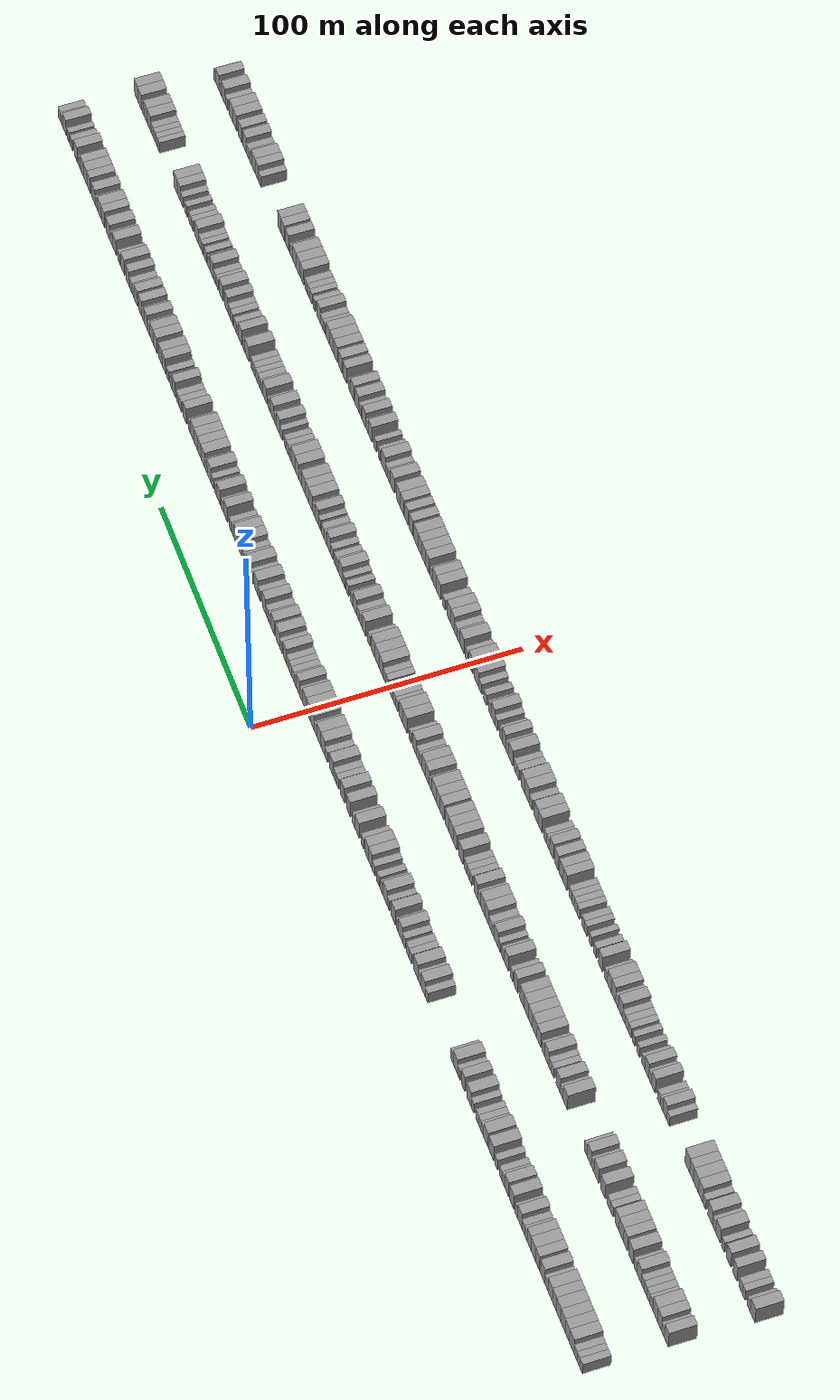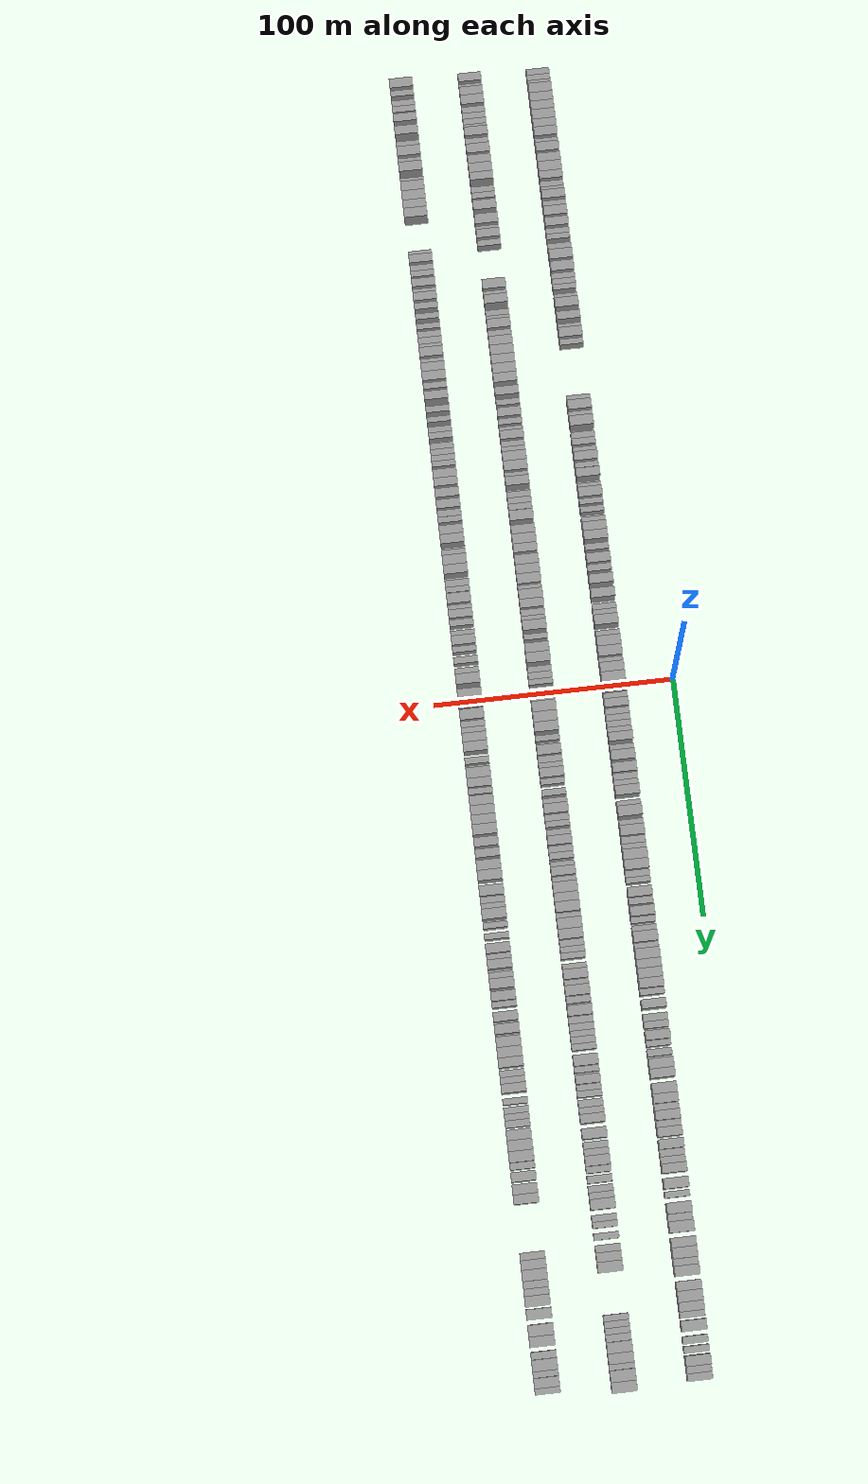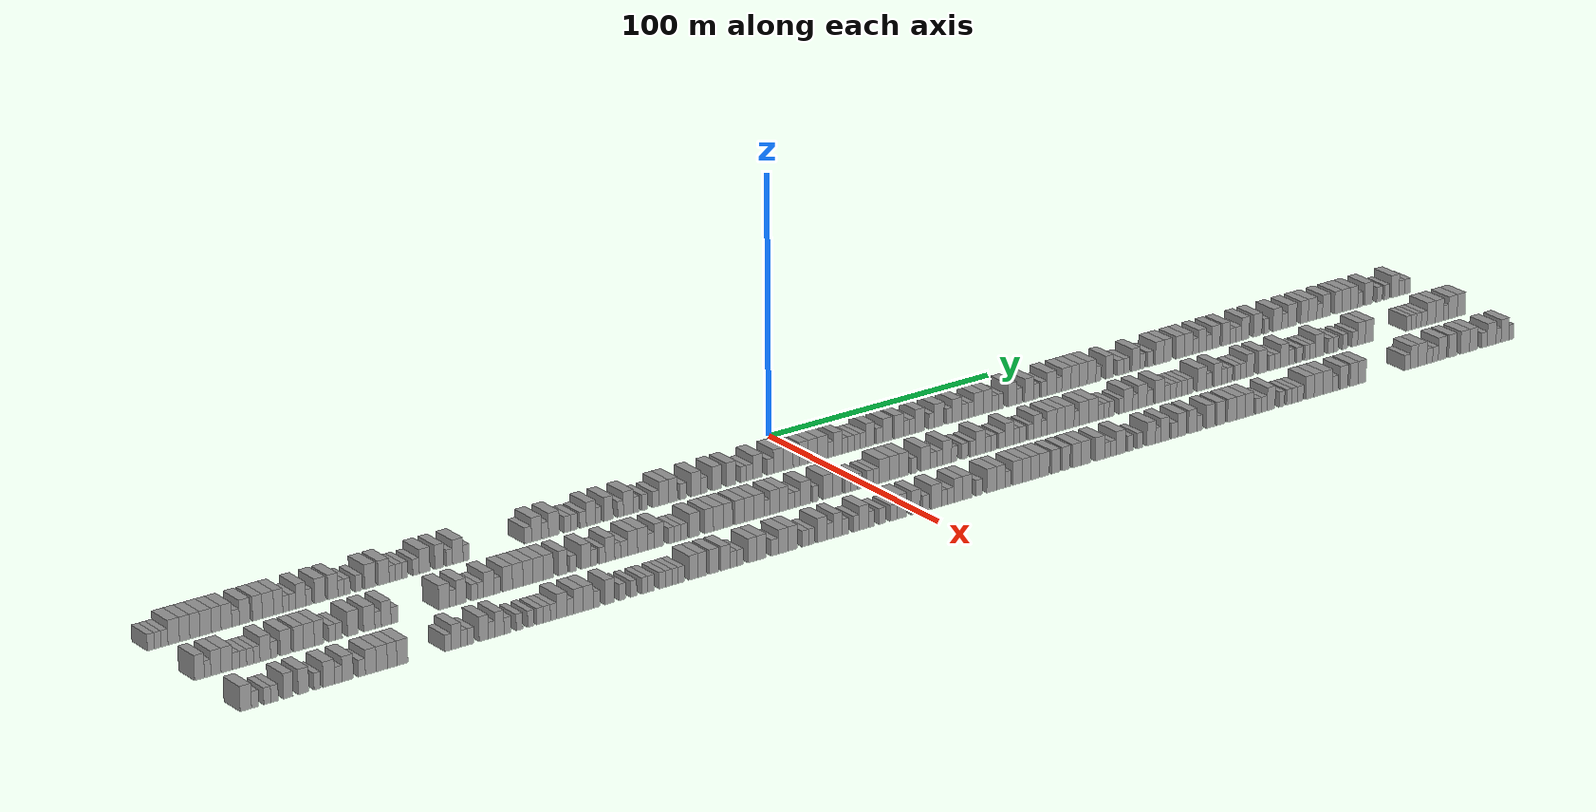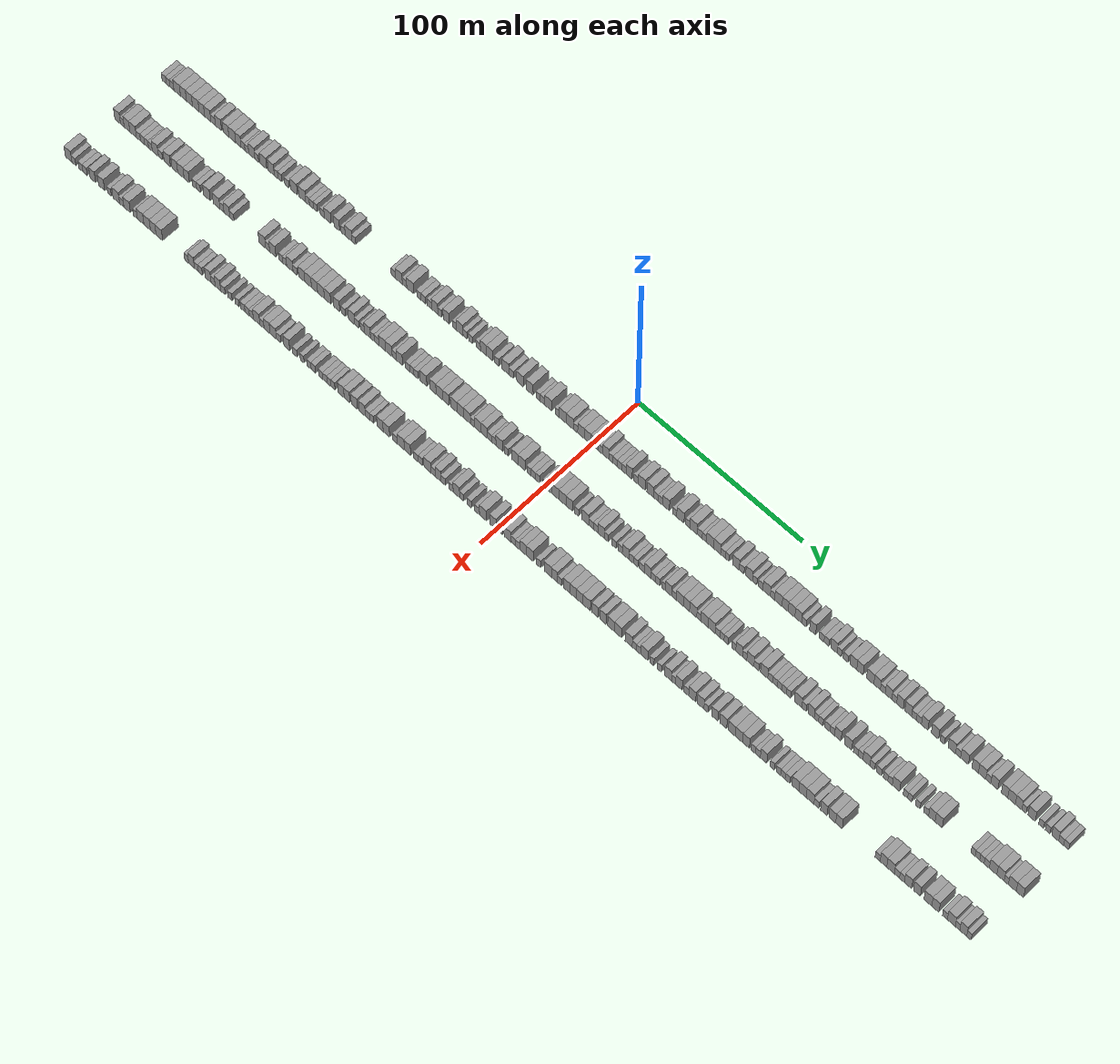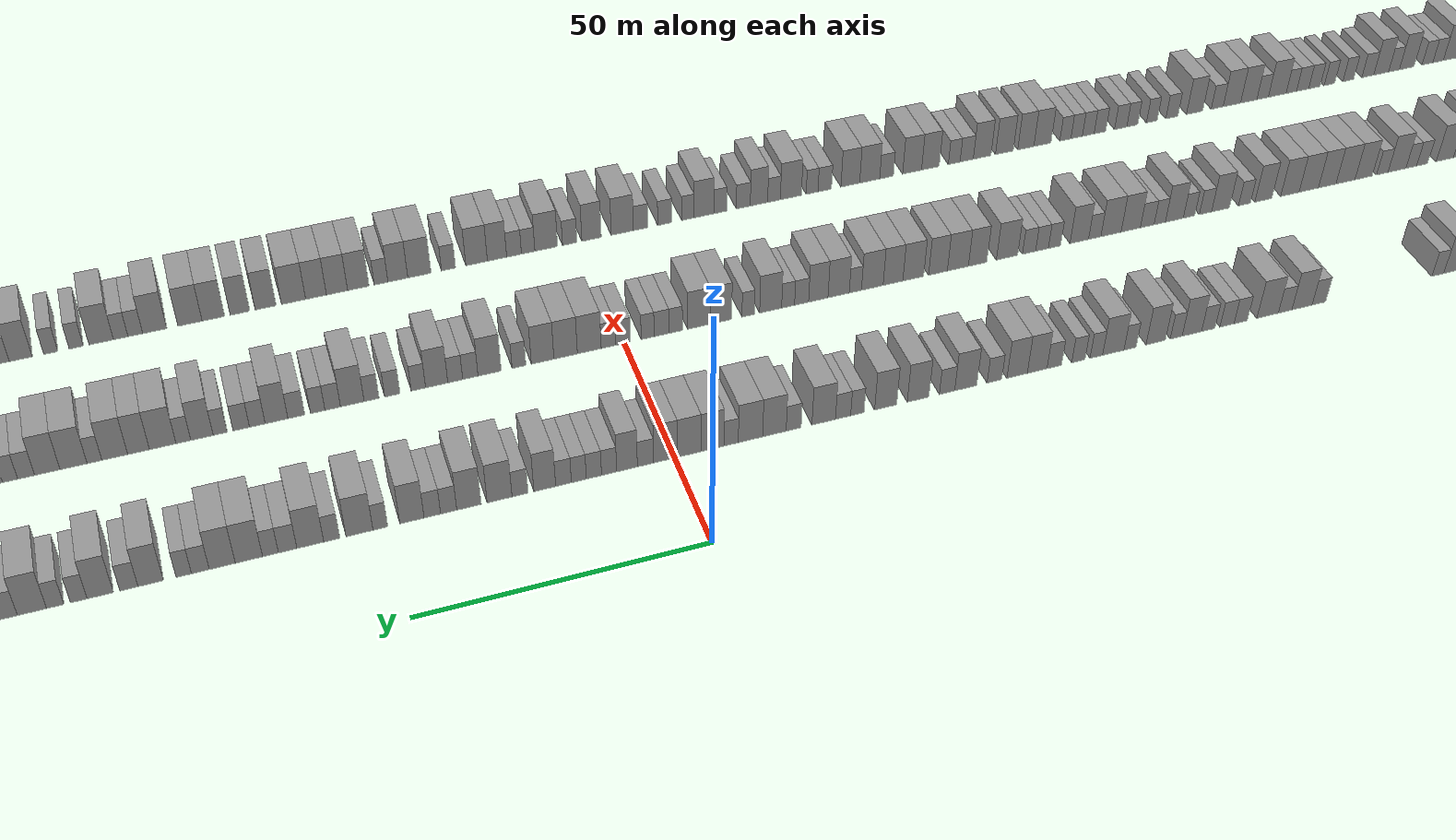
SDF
<sdf version="1.6">
 <world name="default">
  <scene>
   <sky><clouds><speed>12</speed></clouds></sky>
   <ambient>0.4 0.4 0.4 1</ambient>
   <background>0.7 0.7 0.7 1</background>
   <shadows>1</shadows>
  </scene>
  <gravity>0 0 -9.8066</gravity>
  <magnetic_field>6e-06 2.3e-05 -4.2e-05</magnetic_field>
  <physics default="0" name="default_physics" type="ode">
   <ode>
    <solver>
     <type>quick</type>
     <iters>10</iters>
     <sor>1.0</sor>
     <use_dynamic_moi_rescaling>0</use_dynamic_moi_rescaling>
    </solver>
    <constraints>
     <cfm>0</cfm>
     <erp>0.2</erp>
     <contact_max_correcting_vel>100</contact_max_correcting_vel>
     <contact_surface_layer>0.001</contact_surface_layer>
    </constraints>
   </ode>
   <max_step_size>0.004</max_step_size>
   <real_time_factor>1</real_time_factor>
   <real_time_update_rate>250</real_time_update_rate>
  </physics>
  <light name="sun" type="directional">
   <pose>0 0 10 0 0 0</pose>
   <diffuse>0.8 0.8 0.8 1</diffuse>
   <specular>0.2 0.2 0.2 1</specular>
   <attenuation>
    <range>1000</range>
    <constant>0.9</constant>
    <linear>0.01</linear>
    <quadratic>0.001</quadratic>
   </attenuation>
   <direction>-0.5 0.1 -0.9</direction>
  </light>
  <model name="building_1">
   <static>1</static>
   <pose>25.0000 -276.6191 0 0.000000 0.000000 0.000000</pose>
   <link name="link">
    <pose>0 0 3.00 0 0 0</pose>
    <collision name="collision"><geometry><box><size>10.0000 2.7619 6.0000</size></box></geometry></collision>
    <visual name="visual">
     <cast_shadows>0</cast_shadows>
     <geometry><box><size>10.0000 2.7619 6.0000</size></box></geometry>
     <material>
      <script>
       <uri>model://grey_wall/materials/scripts</uri>
       <uri>model://grey_wall/materials/textures</uri>
       <name>vrc/grey_wall</name>
      </script>
     </material>
    </visual>
   </link>
  </model>
  <model name="building_2">
   <static>1</static>
   <pose>25.0000 -273.9857 0 0.000000 0.000000 0.000000</pose>
   <link name="link">
    <pose>0 0 3.00 0 0 0</pose>
    <collision name="collision"><geometry><box><size>10.0000 2.5049 6.0000</size></box></geometry></collision>
    <visual name="visual">
     <cast_shadows>0</cast_shadows>
     <geometry><box><size>10.0000 2.5049 6.0000</size></box></geometry>
     <material>
      <script>
       <uri>model://grey_wall/materials/scripts</uri>
       <uri>model://grey_wall/materials/textures</uri>
       <name>vrc/grey_wall</name>
      </script>
     </material>
    </visual>
   </link>
  </model>
  <model name="building_3">
   <static>1</static>
   <pose>25.0000 -271.3857 0 0.000000 0.000000 0.000000</pose>
   <link name="link">
    <pose>0 0 3.00 0 0 0</pose>
    <collision name="collision"><geometry><box><size>10.0000 2.6950 6.0000</size></box></geometry></collision>
    <visual name="visual">
     <cast_shadows>0</cast_shadows>
     <geometry><box><size>10.0000 2.6950 6.0000</size></box></geometry>
     <material>
      <script>
       <uri>model://grey_wall/materials/scripts</uri>
       <uri>model://grey_wall/materials/textures</uri>
       <name>vrc/grey_wall</name>
      </script>
     </material>
    </visual>
   </link>
  </model>
  <model name="building_4">
   <static>1</static>
   <pose>25.0000 -267.8144 0 0.000000 0.000000 0.000000</pose>
   <link name="link">
    <pose>0 0 4.50 0 0 0</pose>
    <collision name="collision"><geometry><box><size>10.0000 4.4476 9.0000</size></box></geometry></collision>
    <visual name="visual">
     <cast_shadows>0</cast_shadows>
     <geometry><box><size>10.0000 4.4476 9.0000</size></box></geometry>
     <material>
      <script>
       <uri>model://grey_wall/materials/scripts</uri>
       <uri>model://grey_wall/materials/textures</uri>
       <name>vrc/grey_wall</name>
      </script>
     </material>
    </visual>
   </link>
  </model>
  <model name="building_5">
   <static>1</static>
   <pose>25.0000 -263.5804 0 0.000000 0.000000 0.000000</pose>
   <link name="link">
    <pose>0 0 4.50 0 0 0</pose>
    <collision name="collision"><geometry><box><size>10.0000 4.0205 9.0000</size></box></geometry></collision>
    <visual name="visual">
     <cast_shadows>0</cast_shadows>
     <geometry><box><size>10.0000 4.0205 9.0000</size></box></geometry>
     <material>
      <script>
       <uri>model://grey_wall/materials/scripts</uri>
       <uri>model://grey_wall/materials/textures</uri>
       <name>vrc/grey_wall</name>
      </script>
     </material>
    </visual>
   </link>
  </model>
  <model name="building_6">
   <static>1</static>
   <pose>25.0000 -259.5754 0 0.000000 0.000000 0.000000</pose>
   <link name="link">
    <pose>0 0 4.50 0 0 0</pose>
    <collision name="collision"><geometry><box><size>10.0000 3.9895 9.0000</size></box></geometry></collision>
    <visual name="visual">
     <cast_shadows>0</cast_shadows>
     <geometry><box><size>10.0000 3.9895 9.0000</size></box></geometry>
     <material>
      <script>
       <uri>model://grey_wall/materials/scripts</uri>
       <uri>model://grey_wall/materials/textures</uri>
       <name>vrc/grey_wall</name>
      </script>
     </material>
    </visual>
   </link>
  </model>
  <model name="building_7">
   <static>1</static>
   <pose>25.0000 -255.3497 0 0.000000 0.000000 0.000000</pose>
   <link name="link">
    <pose>0 0 4.50 0 0 0</pose>
    <collision name="collision"><geometry><box><size>10.0000 4.4617 9.0000</size></box></geometry></collision>
    <visual name="visual">
     <cast_shadows>0</cast_shadows>
     <geometry><box><size>10.0000 4.4617 9.0000</size></box></geometry>
     <material>
      <script>
       <uri>model://grey_wall/materials/scripts</uri>
       <uri>model://grey_wall/materials/textures</uri>
       <name>vrc/grey_wall</name>
      </script>
     </material>
    </visual>
   </link>
  </model>
  <model name="building_8">
   <static>1</static>
   <pose>25.0000 -251.2563 0 0.000000 0.000000 0.000000</pose>
   <link name="link">
    <pose>0 0 4.50 0 0 0</pose>
    <collision name="collision"><geometry><box><size>10.0000 3.7250 9.0000</size></box></geometry></collision>
    <visual name="visual">
     <cast_shadows>0</cast_shadows>
     <geometry><box><size>10.0000 3.7250 9.0000</size></box></geometry>
     <material>
      <script>
       <uri>model://grey_wall/materials/scripts</uri>
       <uri>model://grey_wall/materials/textures</uri>
       <name>vrc/grey_wall</name>
      </script>
     </material>
    </visual>
   </link>
  </model>
  <model name="building_9">
   <static>1</static>
   <pose>25.0000 -247.2740 0 0.000000 0.000000 0.000000</pose>
   <link name="link">
    <pose>0 0 4.50 0 0 0</pose>
    <collision name="collision"><geometry><box><size>10.0000 4.2396 9.0000</size></box></geometry></collision>
    <visual name="visual">
     <cast_shadows>0</cast_shadows>
     <geometry><box><size>10.0000 4.2396 9.0000</size></box></geometry>
     <material>
      <script>
       <uri>model://grey_wall/materials/scripts</uri>
       <uri>model://grey_wall/materials/textures</uri>
       <name>vrc/grey_wall</name>
      </script>
     </material>
    </visual>
   </link>
  </model>
  <model name="building_10">
   <static>1</static>
   <pose>25.0000 -243.6622 0 0.000000 0.000000 0.000000</pose>
   <link name="link">
    <pose>0 0 3.00 0 0 0</pose>
    <collision name="collision"><geometry><box><size>10.0000 2.9841 6.0000</size></box></geometry></collision>
    <visual name="visual">
     <cast_shadows>0</cast_shadows>
     <geometry><box><size>10.0000 2.9841 6.0000</size></box></geometry>
     <material>
      <script>
       <uri>model://grey_wall/materials/scripts</uri>
       <uri>model://grey_wall/materials/textures</uri>
       <name>vrc/grey_wall</name>
      </script>
     </material>
    </visual>
   </link>
  </model>
  <model name="building_11">
   <static>1</static>
   <pose>25.0000 -240.0857 0 0.000000 0.000000 0.000000</pose>
   <link name="link">
    <pose>0 0 4.50 0 0 0</pose>
    <collision name="collision"><geometry><box><size>10.0000 4.1688 9.0000</size></box></geometry></collision>
    <visual name="visual">
     <cast_shadows>0</cast_shadows>
     <geometry><box><size>10.0000 4.1688 9.0000</size></box></geometry>
     <material>
      <script>
       <uri>model://grey_wall/materials/scripts</uri>
       <uri>model://grey_wall/materials/textures</uri>
       <name>vrc/grey_wall</name>
      </script>
     </material>
    </visual>
   </link>
  </model>
  <model name="building_12">
   <static>1</static>
   <pose>25.0000 -235.0890 0 0.000000 0.000000 0.000000</pose>
   <link name="link">
    <pose>0 0 4.50 0 0 0</pose>
    <collision name="collision"><geometry><box><size>10.0000 3.8247 9.0000</size></box></geometry></collision>
    <visual name="visual">
     <cast_shadows>0</cast_shadows>
     <geometry><box><size>10.0000 3.8247 9.0000</size></box></geometry>
     <material>
      <script>
       <uri>model://grey_wall/materials/scripts</uri>
       <uri>model://grey_wall/materials/textures</uri>
       <name>vrc/grey_wall</name>
      </script>
     </material>
    </visual>
   </link>
  </model>
  <model name="building_13">
   <static>1</static>
   <pose>25.0000 -230.9289 0 0.000000 0.000000 0.000000</pose>
   <link name="link">
    <pose>0 0 4.50 0 0 0</pose>
    <collision name="collision"><geometry><box><size>10.0000 4.4953 9.0000</size></box></geometry></collision>
    <visual name="visual">
     <cast_shadows>0</cast_shadows>
     <geometry><box><size>10.0000 4.4953 9.0000</size></box></geometry>
     <material>
      <script>
       <uri>model://grey_wall/materials/scripts</uri>
       <uri>model://grey_wall/materials/textures</uri>
       <name>vrc/grey_wall</name>
      </script>
     </material>
    </visual>
   </link>
  </model>
  <model name="building_14">
   <static>1</static>
   <pose>25.0000 -226.8792 0 0.000000 0.000000 0.000000</pose>
   <link name="link">
    <pose>0 0 4.50 0 0 0</pose>
    <collision name="collision"><geometry><box><size>10.0000 3.6042 9.0000</size></box></geometry></collision>
    <visual name="visual">
     <cast_shadows>0</cast_shadows>
     <geometry><box><size>10.0000 3.6042 9.0000</size></box></geometry>
     <material>
      <script>
       <uri>model://grey_wall/materials/scripts</uri>
       <uri>model://grey_wall/materials/textures</uri>
       <name>vrc/grey_wall</name>
      </script>
     </material>
    </visual>
   </link>
  </model>
  <model name="building_15">
   <static>1</static>
   <pose>25.0000 -223.8121 0 0.000000 0.000000 0.000000</pose>
   <link name="link">
    <pose>0 0 3.00 0 0 0</pose>
    <collision name="collision"><geometry><box><size>10.0000 2.5299 6.0000</size></box></geometry></collision>
    <visual name="visual">
     <cast_shadows>0</cast_shadows>
     <geometry><box><size>10.0000 2.5299 6.0000</size></box></geometry>
     <material>
      <script>
       <uri>model://grey_wall/materials/scripts</uri>
       <uri>model://grey_wall/materials/textures</uri>
       <name>vrc/grey_wall</name>
      </script>
     </material>
    </visual>
   </link>
  </model>
  <model name="building_16">
   <static>1</static>
   <pose>25.0000 -221.2424 0 0.000000 0.000000 0.000000</pose>
   <link name="link">
    <pose>0 0 3.00 0 0 0</pose>
    <collision name="collision"><geometry><box><size>10.0000 2.6094 6.0000</size></box></geometry></collision>
    <visual name="visual">
     <cast_shadows>0</cast_shadows>
     <geometry><box><size>10.0000 2.6094 6.0000</size></box></geometry>
     <material>
      <script>
       <uri>model://grey_wall/materials/scripts</uri>
       <uri>model://grey_wall/materials/textures</uri>
       <name>vrc/grey_wall</name>
      </script>
     </material>
    </visual>
   </link>
  </model>
  <model name="building_17">
   <static>1</static>
   <pose>25.0000 -217.9524 0 0.000000 0.000000 0.000000</pose>
   <link name="link">
    <pose>0 0 4.50 0 0 0</pose>
    <collision name="collision"><geometry><box><size>10.0000 3.9706 9.0000</size></box></geometry></collision>
    <visual name="visual">
     <cast_shadows>0</cast_shadows>
     <geometry><box><size>10.0000 3.9706 9.0000</size></box></geometry>
     <material>
      <script>
       <uri>model://grey_wall/materials/scripts</uri>
       <uri>model://grey_wall/materials/textures</uri>
       <name>vrc/grey_wall</name>
      </script>
     </material>
    </visual>
   </link>
  </model>
  <model name="building_18">
   <static>1</static>
   <pose>25.0000 -214.6988 0 0.000000 0.000000 0.000000</pose>
   <link name="link">
    <pose>0 0 3.00 0 0 0</pose>
    <collision name="collision"><geometry><box><size>10.0000 2.5365 6.0000</size></box></geometry></collision>
    <visual name="visual">
     <cast_shadows>0</cast_shadows>
     <geometry><box><size>10.0000 2.5365 6.0000</size></box></geometry>
     <material>
      <script>
       <uri>model://grey_wall/materials/scripts</uri>
       <uri>model://grey_wall/materials/textures</uri>
       <name>vrc/grey_wall</name>
      </script>
     </material>
    </visual>
   </link>
  </model>
  <model name="building_19">
   <static>1</static>
   <pose>25.0000 -210.2772 0 0.000000 0.000000 0.000000</pose>
   <link name="link">
    <pose>0 0 4.50 0 0 0</pose>
    <collision name="collision"><geometry><box><size>10.0000 4.3068 9.0000</size></box></geometry></collision>
    <visual name="visual">
     <cast_shadows>0</cast_shadows>
     <geometry><box><size>10.0000 4.3068 9.0000</size></box></geometry>
     <material>
      <script>
       <uri>model://grey_wall/materials/scripts</uri>
       <uri>model://grey_wall/materials/textures</uri>
       <name>vrc/grey_wall</name>
      </script>
     </material>
    </visual>
   </link>
  </model>
  <model name="building_20">
   <static>1</static>
   <pose>25.0000 -205.1337 0 0.000000 0.000000 0.000000</pose>
   <link name="link">
    <pose>0 0 4.50 0 0 0</pose>
    <collision name="collision"><geometry><box><size>10.0000 3.9800 9.0000</size></box></geometry></collision>
    <visual name="visual">
     <cast_shadows>0</cast_shadows>
     <geometry><box><size>10.0000 3.9800 9.0000</size></box></geometry>
     <material>
      <script>
       <uri>model://grey_wall/materials/scripts</uri>
       <uri>model://grey_wall/materials/textures</uri>
       <name>vrc/grey_wall</name>
      </script>
     </material>
    </visual>
   </link>
  </model>
  <model name="building_21">
   <static>1</static>
   <pose>25.0000 -201.8818 0 0.000000 0.000000 0.000000</pose>
   <link name="link">
    <pose>0 0 3.00 0 0 0</pose>
    <collision name="collision"><geometry><box><size>10.0000 2.5238 6.0000</size></box></geometry></collision>
    <visual name="visual">
     <cast_shadows>0</cast_shadows>
     <geometry><box><size>10.0000 2.5238 6.0000</size></box></geometry>
     <material>
      <script>
       <uri>model://grey_wall/materials/scripts</uri>
       <uri>model://grey_wall/materials/textures</uri>
       <name>vrc/grey_wall</name>
      </script>
     </material>
    </visual>
   </link>
  </model>
  <model name="building_22">
   <static>1</static>
   <pose>25.0000 -199.3807 0 0.000000 0.000000 0.000000</pose>
   <link name="link">
    <pose>0 0 3.00 0 0 0</pose>
    <collision name="collision"><geometry><box><size>10.0000 2.4783 6.0000</size></box></geometry></collision>
    <visual name="visual">
     <cast_shadows>0</cast_shadows>
     <geometry><box><size>10.0000 2.4783 6.0000</size></box></geometry>
     <material>
      <script>
       <uri>model://grey_wall/materials/scripts</uri>
       <uri>model://grey_wall/materials/textures</uri>
       <name>vrc/grey_wall</name>
      </script>
     </material>
    </visual>
   </link>
  </model>
  <model name="building_23">
   <static>1</static>
   <pose>25.0000 -194.7735 0 0.000000 0.000000 0.000000</pose>
   <link name="link">
    <pose>0 0 3.00 0 0 0</pose>
    <collision name="collision"><geometry><box><size>10.0000 2.7361 6.0000</size></box></geometry></collision>
    <visual name="visual">
     <cast_shadows>0</cast_shadows>
     <geometry><box><size>10.0000 2.7361 6.0000</size></box></geometry>
     <material>
      <script>
       <uri>model://grey_wall/materials/scripts</uri>
       <uri>model://grey_wall/materials/textures</uri>
       <name>vrc/grey_wall</name>
      </script>
     </material>
    </visual>
   </link>
  </model>
  <model name="building_24">
   <static>1</static>
   <pose>25.0000 -190.1663 0 0.000000 0.000000 0.000000</pose>
   <link name="link">
    <pose>0 0 4.50 0 0 0</pose>
    <collision name="collision"><geometry><box><size>10.0000 4.4783 9.0000</size></box></geometry></collision>
    <visual name="visual">
     <cast_shadows>0</cast_shadows>
     <geometry><box><size>10.0000 4.4783 9.0000</size></box></geometry>
     <material>
      <script>
       <uri>model://grey_wall/materials/scripts</uri>
       <uri>model://grey_wall/materials/textures</uri>
       <name>vrc/grey_wall</name>
      </script>
     </material>
    </visual>
   </link>
  </model>
  <model name="building_25">
   <static>1</static>
   <pose>25.0000 -184.7022 0 0.000000 0.000000 0.000000</pose>
   <link name="link">
    <pose>0 0 4.50 0 0 0</pose>
    <collision name="collision"><geometry><box><size>10.0000 4.4500 9.0000</size></box></geometry></collision>
    <visual name="visual">
     <cast_shadows>0</cast_shadows>
     <geometry><box><size>10.0000 4.4500 9.0000</size></box></geometry>
     <material>
      <script>
       <uri>model://grey_wall/materials/scripts</uri>
       <uri>model://grey_wall/materials/textures</uri>
       <name>vrc/grey_wall</name>
      </script>
     </material>
    </visual>
   </link>
  </model>
  <model name="building_26">
   <static>1</static>
   <pose>25.0000 -181.2104 0 0.000000 0.000000 0.000000</pose>
   <link name="link">
    <pose>0 0 3.00 0 0 0</pose>
    <collision name="collision"><geometry><box><size>10.0000 2.5336 6.0000</size></box></geometry></collision>
    <visual name="visual">
     <cast_shadows>0</cast_shadows>
     <geometry><box><size>10.0000 2.5336 6.0000</size></box></geometry>
     <material>
      <script>
       <uri>model://grey_wall/materials/scripts</uri>
       <uri>model://grey_wall/materials/textures</uri>
       <name>vrc/grey_wall</name>
      </script>
     </material>
    </visual>
   </link>
  </model>
  <model name="building_27">
   <static>1</static>
   <pose>25.0000 -178.6512 0 0.000000 0.000000 0.000000</pose>
   <link name="link">
    <pose>0 0 3.00 0 0 0</pose>
    <collision name="collision"><geometry><box><size>10.0000 2.5849 6.0000</size></box></geometry></collision>
    <visual name="visual">
     <cast_shadows>0</cast_shadows>
     <geometry><box><size>10.0000 2.5849 6.0000</size></box></geometry>
     <material>
      <script>
       <uri>model://grey_wall/materials/scripts</uri>
       <uri>model://grey_wall/materials/textures</uri>
       <name>vrc/grey_wall</name>
      </script>
     </material>
    </visual>
   </link>
  </model>
  <model name="building_28">
   <static>1</static>
   <pose>25.0000 -176.1238 0 0.000000 0.000000 0.000000</pose>
   <link name="link">
    <pose>0 0 3.00 0 0 0</pose>
    <collision name="collision"><geometry><box><size>10.0000 2.4700 6.0000</size></box></geometry></collision>
    <visual name="visual">
     <cast_shadows>0</cast_shadows>
     <geometry><box><size>10.0000 2.4700 6.0000</size></box></geometry>
     <material>
      <script>
       <uri>model://grey_wall/materials/scripts</uri>
       <uri>model://grey_wall/materials/textures</uri>
       <name>vrc/grey_wall</name>
      </script>
     </material>
    </visual>
   </link>
  </model>
  <model name="building_29">
   <static>1</static>
   <pose>25.0000 -171.5630 0 0.000000 0.000000 0.000000</pose>
   <link name="link">
    <pose>0 0 3.00 0 0 0</pose>
    <collision name="collision"><geometry><box><size>10.0000 2.6515 6.0000</size></box></geometry></collision>
    <visual name="visual">
     <cast_shadows>0</cast_shadows>
     <geometry><box><size>10.0000 2.6515 6.0000</size></box></geometry>
     <material>
      <script>
       <uri>model://grey_wall/materials/scripts</uri>
       <uri>model://grey_wall/materials/textures</uri>
       <name>vrc/grey_wall</name>
      </script>
     </material>
    </visual>
   </link>
  </model>
  <model name="building_30">
   <static>1</static>
   <pose>25.0000 -168.0677 0 0.000000 0.000000 0.000000</pose>
   <link name="link">
    <pose>0 0 4.50 0 0 0</pose>
    <collision name="collision"><geometry><box><size>10.0000 4.3392 9.0000</size></box></geometry></collision>
    <visual name="visual">
     <cast_shadows>0</cast_shadows>
     <geometry><box><size>10.0000 4.3392 9.0000</size></box></geometry>
     <material>
      <script>
       <uri>model://grey_wall/materials/scripts</uri>
       <uri>model://grey_wall/materials/textures</uri>
       <name>vrc/grey_wall</name>
      </script>
     </material>
    </visual>
   </link>
  </model>
  <model name="building_31">
   <static>1</static>
   <pose>25.0000 -162.0679 0 0.000000 0.000000 0.000000</pose>
   <link name="link">
    <pose>0 0 4.50 0 0 0</pose>
    <collision name="collision"><geometry><box><size>10.0000 3.6605 9.0000</size></box></geometry></collision>
    <visual name="visual">
     <cast_shadows>0</cast_shadows>
     <geometry><box><size>10.0000 3.6605 9.0000</size></box></geometry>
     <material>
      <script>
       <uri>model://grey_wall/materials/scripts</uri>
       <uri>model://grey_wall/materials/textures</uri>
       <name>vrc/grey_wall</name>
      </script>
     </material>
    </visual>
   </link>
  </model>
  <model name="building_32">
   <static>1</static>
   <pose>25.0000 -157.9386 0 0.000000 0.000000 0.000000</pose>
   <link name="link">
    <pose>0 0 3.00 0 0 0</pose>
    <collision name="collision"><geometry><box><size>10.0000 2.5979 6.0000</size></box></geometry></collision>
    <visual name="visual">
     <cast_shadows>0</cast_shadows>
     <geometry><box><size>10.0000 2.5979 6.0000</size></box></geometry>
     <material>
      <script>
       <uri>model://grey_wall/materials/scripts</uri>
       <uri>model://grey_wall/materials/textures</uri>
       <name>vrc/grey_wall</name>
      </script>
     </material>
    </visual>
   </link>
  </model>
  <model name="building_33">
   <static>1</static>
   <pose>25.0000 -154.4583 0 0.000000 0.000000 0.000000</pose>
   <link name="link">
    <pose>0 0 4.50 0 0 0</pose>
    <collision name="collision"><geometry><box><size>10.0000 4.3626 9.0000</size></box></geometry></collision>
    <visual name="visual">
     <cast_shadows>0</cast_shadows>
     <geometry><box><size>10.0000 4.3626 9.0000</size></box></geometry>
     <material>
      <script>
       <uri>model://grey_wall/materials/scripts</uri>
       <uri>model://grey_wall/materials/textures</uri>
       <name>vrc/grey_wall</name>
      </script>
     </material>
    </visual>
   </link>
  </model>
  <model name="building_34">
   <static>1</static>
   <pose>25.0000 -150.9835 0 0.000000 0.000000 0.000000</pose>
   <link name="link">
    <pose>0 0 3.00 0 0 0</pose>
    <collision name="collision"><geometry><box><size>10.0000 2.5870 6.0000</size></box></geometry></collision>
    <visual name="visual">
     <cast_shadows>0</cast_shadows>
     <geometry><box><size>10.0000 2.5870 6.0000</size></box></geometry>
     <material>
      <script>
       <uri>model://grey_wall/materials/scripts</uri>
       <uri>model://grey_wall/materials/textures</uri>
       <name>vrc/grey_wall</name>
      </script>
     </material>
    </visual>
   </link>
  </model>
  <model name="building_35">
   <static>1</static>
   <pose>25.0000 -125.3575 0 0.000000 0.000000 0.000000</pose>
   <link name="link">
    <pose>0 0 3.00 0 0 0</pose>
    <collision name="collision"><geometry><box><size>10.0000 2.8883 6.0000</size></box></geometry></collision>
    <visual name="visual">
     <cast_shadows>0</cast_shadows>
     <geometry><box><size>10.0000 2.8883 6.0000</size></box></geometry>
     <material>
      <script>
       <uri>model://grey_wall/materials/scripts</uri>
       <uri>model://grey_wall/materials/textures</uri>
       <name>vrc/grey_wall</name>
      </script>
     </material>
    </visual>
   </link>
  </model>
  <model name="building_36">
   <static>1</static>
   <pose>25.0000 -121.7851 0 0.000000 0.000000 0.000000</pose>
   <link name="link">
    <pose>0 0 4.50 0 0 0</pose>
    <collision name="collision"><geometry><box><size>10.0000 4.2564 9.0000</size></box></geometry></collision>
    <visual name="visual">
     <cast_shadows>0</cast_shadows>
     <geometry><box><size>10.0000 4.2564 9.0000</size></box></geometry>
     <material>
      <script>
       <uri>model://grey_wall/materials/scripts</uri>
       <uri>model://grey_wall/materials/textures</uri>
       <name>vrc/grey_wall</name>
      </script>
     </material>
    </visual>
   </link>
  </model>
  <model name="building_37">
   <static>1</static>
   <pose>25.0000 -118.2361 0 0.000000 0.000000 0.000000</pose>
   <link name="link">
    <pose>0 0 3.00 0 0 0</pose>
    <collision name="collision"><geometry><box><size>10.0000 2.8416 6.0000</size></box></geometry></collision>
    <visual name="visual">
     <cast_shadows>0</cast_shadows>
     <geometry><box><size>10.0000 2.8416 6.0000</size></box></geometry>
     <material>
      <script>
       <uri>model://grey_wall/materials/scripts</uri>
       <uri>model://grey_wall/materials/textures</uri>
       <name>vrc/grey_wall</name>
      </script>
     </material>
    </visual>
   </link>
  </model>
  <model name="building_38">
   <static>1</static>
   <pose>25.0000 -114.5731 0 0.000000 0.000000 0.000000</pose>
   <link name="link">
    <pose>0 0 4.50 0 0 0</pose>
    <collision name="collision"><geometry><box><size>10.0000 4.4842 9.0000</size></box></geometry></collision>
    <visual name="visual">
     <cast_shadows>0</cast_shadows>
     <geometry><box><size>10.0000 4.4842 9.0000</size></box></geometry>
     <material>
      <script>
       <uri>model://grey_wall/materials/scripts</uri>
       <uri>model://grey_wall/materials/textures</uri>
       <name>vrc/grey_wall</name>
      </script>
     </material>
    </visual>
   </link>
  </model>
  <model name="building_39">
   <static>1</static>
   <pose>25.0000 -108.9503 0 0.000000 0.000000 0.000000</pose>
   <link name="link">
    <pose>0 0 3.00 0 0 0</pose>
    <collision name="collision"><geometry><box><size>10.0000 2.7614 6.0000</size></box></geometry></collision>
    <visual name="visual">
     <cast_shadows>0</cast_shadows>
     <geometry><box><size>10.0000 2.7614 6.0000</size></box></geometry>
     <material>
      <script>
       <uri>model://grey_wall/materials/scripts</uri>
       <uri>model://grey_wall/materials/textures</uri>
       <name>vrc/grey_wall</name>
      </script>
     </material>
    </visual>
   </link>
  </model>
  <model name="building_40">
   <static>1</static>
   <pose>25.0000 -106.1159 0 0.000000 0.000000 0.000000</pose>
   <link name="link">
    <pose>0 0 3.00 0 0 0</pose>
    <collision name="collision"><geometry><box><size>10.0000 2.9073 6.0000</size></box></geometry></collision>
    <visual name="visual">
     <cast_shadows>0</cast_shadows>
     <geometry><box><size>10.0000 2.9073 6.0000</size></box></geometry>
     <material>
      <script>
       <uri>model://grey_wall/materials/scripts</uri>
       <uri>model://grey_wall/materials/textures</uri>
       <name>vrc/grey_wall</name>
      </script>
     </material>
    </visual>
   </link>
  </model>
  <model name="building_41">
   <static>1</static>
   <pose>25.0000 -102.2691 0 0.000000 0.000000 0.000000</pose>
   <link name="link">
    <pose>0 0 3.00 0 0 0</pose>
    <collision name="collision"><geometry><box><size>10.0000 2.7864 6.0000</size></box></geometry></collision>
    <visual name="visual">
     <cast_shadows>0</cast_shadows>
     <geometry><box><size>10.0000 2.7864 6.0000</size></box></geometry>
     <material>
      <script>
       <uri>model://grey_wall/materials/scripts</uri>
       <uri>model://grey_wall/materials/textures</uri>
       <name>vrc/grey_wall</name>
      </script>
     </material>
    </visual>
   </link>
  </model>
  <model name="building_42">
   <static>1</static>
   <pose>25.0000 -98.8905 0 0.000000 0.000000 0.000000</pose>
   <link name="link">
    <pose>0 0 4.50 0 0 0</pose>
    <collision name="collision"><geometry><box><size>10.0000 3.9708 9.0000</size></box></geometry></collision>
    <visual name="visual">
     <cast_shadows>0</cast_shadows>
     <geometry><box><size>10.0000 3.9708 9.0000</size></box></geometry>
     <material>
      <script>
       <uri>model://grey_wall/materials/scripts</uri>
       <uri>model://grey_wall/materials/textures</uri>
       <name>vrc/grey_wall</name>
      </script>
     </material>
    </visual>
   </link>
  </model>
  <model name="building_43">
   <static>1</static>
   <pose>25.0000 -95.6928 0 0.000000 0.000000 0.000000</pose>
   <link name="link">
    <pose>0 0 3.00 0 0 0</pose>
    <collision name="collision"><geometry><box><size>10.0000 2.4245 6.0000</size></box></geometry></collision>
    <visual name="visual">
     <cast_shadows>0</cast_shadows>
     <geometry><box><size>10.0000 2.4245 6.0000</size></box></geometry>
     <material>
      <script>
       <uri>model://grey_wall/materials/scripts</uri>
       <uri>model://grey_wall/materials/textures</uri>
       <name>vrc/grey_wall</name>
      </script>
     </material>
    </visual>
   </link>
  </model>
  <model name="building_44">
   <static>1</static>
   <pose>25.0000 -91.5200 0 0.000000 0.000000 0.000000</pose>
   <link name="link">
    <pose>0 0 4.50 0 0 0</pose>
    <collision name="collision"><geometry><box><size>10.0000 3.9213 9.0000</size></box></geometry></collision>
    <visual name="visual">
     <cast_shadows>0</cast_shadows>
     <geometry><box><size>10.0000 3.9213 9.0000</size></box></geometry>
     <material>
      <script>
       <uri>model://grey_wall/materials/scripts</uri>
       <uri>model://grey_wall/materials/textures</uri>
       <name>vrc/grey_wall</name>
      </script>
     </material>
    </visual>
   </link>
  </model>
  <model name="building_45">
   <static>1</static>
   <pose>25.0000 -86.3372 0 0.000000 0.000000 0.000000</pose>
   <link name="link">
    <pose>0 0 3.00 0 0 0</pose>
    <collision name="collision"><geometry><box><size>10.0000 2.4442 6.0000</size></box></geometry></collision>
    <visual name="visual">
     <cast_shadows>0</cast_shadows>
     <geometry><box><size>10.0000 2.4442 6.0000</size></box></geometry>
     <material>
      <script>
       <uri>model://grey_wall/materials/scripts</uri>
       <uri>model://grey_wall/materials/textures</uri>
       <name>vrc/grey_wall</name>
      </script>
     </material>
    </visual>
   </link>
  </model>
  <model name="building_46">
   <static>1</static>
   <pose>25.0000 -82.9664 0 0.000000 0.000000 0.000000</pose>
   <link name="link">
    <pose>0 0 4.50 0 0 0</pose>
    <collision name="collision"><geometry><box><size>10.0000 4.2973 9.0000</size></box></geometry></collision>
    <visual name="visual">
     <cast_shadows>0</cast_shadows>
     <geometry><box><size>10.0000 4.2973 9.0000</size></box></geometry>
     <material>
      <script>
       <uri>model://grey_wall/materials/scripts</uri>
       <uri>model://grey_wall/materials/textures</uri>
       <name>vrc/grey_wall</name>
      </script>
     </material>
    </visual>
   </link>
  </model>
  <model name="building_47">
   <static>1</static>
   <pose>25.0000 -79.5691 0 0.000000 0.000000 0.000000</pose>
   <link name="link">
    <pose>0 0 3.00 0 0 0</pose>
    <collision name="collision"><geometry><box><size>10.0000 2.4973 6.0000</size></box></geometry></collision>
    <visual name="visual">
     <cast_shadows>0</cast_shadows>
     <geometry><box><size>10.0000 2.4973 6.0000</size></box></geometry>
     <material>
      <script>
       <uri>model://grey_wall/materials/scripts</uri>
       <uri>model://grey_wall/materials/textures</uri>
       <name>vrc/grey_wall</name>
      </script>
     </material>
    </visual>
   </link>
  </model>
  <model name="building_48">
   <static>1</static>
   <pose>25.0000 -75.9990 0 0.000000 0.000000 0.000000</pose>
   <link name="link">
    <pose>0 0 3.00 0 0 0</pose>
    <collision name="collision"><geometry><box><size>10.0000 2.6429 6.0000</size></box></geometry></collision>
    <visual name="visual">
     <cast_shadows>0</cast_shadows>
     <geometry><box><size>10.0000 2.6429 6.0000</size></box></geometry>
     <material>
      <script>
       <uri>model://grey_wall/materials/scripts</uri>
       <uri>model://grey_wall/materials/textures</uri>
       <name>vrc/grey_wall</name>
      </script>
     </material>
    </visual>
   </link>
  </model>
  <model name="building_49">
   <static>1</static>
   <pose>25.0000 -71.2366 0 0.000000 0.000000 0.000000</pose>
   <link name="link">
    <pose>0 0 3.00 0 0 0</pose>
    <collision name="collision"><geometry><box><size>10.0000 2.8819 6.0000</size></box></geometry></collision>
    <visual name="visual">
     <cast_shadows>0</cast_shadows>
     <geometry><box><size>10.0000 2.8819 6.0000</size></box></geometry>
     <material>
      <script>
       <uri>model://grey_wall/materials/scripts</uri>
       <uri>model://grey_wall/materials/textures</uri>
       <name>vrc/grey_wall</name>
      </script>
     </material>
    </visual>
   </link>
  </model>
  <model name="building_50">
   <static>1</static>
   <pose>25.0000 -67.8626 0 0.000000 0.000000 0.000000</pose>
   <link name="link">
    <pose>0 0 4.50 0 0 0</pose>
    <collision name="collision"><geometry><box><size>10.0000 3.8659 9.0000</size></box></geometry></collision>
    <visual name="visual">
     <cast_shadows>0</cast_shadows>
     <geometry><box><size>10.0000 3.8659 9.0000</size></box></geometry>
     <material>
      <script>
       <uri>model://grey_wall/materials/scripts</uri>
       <uri>model://grey_wall/materials/textures</uri>
       <name>vrc/grey_wall</name>
      </script>
     </material>
    </visual>
   </link>
  </model>
  <model name="building_51">
   <static>1</static>
   <pose>25.0000 -63.9339 0 0.000000 0.000000 0.000000</pose>
   <link name="link">
    <pose>0 0 4.50 0 0 0</pose>
    <collision name="collision"><geometry><box><size>10.0000 3.9915 9.0000</size></box></geometry></collision>
    <visual name="visual">
     <cast_shadows>0</cast_shadows>
     <geometry><box><size>10.0000 3.9915 9.0000</size></box></geometry>
     <material>
      <script>
       <uri>model://grey_wall/materials/scripts</uri>
       <uri>model://grey_wall/materials/textures</uri>
       <name>vrc/grey_wall</name>
      </script>
     </material>
    </visual>
   </link>
  </model>
  <model name="building_52">
   <static>1</static>
   <pose>25.0000 -59.5089 0 0.000000 0.000000 0.000000</pose>
   <link name="link">
    <pose>0 0 3.00 0 0 0</pose>
    <collision name="collision"><geometry><box><size>10.0000 2.8585 6.0000</size></box></geometry></collision>
    <visual name="visual">
     <cast_shadows>0</cast_shadows>
     <geometry><box><size>10.0000 2.8585 6.0000</size></box></geometry>
     <material>
      <script>
       <uri>model://grey_wall/materials/scripts</uri>
       <uri>model://grey_wall/materials/textures</uri>
       <name>vrc/grey_wall</name>
      </script>
     </material>
    </visual>
   </link>
  </model>
  <model name="building_53">
   <static>1</static>
   <pose>25.0000 -53.9598 0 0.000000 0.000000 0.000000</pose>
   <link name="link">
    <pose>0 0 4.50 0 0 0</pose>
    <collision name="collision"><geometry><box><size>10.0000 4.2397 9.0000</size></box></geometry></collision>
    <visual name="visual">
     <cast_shadows>0</cast_shadows>
     <geometry><box><size>10.0000 4.2397 9.0000</size></box></geometry>
     <material>
      <script>
       <uri>model://grey_wall/materials/scripts</uri>
       <uri>model://grey_wall/materials/textures</uri>
       <name>vrc/grey_wall</name>
      </script>
     </material>
    </visual>
   </link>
  </model>
  <model name="building_54">
   <static>1</static>
   <pose>25.0000 -50.3674 0 0.000000 0.000000 0.000000</pose>
   <link name="link">
    <pose>0 0 3.00 0 0 0</pose>
    <collision name="collision"><geometry><box><size>10.0000 2.9451 6.0000</size></box></geometry></collision>
    <visual name="visual">
     <cast_shadows>0</cast_shadows>
     <geometry><box><size>10.0000 2.9451 6.0000</size></box></geometry>
     <material>
      <script>
       <uri>model://grey_wall/materials/scripts</uri>
       <uri>model://grey_wall/materials/textures</uri>
       <name>vrc/grey_wall</name>
      </script>
     </material>
    </visual>
   </link>
  </model>
  <model name="building_55">
   <static>1</static>
   <pose>25.0000 -44.8354 0 0.000000 0.000000 0.000000</pose>
   <link name="link">
    <pose>0 0 4.50 0 0 0</pose>
    <collision name="collision"><geometry><box><size>10.0000 4.1189 9.0000</size></box></geometry></collision>
    <visual name="visual">
     <cast_shadows>0</cast_shadows>
     <geometry><box><size>10.0000 4.1189 9.0000</size></box></geometry>
     <material>
      <script>
       <uri>model://grey_wall/materials/scripts</uri>
       <uri>model://grey_wall/materials/textures</uri>
       <name>vrc/grey_wall</name>
      </script>
     </material>
    </visual>
   </link>
  </model>
  <model name="building_56">
   <static>1</static>
   <pose>25.0000 -38.6920 0 0.000000 0.000000 0.000000</pose>
   <link name="link">
    <pose>0 0 4.50 0 0 0</pose>
    <collision name="collision"><geometry><box><size>10.0000 4.1679 9.0000</size></box></geometry></collision>
    <visual name="visual">
     <cast_shadows>0</cast_shadows>
     <geometry><box><size>10.0000 4.1679 9.0000</size></box></geometry>
     <material>
      <script>
       <uri>model://grey_wall/materials/scripts</uri>
       <uri>model://grey_wall/materials/textures</uri>
       <name>vrc/grey_wall</name>
      </script>
     </material>
    </visual>
   </link>
  </model>
  <model name="building_57">
   <static>1</static>
   <pose>25.0000 -33.3581 0 0.000000 0.000000 0.000000</pose>
   <link name="link">
    <pose>0 0 3.00 0 0 0</pose>
    <collision name="collision"><geometry><box><size>10.0000 2.4999 6.0000</size></box></geometry></collision>
    <visual name="visual">
     <cast_shadows>0</cast_shadows>
     <geometry><box><size>10.0000 2.4999 6.0000</size></box></geometry>
     <material>
      <script>
       <uri>model://grey_wall/materials/scripts</uri>
       <uri>model://grey_wall/materials/textures</uri>
       <name>vrc/grey_wall</name>
      </script>
     </material>
    </visual>
   </link>
  </model>
  <model name="building_58">
   <static>1</static>
   <pose>25.0000 -30.6854 0 0.000000 0.000000 0.000000</pose>
   <link name="link">
    <pose>0 0 3.00 0 0 0</pose>
    <collision name="collision"><geometry><box><size>10.0000 2.8455 6.0000</size></box></geometry></collision>
    <visual name="visual">
     <cast_shadows>0</cast_shadows>
     <geometry><box><size>10.0000 2.8455 6.0000</size></box></geometry>
     <material>
      <script>
       <uri>model://grey_wall/materials/scripts</uri>
       <uri>model://grey_wall/materials/textures</uri>
       <name>vrc/grey_wall</name>
      </script>
     </material>
    </visual>
   </link>
  </model>
  <model name="building_59">
   <static>1</static>
   <pose>25.0000 -27.0819 0 0.000000 0.000000 0.000000</pose>
   <link name="link">
    <pose>0 0 4.50 0 0 0</pose>
    <collision name="collision"><geometry><box><size>10.0000 4.3614 9.0000</size></box></geometry></collision>
    <visual name="visual">
     <cast_shadows>0</cast_shadows>
     <geometry><box><size>10.0000 4.3614 9.0000</size></box></geometry>
     <material>
      <script>
       <uri>model://grey_wall/materials/scripts</uri>
       <uri>model://grey_wall/materials/textures</uri>
       <name>vrc/grey_wall</name>
      </script>
     </material>
    </visual>
   </link>
  </model>
  <model name="building_60">
   <static>1</static>
   <pose>25.0000 -21.5233 0 0.000000 0.000000 0.000000</pose>
   <link name="link">
    <pose>0 0 3.00 0 0 0</pose>
    <collision name="collision"><geometry><box><size>10.0000 2.7559 6.0000</size></box></geometry></collision>
    <visual name="visual">
     <cast_shadows>0</cast_shadows>
     <geometry><box><size>10.0000 2.7559 6.0000</size></box></geometry>
     <material>
      <script>
       <uri>model://grey_wall/materials/scripts</uri>
       <uri>model://grey_wall/materials/textures</uri>
       <name>vrc/grey_wall</name>
      </script>
     </material>
    </visual>
   </link>
  </model>
  <model name="building_61">
   <static>1</static>
   <pose>25.0000 -17.9922 0 0.000000 0.000000 0.000000</pose>
   <link name="link">
    <pose>0 0 4.50 0 0 0</pose>
    <collision name="collision"><geometry><box><size>10.0000 4.3062 9.0000</size></box></geometry></collision>
    <visual name="visual">
     <cast_shadows>0</cast_shadows>
     <geometry><box><size>10.0000 4.3062 9.0000</size></box></geometry>
     <material>
      <script>
       <uri>model://grey_wall/materials/scripts</uri>
       <uri>model://grey_wall/materials/textures</uri>
       <name>vrc/grey_wall</name>
      </script>
     </material>
    </visual>
   </link>
  </model>
  <model name="building_62">
   <static>1</static>
   <pose>25.0000 -13.6157 0 0.000000 0.000000 0.000000</pose>
   <link name="link">
    <pose>0 0 4.50 0 0 0</pose>
    <collision name="collision"><geometry><box><size>10.0000 4.4468 9.0000</size></box></geometry></collision>
    <visual name="visual">
     <cast_shadows>0</cast_shadows>
     <geometry><box><size>10.0000 4.4468 9.0000</size></box></geometry>
     <material>
      <script>
       <uri>model://grey_wall/materials/scripts</uri>
       <uri>model://grey_wall/materials/textures</uri>
       <name>vrc/grey_wall</name>
      </script>
     </material>
    </visual>
   </link>
  </model>
  <model name="building_63">
   <static>1</static>
   <pose>25.0000 -10.1081 0 0.000000 0.000000 0.000000</pose>
   <link name="link">
    <pose>0 0 3.00 0 0 0</pose>
    <collision name="collision"><geometry><box><size>10.0000 2.5683 6.0000</size></box></geometry></collision>
    <visual name="visual">
     <cast_shadows>0</cast_shadows>
     <geometry><box><size>10.0000 2.5683 6.0000</size></box></geometry>
     <material>
      <script>
       <uri>model://grey_wall/materials/scripts</uri>
       <uri>model://grey_wall/materials/textures</uri>
       <name>vrc/grey_wall</name>
      </script>
     </material>
    </visual>
   </link>
  </model>
  <model name="building_64">
   <static>1</static>
   <pose>25.0000 -6.7647 0 0.000000 0.000000 0.000000</pose>
   <link name="link">
    <pose>0 0 4.50 0 0 0</pose>
    <collision name="collision"><geometry><box><size>10.0000 4.1185 9.0000</size></box></geometry></collision>
    <visual name="visual">
     <cast_shadows>0</cast_shadows>
     <geometry><box><size>10.0000 4.1185 9.0000</size></box></geometry>
     <material>
      <script>
       <uri>model://grey_wall/materials/scripts</uri>
       <uri>model://grey_wall/materials/textures</uri>
       <name>vrc/grey_wall</name>
      </script>
     </material>
    </visual>
   </link>
  </model>
  <model name="building_65">
   <static>1</static>
   <pose>25.0000 -2.5718 0 0.000000 0.000000 0.000000</pose>
   <link name="link">
    <pose>0 0 4.50 0 0 0</pose>
    <collision name="collision"><geometry><box><size>10.0000 4.2673 9.0000</size></box></geometry></collision>
    <visual name="visual">
     <cast_shadows>0</cast_shadows>
     <geometry><box><size>10.0000 4.2673 9.0000</size></box></geometry>
     <material>
      <script>
       <uri>model://grey_wall/materials/scripts</uri>
       <uri>model://grey_wall/materials/textures</uri>
       <name>vrc/grey_wall</name>
      </script>
     </material>
    </visual>
   </link>
  </model>
  <model name="building_66">
   <static>1</static>
   <pose>25.0000 1.6884 0 0.000000 0.000000 0.000000</pose>
   <link name="link">
    <pose>0 0 4.50 0 0 0</pose>
    <collision name="collision"><geometry><box><size>10.0000 4.2529 9.0000</size></box></geometry></collision>
    <visual name="visual">
     <cast_shadows>0</cast_shadows>
     <geometry><box><size>10.0000 4.2529 9.0000</size></box></geometry>
     <material>
      <script>
       <uri>model://grey_wall/materials/scripts</uri>
       <uri>model://grey_wall/materials/textures</uri>
       <name>vrc/grey_wall</name>
      </script>
     </material>
    </visual>
   </link>
  </model>
  <model name="building_67">
   <static>1</static>
   <pose>25.0000 5.2637 0 0.000000 0.000000 0.000000</pose>
   <link name="link">
    <pose>0 0 3.00 0 0 0</pose>
    <collision name="collision"><geometry><box><size>10.0000 2.8977 6.0000</size></box></geometry></collision>
    <visual name="visual">
     <cast_shadows>0</cast_shadows>
     <geometry><box><size>10.0000 2.8977 6.0000</size></box></geometry>
     <material>
      <script>
       <uri>model://grey_wall/materials/scripts</uri>
       <uri>model://grey_wall/materials/textures</uri>
       <name>vrc/grey_wall</name>
      </script>
     </material>
    </visual>
   </link>
  </model>
  <model name="building_68">
   <static>1</static>
   <pose>25.0000 8.5379 0 0.000000 0.000000 0.000000</pose>
   <link name="link">
    <pose>0 0 4.50 0 0 0</pose>
    <collision name="collision"><geometry><box><size>10.0000 3.6507 9.0000</size></box></geometry></collision>
    <visual name="visual">
     <cast_shadows>0</cast_shadows>
     <geometry><box><size>10.0000 3.6507 9.0000</size></box></geometry>
     <material>
      <script>
       <uri>model://grey_wall/materials/scripts</uri>
       <uri>model://grey_wall/materials/textures</uri>
       <name>vrc/grey_wall</name>
      </script>
     </material>
    </visual>
   </link>
  </model>
  <model name="building_69">
   <static>1</static>
   <pose>25.0000 11.6974 0 0.000000 0.000000 0.000000</pose>
   <link name="link">
    <pose>0 0 3.00 0 0 0</pose>
    <collision name="collision"><geometry><box><size>10.0000 2.6684 6.0000</size></box></geometry></collision>
    <visual name="visual">
     <cast_shadows>0</cast_shadows>
     <geometry><box><size>10.0000 2.6684 6.0000</size></box></geometry>
     <material>
      <script>
       <uri>model://grey_wall/materials/scripts</uri>
       <uri>model://grey_wall/materials/textures</uri>
       <name>vrc/grey_wall</name>
      </script>
     </material>
    </visual>
   </link>
  </model>
  <model name="building_70">
   <static>1</static>
   <pose>25.0000 14.3689 0 0.000000 0.000000 0.000000</pose>
   <link name="link">
    <pose>0 0 3.00 0 0 0</pose>
    <collision name="collision"><geometry><box><size>10.0000 2.6747 6.0000</size></box></geometry></collision>
    <visual name="visual">
     <cast_shadows>0</cast_shadows>
     <geometry><box><size>10.0000 2.6747 6.0000</size></box></geometry>
     <material>
      <script>
       <uri>model://grey_wall/materials/scripts</uri>
       <uri>model://grey_wall/materials/textures</uri>
       <name>vrc/grey_wall</name>
      </script>
     </material>
    </visual>
   </link>
  </model>
  <model name="building_71">
   <static>1</static>
   <pose>25.0000 17.0073 0 0.000000 0.000000 0.000000</pose>
   <link name="link">
    <pose>0 0 3.00 0 0 0</pose>
    <collision name="collision"><geometry><box><size>10.0000 2.6021 6.0000</size></box></geometry></collision>
    <visual name="visual">
     <cast_shadows>0</cast_shadows>
     <geometry><box><size>10.0000 2.6021 6.0000</size></box></geometry>
     <material>
      <script>
       <uri>model://grey_wall/materials/scripts</uri>
       <uri>model://grey_wall/materials/textures</uri>
       <name>vrc/grey_wall</name>
      </script>
     </material>
    </visual>
   </link>
  </model>
  <model name="building_72">
   <static>1</static>
   <pose>25.0000 19.6736 0 0.000000 0.000000 0.000000</pose>
   <link name="link">
    <pose>0 0 3.00 0 0 0</pose>
    <collision name="collision"><geometry><box><size>10.0000 2.7305 6.0000</size></box></geometry></collision>
    <visual name="visual">
     <cast_shadows>0</cast_shadows>
     <geometry><box><size>10.0000 2.7305 6.0000</size></box></geometry>
     <material>
      <script>
       <uri>model://grey_wall/materials/scripts</uri>
       <uri>model://grey_wall/materials/textures</uri>
       <name>vrc/grey_wall</name>
      </script>
     </material>
    </visual>
   </link>
  </model>
  <model name="building_73">
   <static>1</static>
   <pose>25.0000 22.9234 0 0.000000 0.000000 0.000000</pose>
   <link name="link">
    <pose>0 0 4.50 0 0 0</pose>
    <collision name="collision"><geometry><box><size>10.0000 3.7691 9.0000</size></box></geometry></collision>
    <visual name="visual">
     <cast_shadows>0</cast_shadows>
     <geometry><box><size>10.0000 3.7691 9.0000</size></box></geometry>
     <material>
      <script>
       <uri>model://grey_wall/materials/scripts</uri>
       <uri>model://grey_wall/materials/textures</uri>
       <name>vrc/grey_wall</name>
      </script>
     </material>
    </visual>
   </link>
  </model>
  <model name="building_74">
   <static>1</static>
   <pose>25.0000 27.1916 0 0.000000 0.000000 0.000000</pose>
   <link name="link">
    <pose>0 0 3.00 0 0 0</pose>
    <collision name="collision"><geometry><box><size>10.0000 2.7673 6.0000</size></box></geometry></collision>
    <visual name="visual">
     <cast_shadows>0</cast_shadows>
     <geometry><box><size>10.0000 2.7673 6.0000</size></box></geometry>
     <material>
      <script>
       <uri>model://grey_wall/materials/scripts</uri>
       <uri>model://grey_wall/materials/textures</uri>
       <name>vrc/grey_wall</name>
      </script>
     </material>
    </visual>
   </link>
  </model>
  <model name="building_75">
   <static>1</static>
   <pose>25.0000 30.7077 0 0.000000 0.000000 0.000000</pose>
   <link name="link">
    <pose>0 0 4.50 0 0 0</pose>
    <collision name="collision"><geometry><box><size>10.0000 4.2648 9.0000</size></box></geometry></collision>
    <visual name="visual">
     <cast_shadows>0</cast_shadows>
     <geometry><box><size>10.0000 4.2648 9.0000</size></box></geometry>
     <material>
      <script>
       <uri>model://grey_wall/materials/scripts</uri>
       <uri>model://grey_wall/materials/textures</uri>
       <name>vrc/grey_wall</name>
      </script>
     </material>
    </visual>
   </link>
  </model>
  <model name="building_76">
   <static>1</static>
   <pose>25.0000 35.9200 0 0.000000 0.000000 0.000000</pose>
   <link name="link">
    <pose>0 0 4.50 0 0 0</pose>
    <collision name="collision"><geometry><box><size>10.0000 4.1600 9.0000</size></box></geometry></collision>
    <visual name="visual">
     <cast_shadows>0</cast_shadows>
     <geometry><box><size>10.0000 4.1600 9.0000</size></box></geometry>
     <material>
      <script>
       <uri>model://grey_wall/materials/scripts</uri>
       <uri>model://grey_wall/materials/textures</uri>
       <name>vrc/grey_wall</name>
      </script>
     </material>
    </visual>
   </link>
  </model>
  <model name="building_77">
   <static>1</static>
   <pose>25.0000 39.3635 0 0.000000 0.000000 0.000000</pose>
   <link name="link">
    <pose>0 0 3.00 0 0 0</pose>
    <collision name="collision"><geometry><box><size>10.0000 2.7269 6.0000</size></box></geometry></collision>
    <visual name="visual">
     <cast_shadows>0</cast_shadows>
     <geometry><box><size>10.0000 2.7269 6.0000</size></box></geometry>
     <material>
      <script>
       <uri>model://grey_wall/materials/scripts</uri>
       <uri>model://grey_wall/materials/textures</uri>
       <name>vrc/grey_wall</name>
      </script>
     </material>
    </visual>
   </link>
  </model>
  <model name="building_78">
   <static>1</static>
   <pose>25.0000 42.1148 0 0.000000 0.000000 0.000000</pose>
   <link name="link">
    <pose>0 0 3.00 0 0 0</pose>
    <collision name="collision"><geometry><box><size>10.0000 2.7756 6.0000</size></box></geometry></collision>
    <visual name="visual">
     <cast_shadows>0</cast_shadows>
     <geometry><box><size>10.0000 2.7756 6.0000</size></box></geometry>
     <material>
      <script>
       <uri>model://grey_wall/materials/scripts</uri>
       <uri>model://grey_wall/materials/textures</uri>
       <name>vrc/grey_wall</name>
      </script>
     </material>
    </visual>
   </link>
  </model>
  <model name="building_79">
   <static>1</static>
   <pose>25.0000 45.5423 0 0.000000 0.000000 0.000000</pose>
   <link name="link">
    <pose>0 0 4.50 0 0 0</pose>
    <collision name="collision"><geometry><box><size>10.0000 4.0793 9.0000</size></box></geometry></collision>
    <visual name="visual">
     <cast_shadows>0</cast_shadows>
     <geometry><box><size>10.0000 4.0793 9.0000</size></box></geometry>
     <material>
      <script>
       <uri>model://grey_wall/materials/scripts</uri>
       <uri>model://grey_wall/materials/textures</uri>
       <name>vrc/grey_wall</name>
      </script>
     </material>
    </visual>
   </link>
  </model>
  <model name="building_80">
   <static>1</static>
   <pose>25.0000 50.8127 0 0.000000 0.000000 0.000000</pose>
   <link name="link">
    <pose>0 0 3.00 0 0 0</pose>
    <collision name="collision"><geometry><box><size>10.0000 2.4616 6.0000</size></box></geometry></collision>
    <visual name="visual">
     <cast_shadows>0</cast_shadows>
     <geometry><box><size>10.0000 2.4616 6.0000</size></box></geometry>
     <material>
      <script>
       <uri>model://grey_wall/materials/scripts</uri>
       <uri>model://grey_wall/materials/textures</uri>
       <name>vrc/grey_wall</name>
      </script>
     </material>
    </visual>
   </link>
  </model>
  <model name="building_81">
   <static>1</static>
   <pose>25.0000 54.2745 0 0.000000 0.000000 0.000000</pose>
   <link name="link">
    <pose>0 0 4.50 0 0 0</pose>
    <collision name="collision"><geometry><box><size>10.0000 4.4619 9.0000</size></box></geometry></collision>
    <visual name="visual">
     <cast_shadows>0</cast_shadows>
     <geometry><box><size>10.0000 4.4619 9.0000</size></box></geometry>
     <material>
      <script>
       <uri>model://grey_wall/materials/scripts</uri>
       <uri>model://grey_wall/materials/textures</uri>
       <name>vrc/grey_wall</name>
      </script>
     </material>
    </visual>
   </link>
  </model>
  <model name="building_82">
   <static>1</static>
   <pose>25.0000 58.8342 0 0.000000 0.000000 0.000000</pose>
   <link name="link">
    <pose>0 0 3.00 0 0 0</pose>
    <collision name="collision"><geometry><box><size>10.0000 2.6576 6.0000</size></box></geometry></collision>
    <visual name="visual">
     <cast_shadows>0</cast_shadows>
     <geometry><box><size>10.0000 2.6576 6.0000</size></box></geometry>
     <material>
      <script>
       <uri>model://grey_wall/materials/scripts</uri>
       <uri>model://grey_wall/materials/textures</uri>
       <name>vrc/grey_wall</name>
      </script>
     </material>
    </visual>
   </link>
  </model>
  <model name="building_83">
   <static>1</static>
   <pose>25.0000 62.3588 0 0.000000 0.000000 0.000000</pose>
   <link name="link">
    <pose>0 0 4.50 0 0 0</pose>
    <collision name="collision"><geometry><box><size>10.0000 4.3914 9.0000</size></box></geometry></collision>
    <visual name="visual">
     <cast_shadows>0</cast_shadows>
     <geometry><box><size>10.0000 4.3914 9.0000</size></box></geometry>
     <material>
      <script>
       <uri>model://grey_wall/materials/scripts</uri>
       <uri>model://grey_wall/materials/textures</uri>
       <name>vrc/grey_wall</name>
      </script>
     </material>
    </visual>
   </link>
  </model>
  <model name="building_84">
   <static>1</static>
   <pose>25.0000 66.0514 0 0.000000 0.000000 0.000000</pose>
   <link name="link">
    <pose>0 0 3.00 0 0 0</pose>
    <collision name="collision"><geometry><box><size>10.0000 2.9938 6.0000</size></box></geometry></collision>
    <visual name="visual">
     <cast_shadows>0</cast_shadows>
     <geometry><box><size>10.0000 2.9938 6.0000</size></box></geometry>
     <material>
      <script>
       <uri>model://grey_wall/materials/scripts</uri>
       <uri>model://grey_wall/materials/textures</uri>
       <name>vrc/grey_wall</name>
      </script>
     </material>
    </visual>
   </link>
  </model>
  <model name="building_85">
   <static>1</static>
   <pose>25.0000 68.8356 0 0.000000 0.000000 0.000000</pose>
   <link name="link">
    <pose>0 0 3.00 0 0 0</pose>
    <collision name="collision"><geometry><box><size>10.0000 2.5746 6.0000</size></box></geometry></collision>
    <visual name="visual">
     <cast_shadows>0</cast_shadows>
     <geometry><box><size>10.0000 2.5746 6.0000</size></box></geometry>
     <material>
      <script>
       <uri>model://grey_wall/materials/scripts</uri>
       <uri>model://grey_wall/materials/textures</uri>
       <name>vrc/grey_wall</name>
      </script>
     </material>
    </visual>
   </link>
  </model>
  <model name="building_86">
   <static>1</static>
   <pose>25.0000 72.3199 0 0.000000 0.000000 0.000000</pose>
   <link name="link">
    <pose>0 0 4.50 0 0 0</pose>
    <collision name="collision"><geometry><box><size>10.0000 4.3940 9.0000</size></box></geometry></collision>
    <visual name="visual">
     <cast_shadows>0</cast_shadows>
     <geometry><box><size>10.0000 4.3940 9.0000</size></box></geometry>
     <material>
      <script>
       <uri>model://grey_wall/materials/scripts</uri>
       <uri>model://grey_wall/materials/textures</uri>
       <name>vrc/grey_wall</name>
      </script>
     </material>
    </visual>
   </link>
  </model>
  <model name="building_87">
   <static>1</static>
   <pose>25.0000 76.5973 0 0.000000 0.000000 0.000000</pose>
   <link name="link">
    <pose>0 0 4.50 0 0 0</pose>
    <collision name="collision"><geometry><box><size>10.0000 4.1607 9.0000</size></box></geometry></collision>
    <visual name="visual">
     <cast_shadows>0</cast_shadows>
     <geometry><box><size>10.0000 4.1607 9.0000</size></box></geometry>
     <material>
      <script>
       <uri>model://grey_wall/materials/scripts</uri>
       <uri>model://grey_wall/materials/textures</uri>
       <name>vrc/grey_wall</name>
      </script>
     </material>
    </visual>
   </link>
  </model>
  <model name="building_88">
   <static>1</static>
   <pose>25.0000 80.0898 0 0.000000 0.000000 0.000000</pose>
   <link name="link">
    <pose>0 0 3.00 0 0 0</pose>
    <collision name="collision"><geometry><box><size>10.0000 2.8244 6.0000</size></box></geometry></collision>
    <visual name="visual">
     <cast_shadows>0</cast_shadows>
     <geometry><box><size>10.0000 2.8244 6.0000</size></box></geometry>
     <material>
      <script>
       <uri>model://grey_wall/materials/scripts</uri>
       <uri>model://grey_wall/materials/textures</uri>
       <name>vrc/grey_wall</name>
      </script>
     </material>
    </visual>
   </link>
  </model>
  <model name="building_89">
   <static>1</static>
   <pose>25.0000 82.7230 0 0.000000 0.000000 0.000000</pose>
   <link name="link">
    <pose>0 0 3.00 0 0 0</pose>
    <collision name="collision"><geometry><box><size>10.0000 2.4418 6.0000</size></box></geometry></collision>
    <visual name="visual">
     <cast_shadows>0</cast_shadows>
     <geometry><box><size>10.0000 2.4418 6.0000</size></box></geometry>
     <material>
      <script>
       <uri>model://grey_wall/materials/scripts</uri>
       <uri>model://grey_wall/materials/textures</uri>
       <name>vrc/grey_wall</name>
      </script>
     </material>
    </visual>
   </link>
  </model>
  <model name="building_90">
   <static>1</static>
   <pose>25.0000 87.9460 0 0.000000 0.000000 0.000000</pose>
   <link name="link">
    <pose>0 0 4.50 0 0 0</pose>
    <collision name="collision"><geometry><box><size>10.0000 4.0042 9.0000</size></box></geometry></collision>
    <visual name="visual">
     <cast_shadows>0</cast_shadows>
     <geometry><box><size>10.0000 4.0042 9.0000</size></box></geometry>
     <material>
      <script>
       <uri>model://grey_wall/materials/scripts</uri>
       <uri>model://grey_wall/materials/textures</uri>
       <name>vrc/grey_wall</name>
      </script>
     </material>
    </visual>
   </link>
  </model>
  <model name="building_91">
   <static>1</static>
   <pose>25.0000 91.3719 0 0.000000 0.000000 0.000000</pose>
   <link name="link">
    <pose>0 0 3.00 0 0 0</pose>
    <collision name="collision"><geometry><box><size>10.0000 2.8477 6.0000</size></box></geometry></collision>
    <visual name="visual">
     <cast_shadows>0</cast_shadows>
     <geometry><box><size>10.0000 2.8477 6.0000</size></box></geometry>
     <material>
      <script>
       <uri>model://grey_wall/materials/scripts</uri>
       <uri>model://grey_wall/materials/textures</uri>
       <name>vrc/grey_wall</name>
      </script>
     </material>
    </visual>
   </link>
  </model>
  <model name="building_92">
   <static>1</static>
   <pose>25.0000 95.8423 0 0.000000 0.000000 0.000000</pose>
   <link name="link">
    <pose>0 0 4.50 0 0 0</pose>
    <collision name="collision"><geometry><box><size>10.0000 4.0931 9.0000</size></box></geometry></collision>
    <visual name="visual">
     <cast_shadows>0</cast_shadows>
     <geometry><box><size>10.0000 4.0931 9.0000</size></box></geometry>
     <material>
      <script>
       <uri>model://grey_wall/materials/scripts</uri>
       <uri>model://grey_wall/materials/textures</uri>
       <name>vrc/grey_wall</name>
      </script>
     </material>
    </visual>
   </link>
  </model>
  <model name="building_93">
   <static>1</static>
   <pose>25.0000 99.1836 0 0.000000 0.000000 0.000000</pose>
   <link name="link">
    <pose>0 0 3.00 0 0 0</pose>
    <collision name="collision"><geometry><box><size>10.0000 2.5895 6.0000</size></box></geometry></collision>
    <visual name="visual">
     <cast_shadows>0</cast_shadows>
     <geometry><box><size>10.0000 2.5895 6.0000</size></box></geometry>
     <material>
      <script>
       <uri>model://grey_wall/materials/scripts</uri>
       <uri>model://grey_wall/materials/textures</uri>
       <name>vrc/grey_wall</name>
      </script>
     </material>
    </visual>
   </link>
  </model>
  <model name="building_94">
   <static>1</static>
   <pose>25.0000 102.8076 0 0.000000 0.000000 0.000000</pose>
   <link name="link">
    <pose>0 0 3.00 0 0 0</pose>
    <collision name="collision"><geometry><box><size>10.0000 2.6584 6.0000</size></box></geometry></collision>
    <visual name="visual">
     <cast_shadows>0</cast_shadows>
     <geometry><box><size>10.0000 2.6584 6.0000</size></box></geometry>
     <material>
      <script>
       <uri>model://grey_wall/materials/scripts</uri>
       <uri>model://grey_wall/materials/textures</uri>
       <name>vrc/grey_wall</name>
      </script>
     </material>
    </visual>
   </link>
  </model>
  <model name="building_95">
   <static>1</static>
   <pose>25.0000 106.3598 0 0.000000 0.000000 0.000000</pose>
   <link name="link">
    <pose>0 0 4.50 0 0 0</pose>
    <collision name="collision"><geometry><box><size>10.0000 4.4459 9.0000</size></box></geometry></collision>
    <visual name="visual">
     <cast_shadows>0</cast_shadows>
     <geometry><box><size>10.0000 4.4459 9.0000</size></box></geometry>
     <material>
      <script>
       <uri>model://grey_wall/materials/scripts</uri>
       <uri>model://grey_wall/materials/textures</uri>
       <name>vrc/grey_wall</name>
      </script>
     </material>
    </visual>
   </link>
  </model>
  <model name="building_96">
   <static>1</static>
   <pose>25.0000 109.8705 0 0.000000 0.000000 0.000000</pose>
   <link name="link">
    <pose>0 0 3.00 0 0 0</pose>
    <collision name="collision"><geometry><box><size>10.0000 2.5754 6.0000</size></box></geometry></collision>
    <visual name="visual">
     <cast_shadows>0</cast_shadows>
     <geometry><box><size>10.0000 2.5754 6.0000</size></box></geometry>
     <material>
      <script>
       <uri>model://grey_wall/materials/scripts</uri>
       <uri>model://grey_wall/materials/textures</uri>
       <name>vrc/grey_wall</name>
      </script>
     </material>
    </visual>
   </link>
  </model>
  <model name="building_97">
   <static>1</static>
   <pose>25.0000 113.3537 0 0.000000 0.000000 0.000000</pose>
   <link name="link">
    <pose>0 0 4.50 0 0 0</pose>
    <collision name="collision"><geometry><box><size>10.0000 4.3910 9.0000</size></box></geometry></collision>
    <visual name="visual">
     <cast_shadows>0</cast_shadows>
     <geometry><box><size>10.0000 4.3910 9.0000</size></box></geometry>
     <material>
      <script>
       <uri>model://grey_wall/materials/scripts</uri>
       <uri>model://grey_wall/materials/textures</uri>
       <name>vrc/grey_wall</name>
      </script>
     </material>
    </visual>
   </link>
  </model>
  <model name="building_98">
   <static>1</static>
   <pose>25.0000 117.3864 0 0.000000 0.000000 0.000000</pose>
   <link name="link">
    <pose>0 0 4.50 0 0 0</pose>
    <collision name="collision"><geometry><box><size>10.0000 3.6744 9.0000</size></box></geometry></collision>
    <visual name="visual">
     <cast_shadows>0</cast_shadows>
     <geometry><box><size>10.0000 3.6744 9.0000</size></box></geometry>
     <material>
      <script>
       <uri>model://grey_wall/materials/scripts</uri>
       <uri>model://grey_wall/materials/textures</uri>
       <name>vrc/grey_wall</name>
      </script>
     </material>
    </visual>
   </link>
  </model>
  <model name="building_99">
   <static>1</static>
   <pose>25.0000 121.2319 0 0.000000 0.000000 0.000000</pose>
   <link name="link">
    <pose>0 0 4.50 0 0 0</pose>
    <collision name="collision"><geometry><box><size>10.0000 4.0166 9.0000</size></box></geometry></collision>
    <visual name="visual">
     <cast_shadows>0</cast_shadows>
     <geometry><box><size>10.0000 4.0166 9.0000</size></box></geometry>
     <material>
      <script>
       <uri>model://grey_wall/materials/scripts</uri>
       <uri>model://grey_wall/materials/textures</uri>
       <name>vrc/grey_wall</name>
      </script>
     </material>
    </visual>
   </link>
  </model>
  <model name="building_100">
   <static>1</static>
   <pose>25.0000 125.2518 0 0.000000 0.000000 0.000000</pose>
   <link name="link">
    <pose>0 0 4.50 0 0 0</pose>
    <collision name="collision"><geometry><box><size>10.0000 4.0231 9.0000</size></box></geometry></collision>
    <visual name="visual">
     <cast_shadows>0</cast_shadows>
     <geometry><box><size>10.0000 4.0231 9.0000</size></box></geometry>
     <material>
      <script>
       <uri>model://grey_wall/materials/scripts</uri>
       <uri>model://grey_wall/materials/textures</uri>
       <name>vrc/grey_wall</name>
      </script>
     </material>
    </visual>
   </link>
  </model>
  <model name="building_101">
   <static>1</static>
   <pose>25.0000 128.5922 0 0.000000 0.000000 0.000000</pose>
   <link name="link">
    <pose>0 0 3.00 0 0 0</pose>
    <collision name="collision"><geometry><box><size>10.0000 2.6576 6.0000</size></box></geometry></collision>
    <visual name="visual">
     <cast_shadows>0</cast_shadows>
     <geometry><box><size>10.0000 2.6576 6.0000</size></box></geometry>
     <material>
      <script>
       <uri>model://grey_wall/materials/scripts</uri>
       <uri>model://grey_wall/materials/textures</uri>
       <name>vrc/grey_wall</name>
      </script>
     </material>
    </visual>
   </link>
  </model>
  <model name="building_102">
   <static>1</static>
   <pose>25.0000 133.7462 0 0.000000 0.000000 0.000000</pose>
   <link name="link">
    <pose>0 0 4.50 0 0 0</pose>
    <collision name="collision"><geometry><box><size>10.0000 3.6505 9.0000</size></box></geometry></collision>
    <visual name="visual">
     <cast_shadows>0</cast_shadows>
     <geometry><box><size>10.0000 3.6505 9.0000</size></box></geometry>
     <material>
      <script>
       <uri>model://grey_wall/materials/scripts</uri>
       <uri>model://grey_wall/materials/textures</uri>
       <name>vrc/grey_wall</name>
      </script>
     </material>
    </visual>
   </link>
  </model>
  <model name="building_103">
   <static>1</static>
   <pose>25.0000 139.0585 0 0.000000 0.000000 0.000000</pose>
   <link name="link">
    <pose>0 0 3.00 0 0 0</pose>
    <collision name="collision"><geometry><box><size>10.0000 2.9740 6.0000</size></box></geometry></collision>
    <visual name="visual">
     <cast_shadows>0</cast_shadows>
     <geometry><box><size>10.0000 2.9740 6.0000</size></box></geometry>
     <material>
      <script>
       <uri>model://grey_wall/materials/scripts</uri>
       <uri>model://grey_wall/materials/textures</uri>
       <name>vrc/grey_wall</name>
      </script>
     </material>
    </visual>
   </link>
  </model>
  <model name="building_104">
   <static>1</static>
   <pose>25.0000 141.9959 0 0.000000 0.000000 0.000000</pose>
   <link name="link">
    <pose>0 0 3.00 0 0 0</pose>
    <collision name="collision"><geometry><box><size>10.0000 2.9008 6.0000</size></box></geometry></collision>
    <visual name="visual">
     <cast_shadows>0</cast_shadows>
     <geometry><box><size>10.0000 2.9008 6.0000</size></box></geometry>
     <material>
      <script>
       <uri>model://grey_wall/materials/scripts</uri>
       <uri>model://grey_wall/materials/textures</uri>
       <name>vrc/grey_wall</name>
      </script>
     </material>
    </visual>
   </link>
  </model>
  <model name="building_105">
   <static>1</static>
   <pose>25.0000 146.3792 0 0.000000 0.000000 0.000000</pose>
   <link name="link">
    <pose>0 0 4.50 0 0 0</pose>
    <collision name="collision"><geometry><box><size>10.0000 3.8657 9.0000</size></box></geometry></collision>
    <visual name="visual">
     <cast_shadows>0</cast_shadows>
     <geometry><box><size>10.0000 3.8657 9.0000</size></box></geometry>
     <material>
      <script>
       <uri>model://grey_wall/materials/scripts</uri>
       <uri>model://grey_wall/materials/textures</uri>
       <name>vrc/grey_wall</name>
      </script>
     </material>
    </visual>
   </link>
  </model>
  <model name="building_106">
   <static>1</static>
   <pose>25.0000 149.5567 0 0.000000 0.000000 0.000000</pose>
   <link name="link">
    <pose>0 0 3.00 0 0 0</pose>
    <collision name="collision"><geometry><box><size>10.0000 2.4893 6.0000</size></box></geometry></collision>
    <visual name="visual">
     <cast_shadows>0</cast_shadows>
     <geometry><box><size>10.0000 2.4893 6.0000</size></box></geometry>
     <material>
      <script>
       <uri>model://grey_wall/materials/scripts</uri>
       <uri>model://grey_wall/materials/textures</uri>
       <name>vrc/grey_wall</name>
      </script>
     </material>
    </visual>
   </link>
  </model>
  <model name="building_107">
   <static>1</static>
   <pose>25.0000 153.2718 0 0.000000 0.000000 0.000000</pose>
   <link name="link">
    <pose>0 0 3.00 0 0 0</pose>
    <collision name="collision"><geometry><box><size>10.0000 2.9410 6.0000</size></box></geometry></collision>
    <visual name="visual">
     <cast_shadows>0</cast_shadows>
     <geometry><box><size>10.0000 2.9410 6.0000</size></box></geometry>
     <material>
      <script>
       <uri>model://grey_wall/materials/scripts</uri>
       <uri>model://grey_wall/materials/textures</uri>
       <name>vrc/grey_wall</name>
      </script>
     </material>
    </visual>
   </link>
  </model>
  <model name="building_108">
   <static>1</static>
   <pose>25.0000 157.7884 0 0.000000 0.000000 0.000000</pose>
   <link name="link">
    <pose>0 0 4.50 0 0 0</pose>
    <collision name="collision"><geometry><box><size>10.0000 4.0922 9.0000</size></box></geometry></collision>
    <visual name="visual">
     <cast_shadows>0</cast_shadows>
     <geometry><box><size>10.0000 4.0922 9.0000</size></box></geometry>
     <material>
      <script>
       <uri>model://grey_wall/materials/scripts</uri>
       <uri>model://grey_wall/materials/textures</uri>
       <name>vrc/grey_wall</name>
      </script>
     </material>
    </visual>
   </link>
  </model>
  <model name="building_109">
   <static>1</static>
   <pose>25.0000 161.7265 0 0.000000 0.000000 0.000000</pose>
   <link name="link">
    <pose>0 0 4.50 0 0 0</pose>
    <collision name="collision"><geometry><box><size>10.0000 3.7840 9.0000</size></box></geometry></collision>
    <visual name="visual">
     <cast_shadows>0</cast_shadows>
     <geometry><box><size>10.0000 3.7840 9.0000</size></box></geometry>
     <material>
      <script>
       <uri>model://grey_wall/materials/scripts</uri>
       <uri>model://grey_wall/materials/textures</uri>
       <name>vrc/grey_wall</name>
      </script>
     </material>
    </visual>
   </link>
  </model>
  <model name="building_110">
   <static>1</static>
   <pose>25.0000 167.7330 0 0.000000 0.000000 0.000000</pose>
   <link name="link">
    <pose>0 0 4.50 0 0 0</pose>
    <collision name="collision"><geometry><box><size>10.0000 4.2289 9.0000</size></box></geometry></collision>
    <visual name="visual">
     <cast_shadows>0</cast_shadows>
     <geometry><box><size>10.0000 4.2289 9.0000</size></box></geometry>
     <material>
      <script>
       <uri>model://grey_wall/materials/scripts</uri>
       <uri>model://grey_wall/materials/textures</uri>
       <name>vrc/grey_wall</name>
      </script>
     </material>
    </visual>
   </link>
  </model>
  <model name="building_111">
   <static>1</static>
   <pose>25.0000 171.7868 0 0.000000 0.000000 0.000000</pose>
   <link name="link">
    <pose>0 0 4.50 0 0 0</pose>
    <collision name="collision"><geometry><box><size>10.0000 3.8789 9.0000</size></box></geometry></collision>
    <visual name="visual">
     <cast_shadows>0</cast_shadows>
     <geometry><box><size>10.0000 3.8789 9.0000</size></box></geometry>
     <material>
      <script>
       <uri>model://grey_wall/materials/scripts</uri>
       <uri>model://grey_wall/materials/textures</uri>
       <name>vrc/grey_wall</name>
      </script>
     </material>
    </visual>
   </link>
  </model>
  <model name="building_112">
   <static>1</static>
   <pose>25.0000 175.1234 0 0.000000 0.000000 0.000000</pose>
   <link name="link">
    <pose>0 0 3.00 0 0 0</pose>
    <collision name="collision"><geometry><box><size>10.0000 2.7942 6.0000</size></box></geometry></collision>
    <visual name="visual">
     <cast_shadows>0</cast_shadows>
     <geometry><box><size>10.0000 2.7942 6.0000</size></box></geometry>
     <material>
      <script>
       <uri>model://grey_wall/materials/scripts</uri>
       <uri>model://grey_wall/materials/textures</uri>
       <name>vrc/grey_wall</name>
      </script>
     </material>
    </visual>
   </link>
  </model>
  <model name="building_113">
   <static>1</static>
   <pose>25.0000 178.4568 0 0.000000 0.000000 0.000000</pose>
   <link name="link">
    <pose>0 0 4.50 0 0 0</pose>
    <collision name="collision"><geometry><box><size>10.0000 3.8726 9.0000</size></box></geometry></collision>
    <visual name="visual">
     <cast_shadows>0</cast_shadows>
     <geometry><box><size>10.0000 3.8726 9.0000</size></box></geometry>
     <material>
      <script>
       <uri>model://grey_wall/materials/scripts</uri>
       <uri>model://grey_wall/materials/textures</uri>
       <name>vrc/grey_wall</name>
      </script>
     </material>
    </visual>
   </link>
  </model>
  <model name="building_114">
   <static>1</static>
   <pose>25.0000 181.7851 0 0.000000 0.000000 0.000000</pose>
   <link name="link">
    <pose>0 0 3.00 0 0 0</pose>
    <collision name="collision"><geometry><box><size>10.0000 2.7840 6.0000</size></box></geometry></collision>
    <visual name="visual">
     <cast_shadows>0</cast_shadows>
     <geometry><box><size>10.0000 2.7840 6.0000</size></box></geometry>
     <material>
      <script>
       <uri>model://grey_wall/materials/scripts</uri>
       <uri>model://grey_wall/materials/textures</uri>
       <name>vrc/grey_wall</name>
      </script>
     </material>
    </visual>
   </link>
  </model>
  <model name="building_115">
   <static>1</static>
   <pose>25.0000 185.1047 0 0.000000 0.000000 0.000000</pose>
   <link name="link">
    <pose>0 0 4.50 0 0 0</pose>
    <collision name="collision"><geometry><box><size>10.0000 3.8552 9.0000</size></box></geometry></collision>
    <visual name="visual">
     <cast_shadows>0</cast_shadows>
     <geometry><box><size>10.0000 3.8552 9.0000</size></box></geometry>
     <material>
      <script>
       <uri>model://grey_wall/materials/scripts</uri>
       <uri>model://grey_wall/materials/textures</uri>
       <name>vrc/grey_wall</name>
      </script>
     </material>
    </visual>
   </link>
  </model>
  <model name="building_116">
   <static>1</static>
   <pose>25.0000 189.9615 0 0.000000 0.000000 0.000000</pose>
   <link name="link">
    <pose>0 0 4.50 0 0 0</pose>
    <collision name="collision"><geometry><box><size>10.0000 3.8583 9.0000</size></box></geometry></collision>
    <visual name="visual">
     <cast_shadows>0</cast_shadows>
     <geometry><box><size>10.0000 3.8583 9.0000</size></box></geometry>
     <material>
      <script>
       <uri>model://grey_wall/materials/scripts</uri>
       <uri>model://grey_wall/materials/textures</uri>
       <name>vrc/grey_wall</name>
      </script>
     </material>
    </visual>
   </link>
  </model>
  <model name="building_117">
   <static>1</static>
   <pose>25.0000 193.3164 0 0.000000 0.000000 0.000000</pose>
   <link name="link">
    <pose>0 0 3.00 0 0 0</pose>
    <collision name="collision"><geometry><box><size>10.0000 2.8515 6.0000</size></box></geometry></collision>
    <visual name="visual">
     <cast_shadows>0</cast_shadows>
     <geometry><box><size>10.0000 2.8515 6.0000</size></box></geometry>
     <material>
      <script>
       <uri>model://grey_wall/materials/scripts</uri>
       <uri>model://grey_wall/materials/textures</uri>
       <name>vrc/grey_wall</name>
      </script>
     </material>
    </visual>
   </link>
  </model>
  <model name="building_118">
   <static>1</static>
   <pose>25.0000 196.1739 0 0.000000 0.000000 0.000000</pose>
   <link name="link">
    <pose>0 0 3.00 0 0 0</pose>
    <collision name="collision"><geometry><box><size>10.0000 2.8635 6.0000</size></box></geometry></collision>
    <visual name="visual">
     <cast_shadows>0</cast_shadows>
     <geometry><box><size>10.0000 2.8635 6.0000</size></box></geometry>
     <material>
      <script>
       <uri>model://grey_wall/materials/scripts</uri>
       <uri>model://grey_wall/materials/textures</uri>
       <name>vrc/grey_wall</name>
      </script>
     </material>
    </visual>
   </link>
  </model>
  <model name="building_119">
   <static>1</static>
   <pose>25.0000 199.4936 0 0.000000 0.000000 0.000000</pose>
   <link name="link">
    <pose>0 0 4.50 0 0 0</pose>
    <collision name="collision"><geometry><box><size>10.0000 3.7759 9.0000</size></box></geometry></collision>
    <visual name="visual">
     <cast_shadows>0</cast_shadows>
     <geometry><box><size>10.0000 3.7759 9.0000</size></box></geometry>
     <material>
      <script>
       <uri>model://grey_wall/materials/scripts</uri>
       <uri>model://grey_wall/materials/textures</uri>
       <name>vrc/grey_wall</name>
      </script>
     </material>
    </visual>
   </link>
  </model>
  <model name="building_120">
   <static>1</static>
   <pose>25.0000 205.4732 0 0.000000 0.000000 0.000000</pose>
   <link name="link">
    <pose>0 0 4.50 0 0 0</pose>
    <collision name="collision"><geometry><box><size>10.0000 4.1834 9.0000</size></box></geometry></collision>
    <visual name="visual">
     <cast_shadows>0</cast_shadows>
     <geometry><box><size>10.0000 4.1834 9.0000</size></box></geometry>
     <material>
      <script>
       <uri>model://grey_wall/materials/scripts</uri>
       <uri>model://grey_wall/materials/textures</uri>
       <name>vrc/grey_wall</name>
      </script>
     </material>
    </visual>
   </link>
  </model>
  <model name="building_121">
   <static>1</static>
   <pose>25.0000 209.8141 0 0.000000 0.000000 0.000000</pose>
   <link name="link">
    <pose>0 0 3.00 0 0 0</pose>
    <collision name="collision"><geometry><box><size>10.0000 2.4983 6.0000</size></box></geometry></collision>
    <visual name="visual">
     <cast_shadows>0</cast_shadows>
     <geometry><box><size>10.0000 2.4983 6.0000</size></box></geometry>
     <material>
      <script>
       <uri>model://grey_wall/materials/scripts</uri>
       <uri>model://grey_wall/materials/textures</uri>
       <name>vrc/grey_wall</name>
      </script>
     </material>
    </visual>
   </link>
  </model>
  <model name="building_122">
   <static>1</static>
   <pose>25.0000 215.2289 0 0.000000 0.000000 0.000000</pose>
   <link name="link">
    <pose>0 0 4.50 0 0 0</pose>
    <collision name="collision"><geometry><box><size>10.0000 4.3314 9.0000</size></box></geometry></collision>
    <visual name="visual">
     <cast_shadows>0</cast_shadows>
     <geometry><box><size>10.0000 4.3314 9.0000</size></box></geometry>
     <material>
      <script>
       <uri>model://grey_wall/materials/scripts</uri>
       <uri>model://grey_wall/materials/textures</uri>
       <name>vrc/grey_wall</name>
      </script>
     </material>
    </visual>
   </link>
  </model>
  <model name="building_123">
   <static>1</static>
   <pose>25.0000 218.8614 0 0.000000 0.000000 0.000000</pose>
   <link name="link">
    <pose>0 0 3.00 0 0 0</pose>
    <collision name="collision"><geometry><box><size>10.0000 2.9336 6.0000</size></box></geometry></collision>
    <visual name="visual">
     <cast_shadows>0</cast_shadows>
     <geometry><box><size>10.0000 2.9336 6.0000</size></box></geometry>
     <material>
      <script>
       <uri>model://grey_wall/materials/scripts</uri>
       <uri>model://grey_wall/materials/textures</uri>
       <name>vrc/grey_wall</name>
      </script>
     </material>
    </visual>
   </link>
  </model>
  <model name="building_124">
   <static>1</static>
   <pose>25.0000 222.5614 0 0.000000 0.000000 0.000000</pose>
   <link name="link">
    <pose>0 0 4.50 0 0 0</pose>
    <collision name="collision"><geometry><box><size>10.0000 4.4664 9.0000</size></box></geometry></collision>
    <visual name="visual">
     <cast_shadows>0</cast_shadows>
     <geometry><box><size>10.0000 4.4664 9.0000</size></box></geometry>
     <material>
      <script>
       <uri>model://grey_wall/materials/scripts</uri>
       <uri>model://grey_wall/materials/textures</uri>
       <name>vrc/grey_wall</name>
      </script>
     </material>
    </visual>
   </link>
  </model>
  <model name="building_125">
   <static>1</static>
   <pose>25.0000 228.6683 0 0.000000 0.000000 0.000000</pose>
   <link name="link">
    <pose>0 0 4.50 0 0 0</pose>
    <collision name="collision"><geometry><box><size>10.0000 3.7473 9.0000</size></box></geometry></collision>
    <visual name="visual">
     <cast_shadows>0</cast_shadows>
     <geometry><box><size>10.0000 3.7473 9.0000</size></box></geometry>
     <material>
      <script>
       <uri>model://grey_wall/materials/scripts</uri>
       <uri>model://grey_wall/materials/textures</uri>
       <name>vrc/grey_wall</name>
      </script>
     </material>
    </visual>
   </link>
  </model>
  <model name="building_126">
   <static>1</static>
   <pose>25.0000 232.6930 0 0.000000 0.000000 0.000000</pose>
   <link name="link">
    <pose>0 0 4.50 0 0 0</pose>
    <collision name="collision"><geometry><box><size>10.0000 4.3021 9.0000</size></box></geometry></collision>
    <visual name="visual">
     <cast_shadows>0</cast_shadows>
     <geometry><box><size>10.0000 4.3021 9.0000</size></box></geometry>
     <material>
      <script>
       <uri>model://grey_wall/materials/scripts</uri>
       <uri>model://grey_wall/materials/textures</uri>
       <name>vrc/grey_wall</name>
      </script>
     </material>
    </visual>
   </link>
  </model>
  <model name="building_127">
   <static>1</static>
   <pose>25.0000 236.2551 0 0.000000 0.000000 0.000000</pose>
   <link name="link">
    <pose>0 0 3.00 0 0 0</pose>
    <collision name="collision"><geometry><box><size>10.0000 2.8223 6.0000</size></box></geometry></collision>
    <visual name="visual">
     <cast_shadows>0</cast_shadows>
     <geometry><box><size>10.0000 2.8223 6.0000</size></box></geometry>
     <material>
      <script>
       <uri>model://grey_wall/materials/scripts</uri>
       <uri>model://grey_wall/materials/textures</uri>
       <name>vrc/grey_wall</name>
      </script>
     </material>
    </visual>
   </link>
  </model>
  <model name="building_128">
   <static>1</static>
   <pose>25.0000 239.6885 0 0.000000 0.000000 0.000000</pose>
   <link name="link">
    <pose>0 0 4.50 0 0 0</pose>
    <collision name="collision"><geometry><box><size>10.0000 4.0445 9.0000</size></box></geometry></collision>
    <visual name="visual">
     <cast_shadows>0</cast_shadows>
     <geometry><box><size>10.0000 4.0445 9.0000</size></box></geometry>
     <material>
      <script>
       <uri>model://grey_wall/materials/scripts</uri>
       <uri>model://grey_wall/materials/textures</uri>
       <name>vrc/grey_wall</name>
      </script>
     </material>
    </visual>
   </link>
  </model>
  <model name="building_129">
   <static>1</static>
   <pose>25.0000 245.5400 0 0.000000 0.000000 0.000000</pose>
   <link name="link">
    <pose>0 0 4.50 0 0 0</pose>
    <collision name="collision"><geometry><box><size>10.0000 3.6584 9.0000</size></box></geometry></collision>
    <visual name="visual">
     <cast_shadows>0</cast_shadows>
     <geometry><box><size>10.0000 3.6584 9.0000</size></box></geometry>
     <material>
      <script>
       <uri>model://grey_wall/materials/scripts</uri>
       <uri>model://grey_wall/materials/textures</uri>
       <name>vrc/grey_wall</name>
      </script>
     </material>
    </visual>
   </link>
  </model>
  <model name="building_130">
   <static>1</static>
   <pose>25.0000 249.5353 0 0.000000 0.000000 0.000000</pose>
   <link name="link">
    <pose>0 0 4.50 0 0 0</pose>
    <collision name="collision"><geometry><box><size>10.0000 4.3322 9.0000</size></box></geometry></collision>
    <visual name="visual">
     <cast_shadows>0</cast_shadows>
     <geometry><box><size>10.0000 4.3322 9.0000</size></box></geometry>
     <material>
      <script>
       <uri>model://grey_wall/materials/scripts</uri>
       <uri>model://grey_wall/materials/textures</uri>
       <name>vrc/grey_wall</name>
      </script>
     </material>
    </visual>
   </link>
  </model>
  <model name="building_131">
   <static>1</static>
   <pose>25.0000 253.5458 0 0.000000 0.000000 0.000000</pose>
   <link name="link">
    <pose>0 0 4.50 0 0 0</pose>
    <collision name="collision"><geometry><box><size>10.0000 3.6887 9.0000</size></box></geometry></collision>
    <visual name="visual">
     <cast_shadows>0</cast_shadows>
     <geometry><box><size>10.0000 3.6887 9.0000</size></box></geometry>
     <material>
      <script>
       <uri>model://grey_wall/materials/scripts</uri>
       <uri>model://grey_wall/materials/textures</uri>
       <name>vrc/grey_wall</name>
      </script>
     </material>
    </visual>
   </link>
  </model>
  <model name="building_132">
   <static>1</static>
   <pose>25.0000 256.6373 0 0.000000 0.000000 0.000000</pose>
   <link name="link">
    <pose>0 0 3.00 0 0 0</pose>
    <collision name="collision"><geometry><box><size>10.0000 2.4943 6.0000</size></box></geometry></collision>
    <visual name="visual">
     <cast_shadows>0</cast_shadows>
     <geometry><box><size>10.0000 2.4943 6.0000</size></box></geometry>
     <material>
      <script>
       <uri>model://grey_wall/materials/scripts</uri>
       <uri>model://grey_wall/materials/textures</uri>
       <name>vrc/grey_wall</name>
      </script>
     </material>
    </visual>
   </link>
  </model>
  <model name="building_133">
   <static>1</static>
   <pose>25.0000 260.9428 0 0.000000 0.000000 0.000000</pose>
   <link name="link">
    <pose>0 0 4.50 0 0 0</pose>
    <collision name="collision"><geometry><box><size>10.0000 4.1168 9.0000</size></box></geometry></collision>
    <visual name="visual">
     <cast_shadows>0</cast_shadows>
     <geometry><box><size>10.0000 4.1168 9.0000</size></box></geometry>
     <material>
      <script>
       <uri>model://grey_wall/materials/scripts</uri>
       <uri>model://grey_wall/materials/textures</uri>
       <name>vrc/grey_wall</name>
      </script>
     </material>
    </visual>
   </link>
  </model>
  <model name="building_134">
   <static>1</static>
   <pose>25.0000 266.4150 0 0.000000 0.000000 0.000000</pose>
   <link name="link">
    <pose>0 0 3.00 0 0 0</pose>
    <collision name="collision"><geometry><box><size>10.0000 2.8276 6.0000</size></box></geometry></collision>
    <visual name="visual">
     <cast_shadows>0</cast_shadows>
     <geometry><box><size>10.0000 2.8276 6.0000</size></box></geometry>
     <material>
      <script>
       <uri>model://grey_wall/materials/scripts</uri>
       <uri>model://grey_wall/materials/textures</uri>
       <name>vrc/grey_wall</name>
      </script>
     </material>
    </visual>
   </link>
  </model>
  <model name="building_135">
   <static>1</static>
   <pose>25.0000 270.1102 0 0.000000 0.000000 0.000000</pose>
   <link name="link">
    <pose>0 0 3.00 0 0 0</pose>
    <collision name="collision"><geometry><box><size>10.0000 2.5628 6.0000</size></box></geometry></collision>
    <visual name="visual">
     <cast_shadows>0</cast_shadows>
     <geometry><box><size>10.0000 2.5628 6.0000</size></box></geometry>
     <material>
      <script>
       <uri>model://grey_wall/materials/scripts</uri>
       <uri>model://grey_wall/materials/textures</uri>
       <name>vrc/grey_wall</name>
      </script>
     </material>
    </visual>
   </link>
  </model>
  <model name="building_136">
   <static>1</static>
   <pose>25.0000 274.3610 0 0.000000 0.000000 0.000000</pose>
   <link name="link">
    <pose>0 0 4.50 0 0 0</pose>
    <collision name="collision"><geometry><box><size>10.0000 3.9387 9.0000</size></box></geometry></collision>
    <visual name="visual">
     <cast_shadows>0</cast_shadows>
     <geometry><box><size>10.0000 3.9387 9.0000</size></box></geometry>
     <material>
      <script>
       <uri>model://grey_wall/materials/scripts</uri>
       <uri>model://grey_wall/materials/textures</uri>
       <name>vrc/grey_wall</name>
      </script>
     </material>
    </visual>
   </link>
  </model>
  <model name="building_137">
   <static>1</static>
   <pose>25.0000 277.7580 0 0.000000 0.000000 0.000000</pose>
   <link name="link">
    <pose>0 0 3.00 0 0 0</pose>
    <collision name="collision"><geometry><box><size>10.0000 2.8553 6.0000</size></box></geometry></collision>
    <visual name="visual">
     <cast_shadows>0</cast_shadows>
     <geometry><box><size>10.0000 2.8553 6.0000</size></box></geometry>
     <material>
      <script>
       <uri>model://grey_wall/materials/scripts</uri>
       <uri>model://grey_wall/materials/textures</uri>
       <name>vrc/grey_wall</name>
      </script>
     </material>
    </visual>
   </link>
  </model>
  <model name="building_138">
   <static>1</static>
   <pose>25.0000 280.6515 0 0.000000 0.000000 0.000000</pose>
   <link name="link">
    <pose>0 0 3.00 0 0 0</pose>
    <collision name="collision"><geometry><box><size>10.0000 2.9317 6.0000</size></box></geometry></collision>
    <visual name="visual">
     <cast_shadows>0</cast_shadows>
     <geometry><box><size>10.0000 2.9317 6.0000</size></box></geometry>
     <material>
      <script>
       <uri>model://grey_wall/materials/scripts</uri>
       <uri>model://grey_wall/materials/textures</uri>
       <name>vrc/grey_wall</name>
      </script>
     </material>
    </visual>
   </link>
  </model>
  <model name="building_139">
   <static>1</static>
   <pose>55.0000 -276.0999 0 0.000000 0.000000 0.000000</pose>
   <link name="link">
    <pose>0 0 4.50 0 0 0</pose>
    <collision name="collision"><geometry><box><size>10.0000 3.8002 9.0000</size></box></geometry></collision>
    <visual name="visual">
     <cast_shadows>0</cast_shadows>
     <geometry><box><size>10.0000 3.8002 9.0000</size></box></geometry>
     <material>
      <script>
       <uri>model://grey_wall/materials/scripts</uri>
       <uri>model://grey_wall/materials/textures</uri>
       <name>vrc/grey_wall</name>
      </script>
     </material>
    </visual>
   </link>
  </model>
  <model name="building_140">
   <static>1</static>
   <pose>55.0000 -272.9406 0 0.000000 0.000000 0.000000</pose>
   <link name="link">
    <pose>0 0 3.00 0 0 0</pose>
    <collision name="collision"><geometry><box><size>10.0000 2.5184 6.0000</size></box></geometry></collision>
    <visual name="visual">
     <cast_shadows>0</cast_shadows>
     <geometry><box><size>10.0000 2.5184 6.0000</size></box></geometry>
     <material>
      <script>
       <uri>model://grey_wall/materials/scripts</uri>
       <uri>model://grey_wall/materials/textures</uri>
       <name>vrc/grey_wall</name>
      </script>
     </material>
    </visual>
   </link>
  </model>
  <model name="building_141">
   <static>1</static>
   <pose>55.0000 -269.7502 0 0.000000 0.000000 0.000000</pose>
   <link name="link">
    <pose>0 0 4.50 0 0 0</pose>
    <collision name="collision"><geometry><box><size>10.0000 3.8624 9.0000</size></box></geometry></collision>
    <visual name="visual">
     <cast_shadows>0</cast_shadows>
     <geometry><box><size>10.0000 3.8624 9.0000</size></box></geometry>
     <material>
      <script>
       <uri>model://grey_wall/materials/scripts</uri>
       <uri>model://grey_wall/materials/textures</uri>
       <name>vrc/grey_wall</name>
      </script>
     </material>
    </visual>
   </link>
  </model>
  <model name="building_142">
   <static>1</static>
   <pose>55.0000 -265.6388 0 0.000000 0.000000 0.000000</pose>
   <link name="link">
    <pose>0 0 4.50 0 0 0</pose>
    <collision name="collision"><geometry><box><size>10.0000 4.3603 9.0000</size></box></geometry></collision>
    <visual name="visual">
     <cast_shadows>0</cast_shadows>
     <geometry><box><size>10.0000 4.3603 9.0000</size></box></geometry>
     <material>
      <script>
       <uri>model://grey_wall/materials/scripts</uri>
       <uri>model://grey_wall/materials/textures</uri>
       <name>vrc/grey_wall</name>
      </script>
     </material>
    </visual>
   </link>
  </model>
  <model name="building_143">
   <static>1</static>
   <pose>55.0000 -262.0458 0 0.000000 0.000000 0.000000</pose>
   <link name="link">
    <pose>0 0 3.00 0 0 0</pose>
    <collision name="collision"><geometry><box><size>10.0000 2.8257 6.0000</size></box></geometry></collision>
    <visual name="visual">
     <cast_shadows>0</cast_shadows>
     <geometry><box><size>10.0000 2.8257 6.0000</size></box></geometry>
     <material>
      <script>
       <uri>model://grey_wall/materials/scripts</uri>
       <uri>model://grey_wall/materials/textures</uri>
       <name>vrc/grey_wall</name>
      </script>
     </material>
    </visual>
   </link>
  </model>
  <model name="building_144">
   <static>1</static>
   <pose>55.0000 -259.2660 0 0.000000 0.000000 0.000000</pose>
   <link name="link">
    <pose>0 0 3.00 0 0 0</pose>
    <collision name="collision"><geometry><box><size>10.0000 2.7339 6.0000</size></box></geometry></collision>
    <visual name="visual">
     <cast_shadows>0</cast_shadows>
     <geometry><box><size>10.0000 2.7339 6.0000</size></box></geometry>
     <material>
      <script>
       <uri>model://grey_wall/materials/scripts</uri>
       <uri>model://grey_wall/materials/textures</uri>
       <name>vrc/grey_wall</name>
      </script>
     </material>
    </visual>
   </link>
  </model>
  <model name="building_145">
   <static>1</static>
   <pose>55.0000 -256.5520 0 0.000000 0.000000 0.000000</pose>
   <link name="link">
    <pose>0 0 3.00 0 0 0</pose>
    <collision name="collision"><geometry><box><size>10.0000 2.6941 6.0000</size></box></geometry></collision>
    <visual name="visual">
     <cast_shadows>0</cast_shadows>
     <geometry><box><size>10.0000 2.6941 6.0000</size></box></geometry>
     <material>
      <script>
       <uri>model://grey_wall/materials/scripts</uri>
       <uri>model://grey_wall/materials/textures</uri>
       <name>vrc/grey_wall</name>
      </script>
     </material>
    </visual>
   </link>
  </model>
  <model name="building_146">
   <static>1</static>
   <pose>55.0000 -253.9831 0 0.000000 0.000000 0.000000</pose>
   <link name="link">
    <pose>0 0 3.00 0 0 0</pose>
    <collision name="collision"><geometry><box><size>10.0000 2.4437 6.0000</size></box></geometry></collision>
    <visual name="visual">
     <cast_shadows>0</cast_shadows>
     <geometry><box><size>10.0000 2.4437 6.0000</size></box></geometry>
     <material>
      <script>
       <uri>model://grey_wall/materials/scripts</uri>
       <uri>model://grey_wall/materials/textures</uri>
       <name>vrc/grey_wall</name>
      </script>
     </material>
    </visual>
   </link>
  </model>
  <model name="building_147">
   <static>1</static>
   <pose>55.0000 -250.6899 0 0.000000 0.000000 0.000000</pose>
   <link name="link">
    <pose>0 0 4.50 0 0 0</pose>
    <collision name="collision"><geometry><box><size>10.0000 4.1426 9.0000</size></box></geometry></collision>
    <visual name="visual">
     <cast_shadows>0</cast_shadows>
     <geometry><box><size>10.0000 4.1426 9.0000</size></box></geometry>
     <material>
      <script>
       <uri>model://grey_wall/materials/scripts</uri>
       <uri>model://grey_wall/materials/textures</uri>
       <name>vrc/grey_wall</name>
      </script>
     </material>
    </visual>
   </link>
  </model>
  <model name="building_148">
   <static>1</static>
   <pose>55.0000 -247.2332 0 0.000000 0.000000 0.000000</pose>
   <link name="link">
    <pose>0 0 3.00 0 0 0</pose>
    <collision name="collision"><geometry><box><size>10.0000 2.7710 6.0000</size></box></geometry></collision>
    <visual name="visual">
     <cast_shadows>0</cast_shadows>
     <geometry><box><size>10.0000 2.7710 6.0000</size></box></geometry>
     <material>
      <script>
       <uri>model://grey_wall/materials/scripts</uri>
       <uri>model://grey_wall/materials/textures</uri>
       <name>vrc/grey_wall</name>
      </script>
     </material>
    </visual>
   </link>
  </model>
  <model name="building_149">
   <static>1</static>
   <pose>55.0000 -242.7123 0 0.000000 0.000000 0.000000</pose>
   <link name="link">
    <pose>0 0 4.50 0 0 0</pose>
    <collision name="collision"><geometry><box><size>10.0000 4.2707 9.0000</size></box></geometry></collision>
    <visual name="visual">
     <cast_shadows>0</cast_shadows>
     <geometry><box><size>10.0000 4.2707 9.0000</size></box></geometry>
     <material>
      <script>
       <uri>model://grey_wall/materials/scripts</uri>
       <uri>model://grey_wall/materials/textures</uri>
       <name>vrc/grey_wall</name>
      </script>
     </material>
    </visual>
   </link>
  </model>
  <model name="building_150">
   <static>1</static>
   <pose>55.0000 -237.6857 0 0.000000 0.000000 0.000000</pose>
   <link name="link">
    <pose>0 0 4.50 0 0 0</pose>
    <collision name="collision"><geometry><box><size>10.0000 3.7826 9.0000</size></box></geometry></collision>
    <visual name="visual">
     <cast_shadows>0</cast_shadows>
     <geometry><box><size>10.0000 3.7826 9.0000</size></box></geometry>
     <material>
      <script>
       <uri>model://grey_wall/materials/scripts</uri>
       <uri>model://grey_wall/materials/textures</uri>
       <name>vrc/grey_wall</name>
      </script>
     </material>
    </visual>
   </link>
  </model>
  <model name="building_151">
   <static>1</static>
   <pose>55.0000 -233.6688 0 0.000000 0.000000 0.000000</pose>
   <link name="link">
    <pose>0 0 4.50 0 0 0</pose>
    <collision name="collision"><geometry><box><size>10.0000 4.2512 9.0000</size></box></geometry></collision>
    <visual name="visual">
     <cast_shadows>0</cast_shadows>
     <geometry><box><size>10.0000 4.2512 9.0000</size></box></geometry>
     <material>
      <script>
       <uri>model://grey_wall/materials/scripts</uri>
       <uri>model://grey_wall/materials/textures</uri>
       <name>vrc/grey_wall</name>
      </script>
     </material>
    </visual>
   </link>
  </model>
  <model name="building_152">
   <static>1</static>
   <pose>55.0000 -229.7374 0 0.000000 0.000000 0.000000</pose>
   <link name="link">
    <pose>0 0 4.50 0 0 0</pose>
    <collision name="collision"><geometry><box><size>10.0000 3.6117 9.0000</size></box></geometry></collision>
    <visual name="visual">
     <cast_shadows>0</cast_shadows>
     <geometry><box><size>10.0000 3.6117 9.0000</size></box></geometry>
     <material>
      <script>
       <uri>model://grey_wall/materials/scripts</uri>
       <uri>model://grey_wall/materials/textures</uri>
       <name>vrc/grey_wall</name>
      </script>
     </material>
    </visual>
   </link>
  </model>
  <model name="building_153">
   <static>1</static>
   <pose>55.0000 -224.5654 0 0.000000 0.000000 0.000000</pose>
   <link name="link">
    <pose>0 0 3.00 0 0 0</pose>
    <collision name="collision"><geometry><box><size>10.0000 2.7323 6.0000</size></box></geometry></collision>
    <visual name="visual">
     <cast_shadows>0</cast_shadows>
     <geometry><box><size>10.0000 2.7323 6.0000</size></box></geometry>
     <material>
      <script>
       <uri>model://grey_wall/materials/scripts</uri>
       <uri>model://grey_wall/materials/textures</uri>
       <name>vrc/grey_wall</name>
      </script>
     </material>
    </visual>
   </link>
  </model>
  <model name="building_154">
   <static>1</static>
   <pose>55.0000 -221.8441 0 0.000000 0.000000 0.000000</pose>
   <link name="link">
    <pose>0 0 3.00 0 0 0</pose>
    <collision name="collision"><geometry><box><size>10.0000 2.7103 6.0000</size></box></geometry></collision>
    <visual name="visual">
     <cast_shadows>0</cast_shadows>
     <geometry><box><size>10.0000 2.7103 6.0000</size></box></geometry>
     <material>
      <script>
       <uri>model://grey_wall/materials/scripts</uri>
       <uri>model://grey_wall/materials/textures</uri>
       <name>vrc/grey_wall</name>
      </script>
     </material>
    </visual>
   </link>
  </model>
  <model name="building_155">
   <static>1</static>
   <pose>55.0000 -216.3254 0 0.000000 0.000000 0.000000</pose>
   <link name="link">
    <pose>0 0 4.50 0 0 0</pose>
    <collision name="collision"><geometry><box><size>10.0000 4.3272 9.0000</size></box></geometry></collision>
    <visual name="visual">
     <cast_shadows>0</cast_shadows>
     <geometry><box><size>10.0000 4.3272 9.0000</size></box></geometry>
     <material>
      <script>
       <uri>model://grey_wall/materials/scripts</uri>
       <uri>model://grey_wall/materials/textures</uri>
       <name>vrc/grey_wall</name>
      </script>
     </material>
    </visual>
   </link>
  </model>
  <model name="building_156">
   <static>1</static>
   <pose>55.0000 -209.9163 0 0.000000 0.000000 0.000000</pose>
   <link name="link">
    <pose>0 0 4.50 0 0 0</pose>
    <collision name="collision"><geometry><box><size>10.0000 4.4911 9.0000</size></box></geometry></collision>
    <visual name="visual">
     <cast_shadows>0</cast_shadows>
     <geometry><box><size>10.0000 4.4911 9.0000</size></box></geometry>
     <material>
      <script>
       <uri>model://grey_wall/materials/scripts</uri>
       <uri>model://grey_wall/materials/textures</uri>
       <name>vrc/grey_wall</name>
      </script>
     </material>
    </visual>
   </link>
  </model>
  <model name="building_157">
   <static>1</static>
   <pose>55.0000 -206.3631 0 0.000000 0.000000 0.000000</pose>
   <link name="link">
    <pose>0 0 3.00 0 0 0</pose>
    <collision name="collision"><geometry><box><size>10.0000 2.6152 6.0000</size></box></geometry></collision>
    <visual name="visual">
     <cast_shadows>0</cast_shadows>
     <geometry><box><size>10.0000 2.6152 6.0000</size></box></geometry>
     <material>
      <script>
       <uri>model://grey_wall/materials/scripts</uri>
       <uri>model://grey_wall/materials/textures</uri>
       <name>vrc/grey_wall</name>
      </script>
     </material>
    </visual>
   </link>
  </model>
  <model name="building_158">
   <static>1</static>
   <pose>55.0000 -203.1133 0 0.000000 0.000000 0.000000</pose>
   <link name="link">
    <pose>0 0 4.50 0 0 0</pose>
    <collision name="collision"><geometry><box><size>10.0000 3.8844 9.0000</size></box></geometry></collision>
    <visual name="visual">
     <cast_shadows>0</cast_shadows>
     <geometry><box><size>10.0000 3.8844 9.0000</size></box></geometry>
     <material>
      <script>
       <uri>model://grey_wall/materials/scripts</uri>
       <uri>model://grey_wall/materials/textures</uri>
       <name>vrc/grey_wall</name>
      </script>
     </material>
    </visual>
   </link>
  </model>
  <model name="building_159">
   <static>1</static>
   <pose>55.0000 -199.7886 0 0.000000 0.000000 0.000000</pose>
   <link name="link">
    <pose>0 0 3.00 0 0 0</pose>
    <collision name="collision"><geometry><box><size>10.0000 2.7651 6.0000</size></box></geometry></collision>
    <visual name="visual">
     <cast_shadows>0</cast_shadows>
     <geometry><box><size>10.0000 2.7651 6.0000</size></box></geometry>
     <material>
      <script>
       <uri>model://grey_wall/materials/scripts</uri>
       <uri>model://grey_wall/materials/textures</uri>
       <name>vrc/grey_wall</name>
      </script>
     </material>
    </visual>
   </link>
  </model>
  <model name="building_160">
   <static>1</static>
   <pose>55.0000 -179.8565 0 0.000000 0.000000 0.000000</pose>
   <link name="link">
    <pose>0 0 4.50 0 0 0</pose>
    <collision name="collision"><geometry><box><size>10.0000 4.3664 9.0000</size></box></geometry></collision>
    <visual name="visual">
     <cast_shadows>0</cast_shadows>
     <geometry><box><size>10.0000 4.3664 9.0000</size></box></geometry>
     <material>
      <script>
       <uri>model://grey_wall/materials/scripts</uri>
       <uri>model://grey_wall/materials/textures</uri>
       <name>vrc/grey_wall</name>
      </script>
     </material>
    </visual>
   </link>
  </model>
  <model name="building_161">
   <static>1</static>
   <pose>55.0000 -176.3391 0 0.000000 0.000000 0.000000</pose>
   <link name="link">
    <pose>0 0 3.00 0 0 0</pose>
    <collision name="collision"><geometry><box><size>10.0000 2.6683 6.0000</size></box></geometry></collision>
    <visual name="visual">
     <cast_shadows>0</cast_shadows>
     <geometry><box><size>10.0000 2.6683 6.0000</size></box></geometry>
     <material>
      <script>
       <uri>model://grey_wall/materials/scripts</uri>
       <uri>model://grey_wall/materials/textures</uri>
       <name>vrc/grey_wall</name>
      </script>
     </material>
    </visual>
   </link>
  </model>
  <model name="building_162">
   <static>1</static>
   <pose>55.0000 -172.9719 0 0.000000 0.000000 0.000000</pose>
   <link name="link">
    <pose>0 0 4.50 0 0 0</pose>
    <collision name="collision"><geometry><box><size>10.0000 4.0659 9.0000</size></box></geometry></collision>
    <visual name="visual">
     <cast_shadows>0</cast_shadows>
     <geometry><box><size>10.0000 4.0659 9.0000</size></box></geometry>
     <material>
      <script>
       <uri>model://grey_wall/materials/scripts</uri>
       <uri>model://grey_wall/materials/textures</uri>
       <name>vrc/grey_wall</name>
      </script>
     </material>
    </visual>
   </link>
  </model>
  <model name="building_163">
   <static>1</static>
   <pose>55.0000 -167.6604 0 0.000000 0.000000 0.000000</pose>
   <link name="link">
    <pose>0 0 3.00 0 0 0</pose>
    <collision name="collision"><geometry><box><size>10.0000 2.5571 6.0000</size></box></geometry></collision>
    <visual name="visual">
     <cast_shadows>0</cast_shadows>
     <geometry><box><size>10.0000 2.5571 6.0000</size></box></geometry>
     <material>
      <script>
       <uri>model://grey_wall/materials/scripts</uri>
       <uri>model://grey_wall/materials/textures</uri>
       <name>vrc/grey_wall</name>
      </script>
     </material>
    </visual>
   </link>
  </model>
  <model name="building_164">
   <static>1</static>
   <pose>55.0000 -165.1334 0 0.000000 0.000000 0.000000</pose>
   <link name="link">
    <pose>0 0 3.00 0 0 0</pose>
    <collision name="collision"><geometry><box><size>10.0000 2.4970 6.0000</size></box></geometry></collision>
    <visual name="visual">
     <cast_shadows>0</cast_shadows>
     <geometry><box><size>10.0000 2.4970 6.0000</size></box></geometry>
     <material>
      <script>
       <uri>model://grey_wall/materials/scripts</uri>
       <uri>model://grey_wall/materials/textures</uri>
       <name>vrc/grey_wall</name>
      </script>
     </material>
    </visual>
   </link>
  </model>
  <model name="building_165">
   <static>1</static>
   <pose>55.0000 -161.8018 0 0.000000 0.000000 0.000000</pose>
   <link name="link">
    <pose>0 0 4.50 0 0 0</pose>
    <collision name="collision"><geometry><box><size>10.0000 4.1663 9.0000</size></box></geometry></collision>
    <visual name="visual">
     <cast_shadows>0</cast_shadows>
     <geometry><box><size>10.0000 4.1663 9.0000</size></box></geometry>
     <material>
      <script>
       <uri>model://grey_wall/materials/scripts</uri>
       <uri>model://grey_wall/materials/textures</uri>
       <name>vrc/grey_wall</name>
      </script>
     </material>
    </visual>
   </link>
  </model>
  <model name="building_166">
   <static>1</static>
   <pose>55.0000 -158.3979 0 0.000000 0.000000 0.000000</pose>
   <link name="link">
    <pose>0 0 3.00 0 0 0</pose>
    <collision name="collision"><geometry><box><size>10.0000 2.6414 6.0000</size></box></geometry></collision>
    <visual name="visual">
     <cast_shadows>0</cast_shadows>
     <geometry><box><size>10.0000 2.6414 6.0000</size></box></geometry>
     <material>
      <script>
       <uri>model://grey_wall/materials/scripts</uri>
       <uri>model://grey_wall/materials/textures</uri>
       <name>vrc/grey_wall</name>
      </script>
     </material>
    </visual>
   </link>
  </model>
  <model name="building_167">
   <static>1</static>
   <pose>55.0000 -154.0899 0 0.000000 0.000000 0.000000</pose>
   <link name="link">
    <pose>0 0 4.50 0 0 0</pose>
    <collision name="collision"><geometry><box><size>10.0000 3.9746 9.0000</size></box></geometry></collision>
    <visual name="visual">
     <cast_shadows>0</cast_shadows>
     <geometry><box><size>10.0000 3.9746 9.0000</size></box></geometry>
     <material>
      <script>
       <uri>model://grey_wall/materials/scripts</uri>
       <uri>model://grey_wall/materials/textures</uri>
       <name>vrc/grey_wall</name>
      </script>
     </material>
    </visual>
   </link>
  </model>
  <model name="building_168">
   <static>1</static>
   <pose>55.0000 -149.9347 0 0.000000 0.000000 0.000000</pose>
   <link name="link">
    <pose>0 0 4.50 0 0 0</pose>
    <collision name="collision"><geometry><box><size>10.0000 4.3358 9.0000</size></box></geometry></collision>
    <visual name="visual">
     <cast_shadows>0</cast_shadows>
     <geometry><box><size>10.0000 4.3358 9.0000</size></box></geometry>
     <material>
      <script>
       <uri>model://grey_wall/materials/scripts</uri>
       <uri>model://grey_wall/materials/textures</uri>
       <name>vrc/grey_wall</name>
      </script>
     </material>
    </visual>
   </link>
  </model>
  <model name="building_169">
   <static>1</static>
   <pose>55.0000 -145.7688 0 0.000000 0.000000 0.000000</pose>
   <link name="link">
    <pose>0 0 4.50 0 0 0</pose>
    <collision name="collision"><geometry><box><size>10.0000 3.9960 9.0000</size></box></geometry></collision>
    <visual name="visual">
     <cast_shadows>0</cast_shadows>
     <geometry><box><size>10.0000 3.9960 9.0000</size></box></geometry>
     <material>
      <script>
       <uri>model://grey_wall/materials/scripts</uri>
       <uri>model://grey_wall/materials/textures</uri>
       <name>vrc/grey_wall</name>
      </script>
     </material>
    </visual>
   </link>
  </model>
  <model name="building_170">
   <static>1</static>
   <pose>55.0000 -141.5825 0 0.000000 0.000000 0.000000</pose>
   <link name="link">
    <pose>0 0 4.50 0 0 0</pose>
    <collision name="collision"><geometry><box><size>10.0000 4.3766 9.0000</size></box></geometry></collision>
    <visual name="visual">
     <cast_shadows>0</cast_shadows>
     <geometry><box><size>10.0000 4.3766 9.0000</size></box></geometry>
     <material>
      <script>
       <uri>model://grey_wall/materials/scripts</uri>
       <uri>model://grey_wall/materials/textures</uri>
       <name>vrc/grey_wall</name>
      </script>
     </material>
    </visual>
   </link>
  </model>
  <model name="building_171">
   <static>1</static>
   <pose>55.0000 -137.3225 0 0.000000 0.000000 0.000000</pose>
   <link name="link">
    <pose>0 0 4.50 0 0 0</pose>
    <collision name="collision"><geometry><box><size>10.0000 4.1432 9.0000</size></box></geometry></collision>
    <visual name="visual">
     <cast_shadows>0</cast_shadows>
     <geometry><box><size>10.0000 4.1432 9.0000</size></box></geometry>
     <material>
      <script>
       <uri>model://grey_wall/materials/scripts</uri>
       <uri>model://grey_wall/materials/textures</uri>
       <name>vrc/grey_wall</name>
      </script>
     </material>
    </visual>
   </link>
  </model>
  <model name="building_172">
   <static>1</static>
   <pose>55.0000 -131.3572 0 0.000000 0.000000 0.000000</pose>
   <link name="link">
    <pose>0 0 4.50 0 0 0</pose>
    <collision name="collision"><geometry><box><size>10.0000 3.7874 9.0000</size></box></geometry></collision>
    <visual name="visual">
     <cast_shadows>0</cast_shadows>
     <geometry><box><size>10.0000 3.7874 9.0000</size></box></geometry>
     <material>
      <script>
       <uri>model://grey_wall/materials/scripts</uri>
       <uri>model://grey_wall/materials/textures</uri>
       <name>vrc/grey_wall</name>
      </script>
     </material>
    </visual>
   </link>
  </model>
  <model name="building_173">
   <static>1</static>
   <pose>55.0000 -127.1449 0 0.000000 0.000000 0.000000</pose>
   <link name="link">
    <pose>0 0 3.00 0 0 0</pose>
    <collision name="collision"><geometry><box><size>10.0000 2.6373 6.0000</size></box></geometry></collision>
    <visual name="visual">
     <cast_shadows>0</cast_shadows>
     <geometry><box><size>10.0000 2.6373 6.0000</size></box></geometry>
     <material>
      <script>
       <uri>model://grey_wall/materials/scripts</uri>
       <uri>model://grey_wall/materials/textures</uri>
       <name>vrc/grey_wall</name>
      </script>
     </material>
    </visual>
   </link>
  </model>
  <model name="building_174">
   <static>1</static>
   <pose>55.0000 -121.8419 0 0.000000 0.000000 0.000000</pose>
   <link name="link">
    <pose>0 0 4.50 0 0 0</pose>
    <collision name="collision"><geometry><box><size>10.0000 3.9687 9.0000</size></box></geometry></collision>
    <visual name="visual">
     <cast_shadows>0</cast_shadows>
     <geometry><box><size>10.0000 3.9687 9.0000</size></box></geometry>
     <material>
      <script>
       <uri>model://grey_wall/materials/scripts</uri>
       <uri>model://grey_wall/materials/textures</uri>
       <name>vrc/grey_wall</name>
      </script>
     </material>
    </visual>
   </link>
  </model>
  <model name="building_175">
   <static>1</static>
   <pose>55.0000 -118.5146 0 0.000000 0.000000 0.000000</pose>
   <link name="link">
    <pose>0 0 3.00 0 0 0</pose>
    <collision name="collision"><geometry><box><size>10.0000 2.6859 6.0000</size></box></geometry></collision>
    <visual name="visual">
     <cast_shadows>0</cast_shadows>
     <geometry><box><size>10.0000 2.6859 6.0000</size></box></geometry>
     <material>
      <script>
       <uri>model://grey_wall/materials/scripts</uri>
       <uri>model://grey_wall/materials/textures</uri>
       <name>vrc/grey_wall</name>
      </script>
     </material>
    </visual>
   </link>
  </model>
  <model name="building_176">
   <static>1</static>
   <pose>55.0000 -114.9126 0 0.000000 0.000000 0.000000</pose>
   <link name="link">
    <pose>0 0 3.00 0 0 0</pose>
    <collision name="collision"><geometry><box><size>10.0000 2.5181 6.0000</size></box></geometry></collision>
    <visual name="visual">
     <cast_shadows>0</cast_shadows>
     <geometry><box><size>10.0000 2.5181 6.0000</size></box></geometry>
     <material>
      <script>
       <uri>model://grey_wall/materials/scripts</uri>
       <uri>model://grey_wall/materials/textures</uri>
       <name>vrc/grey_wall</name>
      </script>
     </material>
    </visual>
   </link>
  </model>
  <model name="building_177">
   <static>1</static>
   <pose>55.0000 -111.6935 0 0.000000 0.000000 0.000000</pose>
   <link name="link">
    <pose>0 0 4.50 0 0 0</pose>
    <collision name="collision"><geometry><box><size>10.0000 3.9202 9.0000</size></box></geometry></collision>
    <visual name="visual">
     <cast_shadows>0</cast_shadows>
     <geometry><box><size>10.0000 3.9202 9.0000</size></box></geometry>
     <material>
      <script>
       <uri>model://grey_wall/materials/scripts</uri>
       <uri>model://grey_wall/materials/textures</uri>
       <name>vrc/grey_wall</name>
      </script>
     </material>
    </visual>
   </link>
  </model>
  <model name="building_178">
   <static>1</static>
   <pose>55.0000 -108.5100 0 0.000000 0.000000 0.000000</pose>
   <link name="link">
    <pose>0 0 3.00 0 0 0</pose>
    <collision name="collision"><geometry><box><size>10.0000 2.4469 6.0000</size></box></geometry></collision>
    <visual name="visual">
     <cast_shadows>0</cast_shadows>
     <geometry><box><size>10.0000 2.4469 6.0000</size></box></geometry>
     <material>
      <script>
       <uri>model://grey_wall/materials/scripts</uri>
       <uri>model://grey_wall/materials/textures</uri>
       <name>vrc/grey_wall</name>
      </script>
     </material>
    </visual>
   </link>
  </model>
  <model name="building_179">
   <static>1</static>
   <pose>55.0000 -105.7951 0 0.000000 0.000000 0.000000</pose>
   <link name="link">
    <pose>0 0 3.00 0 0 0</pose>
    <collision name="collision"><geometry><box><size>10.0000 2.9828 6.0000</size></box></geometry></collision>
    <visual name="visual">
     <cast_shadows>0</cast_shadows>
     <geometry><box><size>10.0000 2.9828 6.0000</size></box></geometry>
     <material>
      <script>
       <uri>model://grey_wall/materials/scripts</uri>
       <uri>model://grey_wall/materials/textures</uri>
       <name>vrc/grey_wall</name>
      </script>
     </material>
    </visual>
   </link>
  </model>
  <model name="building_180">
   <static>1</static>
   <pose>55.0000 -102.2312 0 0.000000 0.000000 0.000000</pose>
   <link name="link">
    <pose>0 0 4.50 0 0 0</pose>
    <collision name="collision"><geometry><box><size>10.0000 4.1450 9.0000</size></box></geometry></collision>
    <visual name="visual">
     <cast_shadows>0</cast_shadows>
     <geometry><box><size>10.0000 4.1450 9.0000</size></box></geometry>
     <material>
      <script>
       <uri>model://grey_wall/materials/scripts</uri>
       <uri>model://grey_wall/materials/textures</uri>
       <name>vrc/grey_wall</name>
      </script>
     </material>
    </visual>
   </link>
  </model>
  <model name="building_181">
   <static>1</static>
   <pose>55.0000 -97.9884 0 0.000000 0.000000 0.000000</pose>
   <link name="link">
    <pose>0 0 4.50 0 0 0</pose>
    <collision name="collision"><geometry><box><size>10.0000 4.3406 9.0000</size></box></geometry></collision>
    <visual name="visual">
     <cast_shadows>0</cast_shadows>
     <geometry><box><size>10.0000 4.3406 9.0000</size></box></geometry>
     <material>
      <script>
       <uri>model://grey_wall/materials/scripts</uri>
       <uri>model://grey_wall/materials/textures</uri>
       <name>vrc/grey_wall</name>
      </script>
     </material>
    </visual>
   </link>
  </model>
  <model name="building_182">
   <static>1</static>
   <pose>55.0000 -94.4969 0 0.000000 0.000000 0.000000</pose>
   <link name="link">
    <pose>0 0 3.00 0 0 0</pose>
    <collision name="collision"><geometry><box><size>10.0000 2.6424 6.0000</size></box></geometry></collision>
    <visual name="visual">
     <cast_shadows>0</cast_shadows>
     <geometry><box><size>10.0000 2.6424 6.0000</size></box></geometry>
     <material>
      <script>
       <uri>model://grey_wall/materials/scripts</uri>
       <uri>model://grey_wall/materials/textures</uri>
       <name>vrc/grey_wall</name>
      </script>
     </material>
    </visual>
   </link>
  </model>
  <model name="building_183">
   <static>1</static>
   <pose>55.0000 -91.2014 0 0.000000 0.000000 0.000000</pose>
   <link name="link">
    <pose>0 0 4.50 0 0 0</pose>
    <collision name="collision"><geometry><box><size>10.0000 3.9485 9.0000</size></box></geometry></collision>
    <visual name="visual">
     <cast_shadows>0</cast_shadows>
     <geometry><box><size>10.0000 3.9485 9.0000</size></box></geometry>
     <material>
      <script>
       <uri>model://grey_wall/materials/scripts</uri>
       <uri>model://grey_wall/materials/textures</uri>
       <name>vrc/grey_wall</name>
      </script>
     </material>
    </visual>
   </link>
  </model>
  <model name="building_184">
   <static>1</static>
   <pose>55.0000 -85.9376 0 0.000000 0.000000 0.000000</pose>
   <link name="link">
    <pose>0 0 3.00 0 0 0</pose>
    <collision name="collision"><geometry><box><size>10.0000 2.5792 6.0000</size></box></geometry></collision>
    <visual name="visual">
     <cast_shadows>0</cast_shadows>
     <geometry><box><size>10.0000 2.5792 6.0000</size></box></geometry>
     <material>
      <script>
       <uri>model://grey_wall/materials/scripts</uri>
       <uri>model://grey_wall/materials/textures</uri>
       <name>vrc/grey_wall</name>
      </script>
     </material>
    </visual>
   </link>
  </model>
  <model name="building_185">
   <static>1</static>
   <pose>55.0000 -83.3040 0 0.000000 0.000000 0.000000</pose>
   <link name="link">
    <pose>0 0 3.00 0 0 0</pose>
    <collision name="collision"><geometry><box><size>10.0000 2.6878 6.0000</size></box></geometry></collision>
    <visual name="visual">
     <cast_shadows>0</cast_shadows>
     <geometry><box><size>10.0000 2.6878 6.0000</size></box></geometry>
     <material>
      <script>
       <uri>model://grey_wall/materials/scripts</uri>
       <uri>model://grey_wall/materials/textures</uri>
       <name>vrc/grey_wall</name>
      </script>
     </material>
    </visual>
   </link>
  </model>
  <model name="building_186">
   <static>1</static>
   <pose>55.0000 -80.5756 0 0.000000 0.000000 0.000000</pose>
   <link name="link">
    <pose>0 0 3.00 0 0 0</pose>
    <collision name="collision"><geometry><box><size>10.0000 2.7692 6.0000</size></box></geometry></collision>
    <visual name="visual">
     <cast_shadows>0</cast_shadows>
     <geometry><box><size>10.0000 2.7692 6.0000</size></box></geometry>
     <material>
      <script>
       <uri>model://grey_wall/materials/scripts</uri>
       <uri>model://grey_wall/materials/textures</uri>
       <name>vrc/grey_wall</name>
      </script>
     </material>
    </visual>
   </link>
  </model>
  <model name="building_187">
   <static>1</static>
   <pose>55.0000 -75.9728 0 0.000000 0.000000 0.000000</pose>
   <link name="link">
    <pose>0 0 4.50 0 0 0</pose>
    <collision name="collision"><geometry><box><size>10.0000 4.4364 9.0000</size></box></geometry></collision>
    <visual name="visual">
     <cast_shadows>0</cast_shadows>
     <geometry><box><size>10.0000 4.4364 9.0000</size></box></geometry>
     <material>
      <script>
       <uri>model://grey_wall/materials/scripts</uri>
       <uri>model://grey_wall/materials/textures</uri>
       <name>vrc/grey_wall</name>
      </script>
     </material>
    </visual>
   </link>
  </model>
  <model name="building_188">
   <static>1</static>
   <pose>55.0000 -69.8494 0 0.000000 0.000000 0.000000</pose>
   <link name="link">
    <pose>0 0 4.50 0 0 0</pose>
    <collision name="collision"><geometry><box><size>10.0000 3.8103 9.0000</size></box></geometry></collision>
    <visual name="visual">
     <cast_shadows>0</cast_shadows>
     <geometry><box><size>10.0000 3.8103 9.0000</size></box></geometry>
     <material>
      <script>
       <uri>model://grey_wall/materials/scripts</uri>
       <uri>model://grey_wall/materials/textures</uri>
       <name>vrc/grey_wall</name>
      </script>
     </material>
    </visual>
   </link>
  </model>
  <model name="building_189">
   <static>1</static>
   <pose>55.0000 -65.7828 0 0.000000 0.000000 0.000000</pose>
   <link name="link">
    <pose>0 0 4.50 0 0 0</pose>
    <collision name="collision"><geometry><box><size>10.0000 4.3230 9.0000</size></box></geometry></collision>
    <visual name="visual">
     <cast_shadows>0</cast_shadows>
     <geometry><box><size>10.0000 4.3230 9.0000</size></box></geometry>
     <material>
      <script>
       <uri>model://grey_wall/materials/scripts</uri>
       <uri>model://grey_wall/materials/textures</uri>
       <name>vrc/grey_wall</name>
      </script>
     </material>
    </visual>
   </link>
  </model>
  <model name="building_190">
   <static>1</static>
   <pose>55.0000 -61.6930 0 0.000000 0.000000 0.000000</pose>
   <link name="link">
    <pose>0 0 4.50 0 0 0</pose>
    <collision name="collision"><geometry><box><size>10.0000 3.8566 9.0000</size></box></geometry></collision>
    <visual name="visual">
     <cast_shadows>0</cast_shadows>
     <geometry><box><size>10.0000 3.8566 9.0000</size></box></geometry>
     <material>
      <script>
       <uri>model://grey_wall/materials/scripts</uri>
       <uri>model://grey_wall/materials/textures</uri>
       <name>vrc/grey_wall</name>
      </script>
     </material>
    </visual>
   </link>
  </model>
  <model name="building_191">
   <static>1</static>
   <pose>55.0000 -56.6436 0 0.000000 0.000000 0.000000</pose>
   <link name="link">
    <pose>0 0 4.50 0 0 0</pose>
    <collision name="collision"><geometry><box><size>10.0000 4.2421 9.0000</size></box></geometry></collision>
    <visual name="visual">
     <cast_shadows>0</cast_shadows>
     <geometry><box><size>10.0000 4.2421 9.0000</size></box></geometry>
     <material>
      <script>
       <uri>model://grey_wall/materials/scripts</uri>
       <uri>model://grey_wall/materials/textures</uri>
       <name>vrc/grey_wall</name>
      </script>
     </material>
    </visual>
   </link>
  </model>
  <model name="building_192">
   <static>1</static>
   <pose>55.0000 -52.5233 0 0.000000 0.000000 0.000000</pose>
   <link name="link">
    <pose>0 0 4.50 0 0 0</pose>
    <collision name="collision"><geometry><box><size>10.0000 3.9985 9.0000</size></box></geometry></collision>
    <visual name="visual">
     <cast_shadows>0</cast_shadows>
     <geometry><box><size>10.0000 3.9985 9.0000</size></box></geometry>
     <material>
      <script>
       <uri>model://grey_wall/materials/scripts</uri>
       <uri>model://grey_wall/materials/textures</uri>
       <name>vrc/grey_wall</name>
      </script>
     </material>
    </visual>
   </link>
  </model>
  <model name="building_193">
   <static>1</static>
   <pose>55.0000 -48.3417 0 0.000000 0.000000 0.000000</pose>
   <link name="link">
    <pose>0 0 4.50 0 0 0</pose>
    <collision name="collision"><geometry><box><size>10.0000 4.3648 9.0000</size></box></geometry></collision>
    <visual name="visual">
     <cast_shadows>0</cast_shadows>
     <geometry><box><size>10.0000 4.3648 9.0000</size></box></geometry>
     <material>
      <script>
       <uri>model://grey_wall/materials/scripts</uri>
       <uri>model://grey_wall/materials/textures</uri>
       <name>vrc/grey_wall</name>
      </script>
     </material>
    </visual>
   </link>
  </model>
  <model name="building_194">
   <static>1</static>
   <pose>55.0000 -44.9358 0 0.000000 0.000000 0.000000</pose>
   <link name="link">
    <pose>0 0 3.00 0 0 0</pose>
    <collision name="collision"><geometry><box><size>10.0000 2.4470 6.0000</size></box></geometry></collision>
    <visual name="visual">
     <cast_shadows>0</cast_shadows>
     <geometry><box><size>10.0000 2.4470 6.0000</size></box></geometry>
     <material>
      <script>
       <uri>model://grey_wall/materials/scripts</uri>
       <uri>model://grey_wall/materials/textures</uri>
       <name>vrc/grey_wall</name>
      </script>
     </material>
    </visual>
   </link>
  </model>
  <model name="building_195">
   <static>1</static>
   <pose>55.0000 -41.5872 0 0.000000 0.000000 0.000000</pose>
   <link name="link">
    <pose>0 0 4.50 0 0 0</pose>
    <collision name="collision"><geometry><box><size>10.0000 4.2503 9.0000</size></box></geometry></collision>
    <visual name="visual">
     <cast_shadows>0</cast_shadows>
     <geometry><box><size>10.0000 4.2503 9.0000</size></box></geometry>
     <material>
      <script>
       <uri>model://grey_wall/materials/scripts</uri>
       <uri>model://grey_wall/materials/textures</uri>
       <name>vrc/grey_wall</name>
      </script>
     </material>
    </visual>
   </link>
  </model>
  <model name="building_196">
   <static>1</static>
   <pose>55.0000 -37.5357 0 0.000000 0.000000 0.000000</pose>
   <link name="link">
    <pose>0 0 4.50 0 0 0</pose>
    <collision name="collision"><geometry><box><size>10.0000 3.8528 9.0000</size></box></geometry></collision>
    <visual name="visual">
     <cast_shadows>0</cast_shadows>
     <geometry><box><size>10.0000 3.8528 9.0000</size></box></geometry>
     <material>
      <script>
       <uri>model://grey_wall/materials/scripts</uri>
       <uri>model://grey_wall/materials/textures</uri>
       <name>vrc/grey_wall</name>
      </script>
     </material>
    </visual>
   </link>
  </model>
  <model name="building_197">
   <static>1</static>
   <pose>55.0000 -34.2203 0 0.000000 0.000000 0.000000</pose>
   <link name="link">
    <pose>0 0 3.00 0 0 0</pose>
    <collision name="collision"><geometry><box><size>10.0000 2.7779 6.0000</size></box></geometry></collision>
    <visual name="visual">
     <cast_shadows>0</cast_shadows>
     <geometry><box><size>10.0000 2.7779 6.0000</size></box></geometry>
     <material>
      <script>
       <uri>model://grey_wall/materials/scripts</uri>
       <uri>model://grey_wall/materials/textures</uri>
       <name>vrc/grey_wall</name>
      </script>
     </material>
    </visual>
   </link>
  </model>
  <model name="building_198">
   <static>1</static>
   <pose>55.0000 -31.5542 0 0.000000 0.000000 0.000000</pose>
   <link name="link">
    <pose>0 0 3.00 0 0 0</pose>
    <collision name="collision"><geometry><box><size>10.0000 2.5544 6.0000</size></box></geometry></collision>
    <visual name="visual">
     <cast_shadows>0</cast_shadows>
     <geometry><box><size>10.0000 2.5544 6.0000</size></box></geometry>
     <material>
      <script>
       <uri>model://grey_wall/materials/scripts</uri>
       <uri>model://grey_wall/materials/textures</uri>
       <name>vrc/grey_wall</name>
      </script>
     </material>
    </visual>
   </link>
  </model>
  <model name="building_199">
   <static>1</static>
   <pose>55.0000 -28.1221 0 0.000000 0.000000 0.000000</pose>
   <link name="link">
    <pose>0 0 4.50 0 0 0</pose>
    <collision name="collision"><geometry><box><size>10.0000 4.3098 9.0000</size></box></geometry></collision>
    <visual name="visual">
     <cast_shadows>0</cast_shadows>
     <geometry><box><size>10.0000 4.3098 9.0000</size></box></geometry>
     <material>
      <script>
       <uri>model://grey_wall/materials/scripts</uri>
       <uri>model://grey_wall/materials/textures</uri>
       <name>vrc/grey_wall</name>
      </script>
     </material>
    </visual>
   </link>
  </model>
  <model name="building_200">
   <static>1</static>
   <pose>55.0000 -23.7427 0 0.000000 0.000000 0.000000</pose>
   <link name="link">
    <pose>0 0 3.00 0 0 0</pose>
    <collision name="collision"><geometry><box><size>10.0000 2.4491 6.0000</size></box></geometry></collision>
    <visual name="visual">
     <cast_shadows>0</cast_shadows>
     <geometry><box><size>10.0000 2.4491 6.0000</size></box></geometry>
     <material>
      <script>
       <uri>model://grey_wall/materials/scripts</uri>
       <uri>model://grey_wall/materials/textures</uri>
       <name>vrc/grey_wall</name>
      </script>
     </material>
    </visual>
   </link>
  </model>
  <model name="building_201">
   <static>1</static>
   <pose>55.0000 -18.4586 0 0.000000 0.000000 0.000000</pose>
   <link name="link">
    <pose>0 0 4.50 0 0 0</pose>
    <collision name="collision"><geometry><box><size>10.0000 4.1191 9.0000</size></box></geometry></collision>
    <visual name="visual">
     <cast_shadows>0</cast_shadows>
     <geometry><box><size>10.0000 4.1191 9.0000</size></box></geometry>
     <material>
      <script>
       <uri>model://grey_wall/materials/scripts</uri>
       <uri>model://grey_wall/materials/textures</uri>
       <name>vrc/grey_wall</name>
      </script>
     </material>
    </visual>
   </link>
  </model>
  <model name="building_202">
   <static>1</static>
   <pose>55.0000 -14.2052 0 0.000000 0.000000 0.000000</pose>
   <link name="link">
    <pose>0 0 4.50 0 0 0</pose>
    <collision name="collision"><geometry><box><size>10.0000 4.3877 9.0000</size></box></geometry></collision>
    <visual name="visual">
     <cast_shadows>0</cast_shadows>
     <geometry><box><size>10.0000 4.3877 9.0000</size></box></geometry>
     <material>
      <script>
       <uri>model://grey_wall/materials/scripts</uri>
       <uri>model://grey_wall/materials/textures</uri>
       <name>vrc/grey_wall</name>
      </script>
     </material>
    </visual>
   </link>
  </model>
  <model name="building_203">
   <static>1</static>
   <pose>55.0000 -9.7453 0 0.000000 0.000000 0.000000</pose>
   <link name="link">
    <pose>0 0 3.00 0 0 0</pose>
    <collision name="collision"><geometry><box><size>10.0000 2.5322 6.0000</size></box></geometry></collision>
    <visual name="visual">
     <cast_shadows>0</cast_shadows>
     <geometry><box><size>10.0000 2.5322 6.0000</size></box></geometry>
     <material>
      <script>
       <uri>model://grey_wall/materials/scripts</uri>
       <uri>model://grey_wall/materials/textures</uri>
       <name>vrc/grey_wall</name>
      </script>
     </material>
    </visual>
   </link>
  </model>
  <model name="building_204">
   <static>1</static>
   <pose>55.0000 -7.0385 0 0.000000 0.000000 0.000000</pose>
   <link name="link">
    <pose>0 0 3.00 0 0 0</pose>
    <collision name="collision"><geometry><box><size>10.0000 2.8815 6.0000</size></box></geometry></collision>
    <visual name="visual">
     <cast_shadows>0</cast_shadows>
     <geometry><box><size>10.0000 2.8815 6.0000</size></box></geometry>
     <material>
      <script>
       <uri>model://grey_wall/materials/scripts</uri>
       <uri>model://grey_wall/materials/textures</uri>
       <name>vrc/grey_wall</name>
      </script>
     </material>
    </visual>
   </link>
  </model>
  <model name="building_205">
   <static>1</static>
   <pose>55.0000 -4.3658 0 0.000000 0.000000 0.000000</pose>
   <link name="link">
    <pose>0 0 3.00 0 0 0</pose>
    <collision name="collision"><geometry><box><size>10.0000 2.4639 6.0000</size></box></geometry></collision>
    <visual name="visual">
     <cast_shadows>0</cast_shadows>
     <geometry><box><size>10.0000 2.4639 6.0000</size></box></geometry>
     <material>
      <script>
       <uri>model://grey_wall/materials/scripts</uri>
       <uri>model://grey_wall/materials/textures</uri>
       <name>vrc/grey_wall</name>
      </script>
     </material>
    </visual>
   </link>
  </model>
  <model name="building_206">
   <static>1</static>
   <pose>55.0000 0.2914 0 0.000000 0.000000 0.000000</pose>
   <link name="link">
    <pose>0 0 3.00 0 0 0</pose>
    <collision name="collision"><geometry><box><size>10.0000 2.8505 6.0000</size></box></geometry></collision>
    <visual name="visual">
     <cast_shadows>0</cast_shadows>
     <geometry><box><size>10.0000 2.8505 6.0000</size></box></geometry>
     <material>
      <script>
       <uri>model://grey_wall/materials/scripts</uri>
       <uri>model://grey_wall/materials/textures</uri>
       <name>vrc/grey_wall</name>
      </script>
     </material>
    </visual>
   </link>
  </model>
  <model name="building_207">
   <static>1</static>
   <pose>55.0000 3.0710 0 0.000000 0.000000 0.000000</pose>
   <link name="link">
    <pose>0 0 3.00 0 0 0</pose>
    <collision name="collision"><geometry><box><size>10.0000 2.7087 6.0000</size></box></geometry></collision>
    <visual name="visual">
     <cast_shadows>0</cast_shadows>
     <geometry><box><size>10.0000 2.7087 6.0000</size></box></geometry>
     <material>
      <script>
       <uri>model://grey_wall/materials/scripts</uri>
       <uri>model://grey_wall/materials/textures</uri>
       <name>vrc/grey_wall</name>
      </script>
     </material>
    </visual>
   </link>
  </model>
  <model name="building_208">
   <static>1</static>
   <pose>55.0000 6.6575 0 0.000000 0.000000 0.000000</pose>
   <link name="link">
    <pose>0 0 4.50 0 0 0</pose>
    <collision name="collision"><geometry><box><size>10.0000 4.4642 9.0000</size></box></geometry></collision>
    <visual name="visual">
     <cast_shadows>0</cast_shadows>
     <geometry><box><size>10.0000 4.4642 9.0000</size></box></geometry>
     <material>
      <script>
       <uri>model://grey_wall/materials/scripts</uri>
       <uri>model://grey_wall/materials/textures</uri>
       <name>vrc/grey_wall</name>
      </script>
     </material>
    </visual>
   </link>
  </model>
  <model name="building_209">
   <static>1</static>
   <pose>55.0000 11.0766 0 0.000000 0.000000 0.000000</pose>
   <link name="link">
    <pose>0 0 4.50 0 0 0</pose>
    <collision name="collision"><geometry><box><size>10.0000 4.3739 9.0000</size></box></geometry></collision>
    <visual name="visual">
     <cast_shadows>0</cast_shadows>
     <geometry><box><size>10.0000 4.3739 9.0000</size></box></geometry>
     <material>
      <script>
       <uri>model://grey_wall/materials/scripts</uri>
       <uri>model://grey_wall/materials/textures</uri>
       <name>vrc/grey_wall</name>
      </script>
     </material>
    </visual>
   </link>
  </model>
  <model name="building_210">
   <static>1</static>
   <pose>55.0000 15.3559 0 0.000000 0.000000 0.000000</pose>
   <link name="link">
    <pose>0 0 4.50 0 0 0</pose>
    <collision name="collision"><geometry><box><size>10.0000 4.1847 9.0000</size></box></geometry></collision>
    <visual name="visual">
     <cast_shadows>0</cast_shadows>
     <geometry><box><size>10.0000 4.1847 9.0000</size></box></geometry>
     <material>
      <script>
       <uri>model://grey_wall/materials/scripts</uri>
       <uri>model://grey_wall/materials/textures</uri>
       <name>vrc/grey_wall</name>
      </script>
     </material>
    </visual>
   </link>
  </model>
  <model name="building_211">
   <static>1</static>
   <pose>55.0000 19.7180 0 0.000000 0.000000 0.000000</pose>
   <link name="link">
    <pose>0 0 3.00 0 0 0</pose>
    <collision name="collision"><geometry><box><size>10.0000 2.5397 6.0000</size></box></geometry></collision>
    <visual name="visual">
     <cast_shadows>0</cast_shadows>
     <geometry><box><size>10.0000 2.5397 6.0000</size></box></geometry>
     <material>
      <script>
       <uri>model://grey_wall/materials/scripts</uri>
       <uri>model://grey_wall/materials/textures</uri>
       <name>vrc/grey_wall</name>
      </script>
     </material>
    </visual>
   </link>
  </model>
  <model name="building_212">
   <static>1</static>
   <pose>55.0000 25.1096 0 0.000000 0.000000 0.000000</pose>
   <link name="link">
    <pose>0 0 4.50 0 0 0</pose>
    <collision name="collision"><geometry><box><size>10.0000 4.2433 9.0000</size></box></geometry></collision>
    <visual name="visual">
     <cast_shadows>0</cast_shadows>
     <geometry><box><size>10.0000 4.2433 9.0000</size></box></geometry>
     <material>
      <script>
       <uri>model://grey_wall/materials/scripts</uri>
       <uri>model://grey_wall/materials/textures</uri>
       <name>vrc/grey_wall</name>
      </script>
     </material>
    </visual>
   </link>
  </model>
  <model name="building_213">
   <static>1</static>
   <pose>55.0000 28.6270 0 0.000000 0.000000 0.000000</pose>
   <link name="link">
    <pose>0 0 3.00 0 0 0</pose>
    <collision name="collision"><geometry><box><size>10.0000 2.7914 6.0000</size></box></geometry></collision>
    <visual name="visual">
     <cast_shadows>0</cast_shadows>
     <geometry><box><size>10.0000 2.7914 6.0000</size></box></geometry>
     <material>
      <script>
       <uri>model://grey_wall/materials/scripts</uri>
       <uri>model://grey_wall/materials/textures</uri>
       <name>vrc/grey_wall</name>
      </script>
     </material>
    </visual>
   </link>
  </model>
  <model name="building_214">
   <static>1</static>
   <pose>55.0000 31.3733 0 0.000000 0.000000 0.000000</pose>
   <link name="link">
    <pose>0 0 3.00 0 0 0</pose>
    <collision name="collision"><geometry><box><size>10.0000 2.7013 6.0000</size></box></geometry></collision>
    <visual name="visual">
     <cast_shadows>0</cast_shadows>
     <geometry><box><size>10.0000 2.7013 6.0000</size></box></geometry>
     <material>
      <script>
       <uri>model://grey_wall/materials/scripts</uri>
       <uri>model://grey_wall/materials/textures</uri>
       <name>vrc/grey_wall</name>
      </script>
     </material>
    </visual>
   </link>
  </model>
  <model name="building_215">
   <static>1</static>
   <pose>55.0000 34.7276 0 0.000000 0.000000 0.000000</pose>
   <link name="link">
    <pose>0 0 4.50 0 0 0</pose>
    <collision name="collision"><geometry><box><size>10.0000 4.0073 9.0000</size></box></geometry></collision>
    <visual name="visual">
     <cast_shadows>0</cast_shadows>
     <geometry><box><size>10.0000 4.0073 9.0000</size></box></geometry>
     <material>
      <script>
       <uri>model://grey_wall/materials/scripts</uri>
       <uri>model://grey_wall/materials/textures</uri>
       <name>vrc/grey_wall</name>
      </script>
     </material>
    </visual>
   </link>
  </model>
  <model name="building_216">
   <static>1</static>
   <pose>55.0000 38.0276 0 0.000000 0.000000 0.000000</pose>
   <link name="link">
    <pose>0 0 3.00 0 0 0</pose>
    <collision name="collision"><geometry><box><size>10.0000 2.5929 6.0000</size></box></geometry></collision>
    <visual name="visual">
     <cast_shadows>0</cast_shadows>
     <geometry><box><size>10.0000 2.5929 6.0000</size></box></geometry>
     <material>
      <script>
       <uri>model://grey_wall/materials/scripts</uri>
       <uri>model://grey_wall/materials/textures</uri>
       <name>vrc/grey_wall</name>
      </script>
     </material>
    </visual>
   </link>
  </model>
  <model name="building_217">
   <static>1</static>
   <pose>55.0000 42.6906 0 0.000000 0.000000 0.000000</pose>
   <link name="link">
    <pose>0 0 3.00 0 0 0</pose>
    <collision name="collision"><geometry><box><size>10.0000 2.7331 6.0000</size></box></geometry></collision>
    <visual name="visual">
     <cast_shadows>0</cast_shadows>
     <geometry><box><size>10.0000 2.7331 6.0000</size></box></geometry>
     <material>
      <script>
       <uri>model://grey_wall/materials/scripts</uri>
       <uri>model://grey_wall/materials/textures</uri>
       <name>vrc/grey_wall</name>
      </script>
     </material>
    </visual>
   </link>
  </model>
  <model name="building_218">
   <static>1</static>
   <pose>55.0000 46.3936 0 0.000000 0.000000 0.000000</pose>
   <link name="link">
    <pose>0 0 3.00 0 0 0</pose>
    <collision name="collision"><geometry><box><size>10.0000 2.6728 6.0000</size></box></geometry></collision>
    <visual name="visual">
     <cast_shadows>0</cast_shadows>
     <geometry><box><size>10.0000 2.6728 6.0000</size></box></geometry>
     <material>
      <script>
       <uri>model://grey_wall/materials/scripts</uri>
       <uri>model://grey_wall/materials/textures</uri>
       <name>vrc/grey_wall</name>
      </script>
     </material>
    </visual>
   </link>
  </model>
  <model name="building_219">
   <static>1</static>
   <pose>55.0000 49.8131 0 0.000000 0.000000 0.000000</pose>
   <link name="link">
    <pose>0 0 4.50 0 0 0</pose>
    <collision name="collision"><geometry><box><size>10.0000 4.1662 9.0000</size></box></geometry></collision>
    <visual name="visual">
     <cast_shadows>0</cast_shadows>
     <geometry><box><size>10.0000 4.1662 9.0000</size></box></geometry>
     <material>
      <script>
       <uri>model://grey_wall/materials/scripts</uri>
       <uri>model://grey_wall/materials/textures</uri>
       <name>vrc/grey_wall</name>
      </script>
     </material>
    </visual>
   </link>
  </model>
  <model name="building_220">
   <static>1</static>
   <pose>55.0000 53.2651 0 0.000000 0.000000 0.000000</pose>
   <link name="link">
    <pose>0 0 3.00 0 0 0</pose>
    <collision name="collision"><geometry><box><size>10.0000 2.7378 6.0000</size></box></geometry></collision>
    <visual name="visual">
     <cast_shadows>0</cast_shadows>
     <geometry><box><size>10.0000 2.7378 6.0000</size></box></geometry>
     <material>
      <script>
       <uri>model://grey_wall/materials/scripts</uri>
       <uri>model://grey_wall/materials/textures</uri>
       <name>vrc/grey_wall</name>
      </script>
     </material>
    </visual>
   </link>
  </model>
  <model name="building_221">
   <static>1</static>
   <pose>55.0000 55.8947 0 0.000000 0.000000 0.000000</pose>
   <link name="link">
    <pose>0 0 3.00 0 0 0</pose>
    <collision name="collision"><geometry><box><size>10.0000 2.5213 6.0000</size></box></geometry></collision>
    <visual name="visual">
     <cast_shadows>0</cast_shadows>
     <geometry><box><size>10.0000 2.5213 6.0000</size></box></geometry>
     <material>
      <script>
       <uri>model://grey_wall/materials/scripts</uri>
       <uri>model://grey_wall/materials/textures</uri>
       <name>vrc/grey_wall</name>
      </script>
     </material>
    </visual>
   </link>
  </model>
  <model name="building_222">
   <static>1</static>
   <pose>55.0000 59.6284 0 0.000000 0.000000 0.000000</pose>
   <link name="link">
    <pose>0 0 3.00 0 0 0</pose>
    <collision name="collision"><geometry><box><size>10.0000 2.9462 6.0000</size></box></geometry></collision>
    <visual name="visual">
     <cast_shadows>0</cast_shadows>
     <geometry><box><size>10.0000 2.9462 6.0000</size></box></geometry>
     <material>
      <script>
       <uri>model://grey_wall/materials/scripts</uri>
       <uri>model://grey_wall/materials/textures</uri>
       <name>vrc/grey_wall</name>
      </script>
     </material>
    </visual>
   </link>
  </model>
  <model name="building_223">
   <static>1</static>
   <pose>55.0000 63.0762 0 0.000000 0.000000 0.000000</pose>
   <link name="link">
    <pose>0 0 4.50 0 0 0</pose>
    <collision name="collision"><geometry><box><size>10.0000 3.9493 9.0000</size></box></geometry></collision>
    <visual name="visual">
     <cast_shadows>0</cast_shadows>
     <geometry><box><size>10.0000 3.9493 9.0000</size></box></geometry>
     <material>
      <script>
       <uri>model://grey_wall/materials/scripts</uri>
       <uri>model://grey_wall/materials/textures</uri>
       <name>vrc/grey_wall</name>
      </script>
     </material>
    </visual>
   </link>
  </model>
  <model name="building_224">
   <static>1</static>
   <pose>55.0000 66.4084 0 0.000000 0.000000 0.000000</pose>
   <link name="link">
    <pose>0 0 3.00 0 0 0</pose>
    <collision name="collision"><geometry><box><size>10.0000 2.7151 6.0000</size></box></geometry></collision>
    <visual name="visual">
     <cast_shadows>0</cast_shadows>
     <geometry><box><size>10.0000 2.7151 6.0000</size></box></geometry>
     <material>
      <script>
       <uri>model://grey_wall/materials/scripts</uri>
       <uri>model://grey_wall/materials/textures</uri>
       <name>vrc/grey_wall</name>
      </script>
     </material>
    </visual>
   </link>
  </model>
  <model name="building_225">
   <static>1</static>
   <pose>55.0000 69.1788 0 0.000000 0.000000 0.000000</pose>
   <link name="link">
    <pose>0 0 3.00 0 0 0</pose>
    <collision name="collision"><geometry><box><size>10.0000 2.8258 6.0000</size></box></geometry></collision>
    <visual name="visual">
     <cast_shadows>0</cast_shadows>
     <geometry><box><size>10.0000 2.8258 6.0000</size></box></geometry>
     <material>
      <script>
       <uri>model://grey_wall/materials/scripts</uri>
       <uri>model://grey_wall/materials/textures</uri>
       <name>vrc/grey_wall</name>
      </script>
     </material>
    </visual>
   </link>
  </model>
  <model name="building_226">
   <static>1</static>
   <pose>55.0000 72.7977 0 0.000000 0.000000 0.000000</pose>
   <link name="link">
    <pose>0 0 3.00 0 0 0</pose>
    <collision name="collision"><geometry><box><size>10.0000 2.4120 6.0000</size></box></geometry></collision>
    <visual name="visual">
     <cast_shadows>0</cast_shadows>
     <geometry><box><size>10.0000 2.4120 6.0000</size></box></geometry>
     <material>
      <script>
       <uri>model://grey_wall/materials/scripts</uri>
       <uri>model://grey_wall/materials/textures</uri>
       <name>vrc/grey_wall</name>
      </script>
     </material>
    </visual>
   </link>
  </model>
  <model name="building_227">
   <static>1</static>
   <pose>55.0000 75.9086 0 0.000000 0.000000 0.000000</pose>
   <link name="link">
    <pose>0 0 4.50 0 0 0</pose>
    <collision name="collision"><geometry><box><size>10.0000 3.8098 9.0000</size></box></geometry></collision>
    <visual name="visual">
     <cast_shadows>0</cast_shadows>
     <geometry><box><size>10.0000 3.8098 9.0000</size></box></geometry>
     <material>
      <script>
       <uri>model://grey_wall/materials/scripts</uri>
       <uri>model://grey_wall/materials/textures</uri>
       <name>vrc/grey_wall</name>
      </script>
     </material>
    </visual>
   </link>
  </model>
  <model name="building_228">
   <static>1</static>
   <pose>55.0000 79.0713 0 0.000000 0.000000 0.000000</pose>
   <link name="link">
    <pose>0 0 3.00 0 0 0</pose>
    <collision name="collision"><geometry><box><size>10.0000 2.5157 6.0000</size></box></geometry></collision>
    <visual name="visual">
     <cast_shadows>0</cast_shadows>
     <geometry><box><size>10.0000 2.5157 6.0000</size></box></geometry>
     <material>
      <script>
       <uri>model://grey_wall/materials/scripts</uri>
       <uri>model://grey_wall/materials/textures</uri>
       <name>vrc/grey_wall</name>
      </script>
     </material>
    </visual>
   </link>
  </model>
  <model name="building_229">
   <static>1</static>
   <pose>55.0000 82.5705 0 0.000000 0.000000 0.000000</pose>
   <link name="link">
    <pose>0 0 4.50 0 0 0</pose>
    <collision name="collision"><geometry><box><size>10.0000 4.4828 9.0000</size></box></geometry></collision>
    <visual name="visual">
     <cast_shadows>0</cast_shadows>
     <geometry><box><size>10.0000 4.4828 9.0000</size></box></geometry>
     <material>
      <script>
       <uri>model://grey_wall/materials/scripts</uri>
       <uri>model://grey_wall/materials/textures</uri>
       <name>vrc/grey_wall</name>
      </script>
     </material>
    </visual>
   </link>
  </model>
  <model name="building_230">
   <static>1</static>
   <pose>55.0000 86.6411 0 0.000000 0.000000 0.000000</pose>
   <link name="link">
    <pose>0 0 4.50 0 0 0</pose>
    <collision name="collision"><geometry><box><size>10.0000 3.6585 9.0000</size></box></geometry></collision>
    <visual name="visual">
     <cast_shadows>0</cast_shadows>
     <geometry><box><size>10.0000 3.6585 9.0000</size></box></geometry>
     <material>
      <script>
       <uri>model://grey_wall/materials/scripts</uri>
       <uri>model://grey_wall/materials/textures</uri>
       <name>vrc/grey_wall</name>
      </script>
     </material>
    </visual>
   </link>
  </model>
  <model name="building_231">
   <static>1</static>
   <pose>55.0000 90.6314 0 0.000000 0.000000 0.000000</pose>
   <link name="link">
    <pose>0 0 4.50 0 0 0</pose>
    <collision name="collision"><geometry><box><size>10.0000 4.3220 9.0000</size></box></geometry></collision>
    <visual name="visual">
     <cast_shadows>0</cast_shadows>
     <geometry><box><size>10.0000 4.3220 9.0000</size></box></geometry>
     <material>
      <script>
       <uri>model://grey_wall/materials/scripts</uri>
       <uri>model://grey_wall/materials/textures</uri>
       <name>vrc/grey_wall</name>
      </script>
     </material>
    </visual>
   </link>
  </model>
  <model name="building_232">
   <static>1</static>
   <pose>55.0000 94.0180 0 0.000000 0.000000 0.000000</pose>
   <link name="link">
    <pose>0 0 3.00 0 0 0</pose>
    <collision name="collision"><geometry><box><size>10.0000 2.4513 6.0000</size></box></geometry></collision>
    <visual name="visual">
     <cast_shadows>0</cast_shadows>
     <geometry><box><size>10.0000 2.4513 6.0000</size></box></geometry>
     <material>
      <script>
       <uri>model://grey_wall/materials/scripts</uri>
       <uri>model://grey_wall/materials/textures</uri>
       <name>vrc/grey_wall</name>
      </script>
     </material>
    </visual>
   </link>
  </model>
  <model name="building_233">
   <static>1</static>
   <pose>55.0000 97.4801 0 0.000000 0.000000 0.000000</pose>
   <link name="link">
    <pose>0 0 4.50 0 0 0</pose>
    <collision name="collision"><geometry><box><size>10.0000 4.4728 9.0000</size></box></geometry></collision>
    <visual name="visual">
     <cast_shadows>0</cast_shadows>
     <geometry><box><size>10.0000 4.4728 9.0000</size></box></geometry>
     <material>
      <script>
       <uri>model://grey_wall/materials/scripts</uri>
       <uri>model://grey_wall/materials/textures</uri>
       <name>vrc/grey_wall</name>
      </script>
     </material>
    </visual>
   </link>
  </model>
  <model name="building_234">
   <static>1</static>
   <pose>55.0000 101.8052 0 0.000000 0.000000 0.000000</pose>
   <link name="link">
    <pose>0 0 4.50 0 0 0</pose>
    <collision name="collision"><geometry><box><size>10.0000 4.1774 9.0000</size></box></geometry></collision>
    <visual name="visual">
     <cast_shadows>0</cast_shadows>
     <geometry><box><size>10.0000 4.1774 9.0000</size></box></geometry>
     <material>
      <script>
       <uri>model://grey_wall/materials/scripts</uri>
       <uri>model://grey_wall/materials/textures</uri>
       <name>vrc/grey_wall</name>
      </script>
     </material>
    </visual>
   </link>
  </model>
  <model name="building_235">
   <static>1</static>
   <pose>55.0000 105.2798 0 0.000000 0.000000 0.000000</pose>
   <link name="link">
    <pose>0 0 3.00 0 0 0</pose>
    <collision name="collision"><geometry><box><size>10.0000 2.7718 6.0000</size></box></geometry></collision>
    <visual name="visual">
     <cast_shadows>0</cast_shadows>
     <geometry><box><size>10.0000 2.7718 6.0000</size></box></geometry>
     <material>
      <script>
       <uri>model://grey_wall/materials/scripts</uri>
       <uri>model://grey_wall/materials/textures</uri>
       <name>vrc/grey_wall</name>
      </script>
     </material>
    </visual>
   </link>
  </model>
  <model name="building_236">
   <static>1</static>
   <pose>55.0000 107.9070 0 0.000000 0.000000 0.000000</pose>
   <link name="link">
    <pose>0 0 3.00 0 0 0</pose>
    <collision name="collision"><geometry><box><size>10.0000 2.4826 6.0000</size></box></geometry></collision>
    <visual name="visual">
     <cast_shadows>0</cast_shadows>
     <geometry><box><size>10.0000 2.4826 6.0000</size></box></geometry>
     <material>
      <script>
       <uri>model://grey_wall/materials/scripts</uri>
       <uri>model://grey_wall/materials/textures</uri>
       <name>vrc/grey_wall</name>
      </script>
     </material>
    </visual>
   </link>
  </model>
  <model name="building_237">
   <static>1</static>
   <pose>55.0000 110.4336 0 0.000000 0.000000 0.000000</pose>
   <link name="link">
    <pose>0 0 3.00 0 0 0</pose>
    <collision name="collision"><geometry><box><size>10.0000 2.5706 6.0000</size></box></geometry></collision>
    <visual name="visual">
     <cast_shadows>0</cast_shadows>
     <geometry><box><size>10.0000 2.5706 6.0000</size></box></geometry>
     <material>
      <script>
       <uri>model://grey_wall/materials/scripts</uri>
       <uri>model://grey_wall/materials/textures</uri>
       <name>vrc/grey_wall</name>
      </script>
     </material>
    </visual>
   </link>
  </model>
  <model name="building_238">
   <static>1</static>
   <pose>55.0000 114.9391 0 0.000000 0.000000 0.000000</pose>
   <link name="link">
    <pose>0 0 3.00 0 0 0</pose>
    <collision name="collision"><geometry><box><size>10.0000 2.4404 6.0000</size></box></geometry></collision>
    <visual name="visual">
     <cast_shadows>0</cast_shadows>
     <geometry><box><size>10.0000 2.4404 6.0000</size></box></geometry>
     <material>
      <script>
       <uri>model://grey_wall/materials/scripts</uri>
       <uri>model://grey_wall/materials/textures</uri>
       <name>vrc/grey_wall</name>
      </script>
     </material>
    </visual>
   </link>
  </model>
  <model name="building_239">
   <static>1</static>
   <pose>55.0000 118.2102 0 0.000000 0.000000 0.000000</pose>
   <link name="link">
    <pose>0 0 4.50 0 0 0</pose>
    <collision name="collision"><geometry><box><size>10.0000 4.1018 9.0000</size></box></geometry></collision>
    <visual name="visual">
     <cast_shadows>0</cast_shadows>
     <geometry><box><size>10.0000 4.1018 9.0000</size></box></geometry>
     <material>
      <script>
       <uri>model://grey_wall/materials/scripts</uri>
       <uri>model://grey_wall/materials/textures</uri>
       <name>vrc/grey_wall</name>
      </script>
     </material>
    </visual>
   </link>
  </model>
  <model name="building_240">
   <static>1</static>
   <pose>55.0000 121.4996 0 0.000000 0.000000 0.000000</pose>
   <link name="link">
    <pose>0 0 3.00 0 0 0</pose>
    <collision name="collision"><geometry><box><size>10.0000 2.4769 6.0000</size></box></geometry></collision>
    <visual name="visual">
     <cast_shadows>0</cast_shadows>
     <geometry><box><size>10.0000 2.4769 6.0000</size></box></geometry>
     <material>
      <script>
       <uri>model://grey_wall/materials/scripts</uri>
       <uri>model://grey_wall/materials/textures</uri>
       <name>vrc/grey_wall</name>
      </script>
     </material>
    </visual>
   </link>
  </model>
  <model name="building_241">
   <static>1</static>
   <pose>55.0000 124.8544 0 0.000000 0.000000 0.000000</pose>
   <link name="link">
    <pose>0 0 4.50 0 0 0</pose>
    <collision name="collision"><geometry><box><size>10.0000 4.2327 9.0000</size></box></geometry></collision>
    <visual name="visual">
     <cast_shadows>0</cast_shadows>
     <geometry><box><size>10.0000 4.2327 9.0000</size></box></geometry>
     <material>
      <script>
       <uri>model://grey_wall/materials/scripts</uri>
       <uri>model://grey_wall/materials/textures</uri>
       <name>vrc/grey_wall</name>
      </script>
     </material>
    </visual>
   </link>
  </model>
  <model name="building_242">
   <static>1</static>
   <pose>55.0000 128.4194 0 0.000000 0.000000 0.000000</pose>
   <link name="link">
    <pose>0 0 3.00 0 0 0</pose>
    <collision name="collision"><geometry><box><size>10.0000 2.8975 6.0000</size></box></geometry></collision>
    <visual name="visual">
     <cast_shadows>0</cast_shadows>
     <geometry><box><size>10.0000 2.8975 6.0000</size></box></geometry>
     <material>
      <script>
       <uri>model://grey_wall/materials/scripts</uri>
       <uri>model://grey_wall/materials/textures</uri>
       <name>vrc/grey_wall</name>
      </script>
     </material>
    </visual>
   </link>
  </model>
  <model name="building_243">
   <static>1</static>
   <pose>55.0000 133.0146 0 0.000000 0.000000 0.000000</pose>
   <link name="link">
    <pose>0 0 4.50 0 0 0</pose>
    <collision name="collision"><geometry><box><size>10.0000 4.2928 9.0000</size></box></geometry></collision>
    <visual name="visual">
     <cast_shadows>0</cast_shadows>
     <geometry><box><size>10.0000 4.2928 9.0000</size></box></geometry>
     <material>
      <script>
       <uri>model://grey_wall/materials/scripts</uri>
       <uri>model://grey_wall/materials/textures</uri>
       <name>vrc/grey_wall</name>
      </script>
     </material>
    </visual>
   </link>
  </model>
  <model name="building_244">
   <static>1</static>
   <pose>55.0000 136.6033 0 0.000000 0.000000 0.000000</pose>
   <link name="link">
    <pose>0 0 3.00 0 0 0</pose>
    <collision name="collision"><geometry><box><size>10.0000 2.8846 6.0000</size></box></geometry></collision>
    <visual name="visual">
     <cast_shadows>0</cast_shadows>
     <geometry><box><size>10.0000 2.8846 6.0000</size></box></geometry>
     <material>
      <script>
       <uri>model://grey_wall/materials/scripts</uri>
       <uri>model://grey_wall/materials/textures</uri>
       <name>vrc/grey_wall</name>
      </script>
     </material>
    </visual>
   </link>
  </model>
  <model name="building_245">
   <static>1</static>
   <pose>55.0000 139.4843 0 0.000000 0.000000 0.000000</pose>
   <link name="link">
    <pose>0 0 3.00 0 0 0</pose>
    <collision name="collision"><geometry><box><size>10.0000 2.8774 6.0000</size></box></geometry></collision>
    <visual name="visual">
     <cast_shadows>0</cast_shadows>
     <geometry><box><size>10.0000 2.8774 6.0000</size></box></geometry>
     <material>
      <script>
       <uri>model://grey_wall/materials/scripts</uri>
       <uri>model://grey_wall/materials/textures</uri>
       <name>vrc/grey_wall</name>
      </script>
     </material>
    </visual>
   </link>
  </model>
  <model name="building_246">
   <static>1</static>
   <pose>55.0000 142.1514 0 0.000000 0.000000 0.000000</pose>
   <link name="link">
    <pose>0 0 3.00 0 0 0</pose>
    <collision name="collision"><geometry><box><size>10.0000 2.4569 6.0000</size></box></geometry></collision>
    <visual name="visual">
     <cast_shadows>0</cast_shadows>
     <geometry><box><size>10.0000 2.4569 6.0000</size></box></geometry>
     <material>
      <script>
       <uri>model://grey_wall/materials/scripts</uri>
       <uri>model://grey_wall/materials/textures</uri>
       <name>vrc/grey_wall</name>
      </script>
     </material>
    </visual>
   </link>
  </model>
  <model name="building_247">
   <static>1</static>
   <pose>55.0000 144.7847 0 0.000000 0.000000 0.000000</pose>
   <link name="link">
    <pose>0 0 3.00 0 0 0</pose>
    <collision name="collision"><geometry><box><size>10.0000 2.8097 6.0000</size></box></geometry></collision>
    <visual name="visual">
     <cast_shadows>0</cast_shadows>
     <geometry><box><size>10.0000 2.8097 6.0000</size></box></geometry>
     <material>
      <script>
       <uri>model://grey_wall/materials/scripts</uri>
       <uri>model://grey_wall/materials/textures</uri>
       <name>vrc/grey_wall</name>
      </script>
     </material>
    </visual>
   </link>
  </model>
  <model name="building_248">
   <static>1</static>
   <pose>55.0000 147.5394 0 0.000000 0.000000 0.000000</pose>
   <link name="link">
    <pose>0 0 3.00 0 0 0</pose>
    <collision name="collision"><geometry><box><size>10.0000 2.6997 6.0000</size></box></geometry></collision>
    <visual name="visual">
     <cast_shadows>0</cast_shadows>
     <geometry><box><size>10.0000 2.6997 6.0000</size></box></geometry>
     <material>
      <script>
       <uri>model://grey_wall/materials/scripts</uri>
       <uri>model://grey_wall/materials/textures</uri>
       <name>vrc/grey_wall</name>
      </script>
     </material>
    </visual>
   </link>
  </model>
  <model name="building_249">
   <static>1</static>
   <pose>55.0000 153.1123 0 0.000000 0.000000 0.000000</pose>
   <link name="link">
    <pose>0 0 4.50 0 0 0</pose>
    <collision name="collision"><geometry><box><size>10.0000 4.4461 9.0000</size></box></geometry></collision>
    <visual name="visual">
     <cast_shadows>0</cast_shadows>
     <geometry><box><size>10.0000 4.4461 9.0000</size></box></geometry>
     <material>
      <script>
       <uri>model://grey_wall/materials/scripts</uri>
       <uri>model://grey_wall/materials/textures</uri>
       <name>vrc/grey_wall</name>
      </script>
     </material>
    </visual>
   </link>
  </model>
  <model name="building_250">
   <static>1</static>
   <pose>55.0000 156.6277 0 0.000000 0.000000 0.000000</pose>
   <link name="link">
    <pose>0 0 3.00 0 0 0</pose>
    <collision name="collision"><geometry><box><size>10.0000 2.5848 6.0000</size></box></geometry></collision>
    <visual name="visual">
     <cast_shadows>0</cast_shadows>
     <geometry><box><size>10.0000 2.5848 6.0000</size></box></geometry>
     <material>
      <script>
       <uri>model://grey_wall/materials/scripts</uri>
       <uri>model://grey_wall/materials/textures</uri>
       <name>vrc/grey_wall</name>
      </script>
     </material>
    </visual>
   </link>
  </model>
  <model name="building_251">
   <static>1</static>
   <pose>55.0000 160.7636 0 0.000000 0.000000 0.000000</pose>
   <link name="link">
    <pose>0 0 4.50 0 0 0</pose>
    <collision name="collision"><geometry><box><size>10.0000 3.6870 9.0000</size></box></geometry></collision>
    <visual name="visual">
     <cast_shadows>0</cast_shadows>
     <geometry><box><size>10.0000 3.6870 9.0000</size></box></geometry>
     <material>
      <script>
       <uri>model://grey_wall/materials/scripts</uri>
       <uri>model://grey_wall/materials/textures</uri>
       <name>vrc/grey_wall</name>
      </script>
     </material>
    </visual>
   </link>
  </model>
  <model name="building_252">
   <static>1</static>
   <pose>55.0000 163.8532 0 0.000000 0.000000 0.000000</pose>
   <link name="link">
    <pose>0 0 3.00 0 0 0</pose>
    <collision name="collision"><geometry><box><size>10.0000 2.4921 6.0000</size></box></geometry></collision>
    <visual name="visual">
     <cast_shadows>0</cast_shadows>
     <geometry><box><size>10.0000 2.4921 6.0000</size></box></geometry>
     <material>
      <script>
       <uri>model://grey_wall/materials/scripts</uri>
       <uri>model://grey_wall/materials/textures</uri>
       <name>vrc/grey_wall</name>
      </script>
     </material>
    </visual>
   </link>
  </model>
  <model name="building_253">
   <static>1</static>
   <pose>55.0000 166.4265 0 0.000000 0.000000 0.000000</pose>
   <link name="link">
    <pose>0 0 3.00 0 0 0</pose>
    <collision name="collision"><geometry><box><size>10.0000 2.6545 6.0000</size></box></geometry></collision>
    <visual name="visual">
     <cast_shadows>0</cast_shadows>
     <geometry><box><size>10.0000 2.6545 6.0000</size></box></geometry>
     <material>
      <script>
       <uri>model://grey_wall/materials/scripts</uri>
       <uri>model://grey_wall/materials/textures</uri>
       <name>vrc/grey_wall</name>
      </script>
     </material>
    </visual>
   </link>
  </model>
  <model name="building_254">
   <static>1</static>
   <pose>55.0000 170.2523 0 0.000000 0.000000 0.000000</pose>
   <link name="link">
    <pose>0 0 3.00 0 0 0</pose>
    <collision name="collision"><geometry><box><size>10.0000 2.9971 6.0000</size></box></geometry></collision>
    <visual name="visual">
     <cast_shadows>0</cast_shadows>
     <geometry><box><size>10.0000 2.9971 6.0000</size></box></geometry>
     <material>
      <script>
       <uri>model://grey_wall/materials/scripts</uri>
       <uri>model://grey_wall/materials/textures</uri>
       <name>vrc/grey_wall</name>
      </script>
     </material>
    </visual>
   </link>
  </model>
  <model name="building_255">
   <static>1</static>
   <pose>55.0000 173.1362 0 0.000000 0.000000 0.000000</pose>
   <link name="link">
    <pose>0 0 3.00 0 0 0</pose>
    <collision name="collision"><geometry><box><size>10.0000 2.7706 6.0000</size></box></geometry></collision>
    <visual name="visual">
     <cast_shadows>0</cast_shadows>
     <geometry><box><size>10.0000 2.7706 6.0000</size></box></geometry>
     <material>
      <script>
       <uri>model://grey_wall/materials/scripts</uri>
       <uri>model://grey_wall/materials/textures</uri>
       <name>vrc/grey_wall</name>
      </script>
     </material>
    </visual>
   </link>
  </model>
  <model name="building_256">
   <static>1</static>
   <pose>55.0000 176.3845 0 0.000000 0.000000 0.000000</pose>
   <link name="link">
    <pose>0 0 4.50 0 0 0</pose>
    <collision name="collision"><geometry><box><size>10.0000 3.7260 9.0000</size></box></geometry></collision>
    <visual name="visual">
     <cast_shadows>0</cast_shadows>
     <geometry><box><size>10.0000 3.7260 9.0000</size></box></geometry>
     <material>
      <script>
       <uri>model://grey_wall/materials/scripts</uri>
       <uri>model://grey_wall/materials/textures</uri>
       <name>vrc/grey_wall</name>
      </script>
     </material>
    </visual>
   </link>
  </model>
  <model name="building_257">
   <static>1</static>
   <pose>55.0000 182.3854 0 0.000000 0.000000 0.000000</pose>
   <link name="link">
    <pose>0 0 4.50 0 0 0</pose>
    <collision name="collision"><geometry><box><size>10.0000 4.2758 9.0000</size></box></geometry></collision>
    <visual name="visual">
     <cast_shadows>0</cast_shadows>
     <geometry><box><size>10.0000 4.2758 9.0000</size></box></geometry>
     <material>
      <script>
       <uri>model://grey_wall/materials/scripts</uri>
       <uri>model://grey_wall/materials/textures</uri>
       <name>vrc/grey_wall</name>
      </script>
     </material>
    </visual>
   </link>
  </model>
  <model name="building_258">
   <static>1</static>
   <pose>55.0000 186.8726 0 0.000000 0.000000 0.000000</pose>
   <link name="link">
    <pose>0 0 3.00 0 0 0</pose>
    <collision name="collision"><geometry><box><size>10.0000 2.6986 6.0000</size></box></geometry></collision>
    <visual name="visual">
     <cast_shadows>0</cast_shadows>
     <geometry><box><size>10.0000 2.6986 6.0000</size></box></geometry>
     <material>
      <script>
       <uri>model://grey_wall/materials/scripts</uri>
       <uri>model://grey_wall/materials/textures</uri>
       <name>vrc/grey_wall</name>
      </script>
     </material>
    </visual>
   </link>
  </model>
  <model name="building_259">
   <static>1</static>
   <pose>55.0000 189.6357 0 0.000000 0.000000 0.000000</pose>
   <link name="link">
    <pose>0 0 3.00 0 0 0</pose>
    <collision name="collision"><geometry><box><size>10.0000 2.8275 6.0000</size></box></geometry></collision>
    <visual name="visual">
     <cast_shadows>0</cast_shadows>
     <geometry><box><size>10.0000 2.8275 6.0000</size></box></geometry>
     <material>
      <script>
       <uri>model://grey_wall/materials/scripts</uri>
       <uri>model://grey_wall/materials/textures</uri>
       <name>vrc/grey_wall</name>
      </script>
     </material>
    </visual>
   </link>
  </model>
  <model name="building_260">
   <static>1</static>
   <pose>55.0000 193.1069 0 0.000000 0.000000 0.000000</pose>
   <link name="link">
    <pose>0 0 4.50 0 0 0</pose>
    <collision name="collision"><geometry><box><size>10.0000 4.1150 9.0000</size></box></geometry></collision>
    <visual name="visual">
     <cast_shadows>0</cast_shadows>
     <geometry><box><size>10.0000 4.1150 9.0000</size></box></geometry>
     <material>
      <script>
       <uri>model://grey_wall/materials/scripts</uri>
       <uri>model://grey_wall/materials/textures</uri>
       <name>vrc/grey_wall</name>
      </script>
     </material>
    </visual>
   </link>
  </model>
  <model name="building_261">
   <static>1</static>
   <pose>55.0000 196.5313 0 0.000000 0.000000 0.000000</pose>
   <link name="link">
    <pose>0 0 3.00 0 0 0</pose>
    <collision name="collision"><geometry><box><size>10.0000 2.7338 6.0000</size></box></geometry></collision>
    <visual name="visual">
     <cast_shadows>0</cast_shadows>
     <geometry><box><size>10.0000 2.7338 6.0000</size></box></geometry>
     <material>
      <script>
       <uri>model://grey_wall/materials/scripts</uri>
       <uri>model://grey_wall/materials/textures</uri>
       <name>vrc/grey_wall</name>
      </script>
     </material>
    </visual>
   </link>
  </model>
  <model name="building_262">
   <static>1</static>
   <pose>55.0000 200.3812 0 0.000000 0.000000 0.000000</pose>
   <link name="link">
    <pose>0 0 3.00 0 0 0</pose>
    <collision name="collision"><geometry><box><size>10.0000 2.9660 6.0000</size></box></geometry></collision>
    <visual name="visual">
     <cast_shadows>0</cast_shadows>
     <geometry><box><size>10.0000 2.9660 6.0000</size></box></geometry>
     <material>
      <script>
       <uri>model://grey_wall/materials/scripts</uri>
       <uri>model://grey_wall/materials/textures</uri>
       <name>vrc/grey_wall</name>
      </script>
     </material>
    </visual>
   </link>
  </model>
  <model name="building_263">
   <static>1</static>
   <pose>55.0000 204.1714 0 0.000000 0.000000 0.000000</pose>
   <link name="link">
    <pose>0 0 3.00 0 0 0</pose>
    <collision name="collision"><geometry><box><size>10.0000 2.6144 6.0000</size></box></geometry></collision>
    <visual name="visual">
     <cast_shadows>0</cast_shadows>
     <geometry><box><size>10.0000 2.6144 6.0000</size></box></geometry>
     <material>
      <script>
       <uri>model://grey_wall/materials/scripts</uri>
       <uri>model://grey_wall/materials/textures</uri>
       <name>vrc/grey_wall</name>
      </script>
     </material>
    </visual>
   </link>
  </model>
  <model name="building_264">
   <static>1</static>
   <pose>55.0000 206.8154 0 0.000000 0.000000 0.000000</pose>
   <link name="link">
    <pose>0 0 3.00 0 0 0</pose>
    <collision name="collision"><geometry><box><size>10.0000 2.6737 6.0000</size></box></geometry></collision>
    <visual name="visual">
     <cast_shadows>0</cast_shadows>
     <geometry><box><size>10.0000 2.6737 6.0000</size></box></geometry>
     <material>
      <script>
       <uri>model://grey_wall/materials/scripts</uri>
       <uri>model://grey_wall/materials/textures</uri>
       <name>vrc/grey_wall</name>
      </script>
     </material>
    </visual>
   </link>
  </model>
  <model name="building_265">
   <static>1</static>
   <pose>55.0000 210.2683 0 0.000000 0.000000 0.000000</pose>
   <link name="link">
    <pose>0 0 4.50 0 0 0</pose>
    <collision name="collision"><geometry><box><size>10.0000 4.2320 9.0000</size></box></geometry></collision>
    <visual name="visual">
     <cast_shadows>0</cast_shadows>
     <geometry><box><size>10.0000 4.2320 9.0000</size></box></geometry>
     <material>
      <script>
       <uri>model://grey_wall/materials/scripts</uri>
       <uri>model://grey_wall/materials/textures</uri>
       <name>vrc/grey_wall</name>
      </script>
     </material>
    </visual>
   </link>
  </model>
  <model name="building_266">
   <static>1</static>
   <pose>55.0000 215.6974 0 0.000000 0.000000 0.000000</pose>
   <link name="link">
    <pose>0 0 3.00 0 0 0</pose>
    <collision name="collision"><geometry><box><size>10.0000 2.6263 6.0000</size></box></geometry></collision>
    <visual name="visual">
     <cast_shadows>0</cast_shadows>
     <geometry><box><size>10.0000 2.6263 6.0000</size></box></geometry>
     <material>
      <script>
       <uri>model://grey_wall/materials/scripts</uri>
       <uri>model://grey_wall/materials/textures</uri>
       <name>vrc/grey_wall</name>
      </script>
     </material>
    </visual>
   </link>
  </model>
  <model name="building_267">
   <static>1</static>
   <pose>55.0000 218.2663 0 0.000000 0.000000 0.000000</pose>
   <link name="link">
    <pose>0 0 3.00 0 0 0</pose>
    <collision name="collision"><geometry><box><size>10.0000 2.5113 6.0000</size></box></geometry></collision>
    <visual name="visual">
     <cast_shadows>0</cast_shadows>
     <geometry><box><size>10.0000 2.5113 6.0000</size></box></geometry>
     <material>
      <script>
       <uri>model://grey_wall/materials/scripts</uri>
       <uri>model://grey_wall/materials/textures</uri>
       <name>vrc/grey_wall</name>
      </script>
     </material>
    </visual>
   </link>
  </model>
  <model name="building_268">
   <static>1</static>
   <pose>55.0000 222.8386 0 0.000000 0.000000 0.000000</pose>
   <link name="link">
    <pose>0 0 3.00 0 0 0</pose>
    <collision name="collision"><geometry><box><size>10.0000 2.6334 6.0000</size></box></geometry></collision>
    <visual name="visual">
     <cast_shadows>0</cast_shadows>
     <geometry><box><size>10.0000 2.6334 6.0000</size></box></geometry>
     <material>
      <script>
       <uri>model://grey_wall/materials/scripts</uri>
       <uri>model://grey_wall/materials/textures</uri>
       <name>vrc/grey_wall</name>
      </script>
     </material>
    </visual>
   </link>
  </model>
  <model name="building_269">
   <static>1</static>
   <pose>55.0000 227.5955 0 0.000000 0.000000 0.000000</pose>
   <link name="link">
    <pose>0 0 3.00 0 0 0</pose>
    <collision name="collision"><geometry><box><size>10.0000 2.8803 6.0000</size></box></geometry></collision>
    <visual name="visual">
     <cast_shadows>0</cast_shadows>
     <geometry><box><size>10.0000 2.8803 6.0000</size></box></geometry>
     <material>
      <script>
       <uri>model://grey_wall/materials/scripts</uri>
       <uri>model://grey_wall/materials/textures</uri>
       <name>vrc/grey_wall</name>
      </script>
     </material>
    </visual>
   </link>
  </model>
  <model name="building_270">
   <static>1</static>
   <pose>55.0000 230.8943 0 0.000000 0.000000 0.000000</pose>
   <link name="link">
    <pose>0 0 4.50 0 0 0</pose>
    <collision name="collision"><geometry><box><size>10.0000 3.7173 9.0000</size></box></geometry></collision>
    <visual name="visual">
     <cast_shadows>0</cast_shadows>
     <geometry><box><size>10.0000 3.7173 9.0000</size></box></geometry>
     <material>
      <script>
       <uri>model://grey_wall/materials/scripts</uri>
       <uri>model://grey_wall/materials/textures</uri>
       <name>vrc/grey_wall</name>
      </script>
     </material>
    </visual>
   </link>
  </model>
  <model name="building_271">
   <static>1</static>
   <pose>55.0000 234.8254 0 0.000000 0.000000 0.000000</pose>
   <link name="link">
    <pose>0 0 4.50 0 0 0</pose>
    <collision name="collision"><geometry><box><size>10.0000 4.1449 9.0000</size></box></geometry></collision>
    <visual name="visual">
     <cast_shadows>0</cast_shadows>
     <geometry><box><size>10.0000 4.1449 9.0000</size></box></geometry>
     <material>
      <script>
       <uri>model://grey_wall/materials/scripts</uri>
       <uri>model://grey_wall/materials/textures</uri>
       <name>vrc/grey_wall</name>
      </script>
     </material>
    </visual>
   </link>
  </model>
  <model name="building_272">
   <static>1</static>
   <pose>55.0000 254.5272 0 0.000000 0.000000 0.000000</pose>
   <link name="link">
    <pose>0 0 3.00 0 0 0</pose>
    <collision name="collision"><geometry><box><size>10.0000 2.4196 6.0000</size></box></geometry></collision>
    <visual name="visual">
     <cast_shadows>0</cast_shadows>
     <geometry><box><size>10.0000 2.4196 6.0000</size></box></geometry>
     <material>
      <script>
       <uri>model://grey_wall/materials/scripts</uri>
       <uri>model://grey_wall/materials/textures</uri>
       <name>vrc/grey_wall</name>
      </script>
     </material>
    </visual>
   </link>
  </model>
  <model name="building_273">
   <static>1</static>
   <pose>55.0000 257.0341 0 0.000000 0.000000 0.000000</pose>
   <link name="link">
    <pose>0 0 3.00 0 0 0</pose>
    <collision name="collision"><geometry><box><size>10.0000 2.5943 6.0000</size></box></geometry></collision>
    <visual name="visual">
     <cast_shadows>0</cast_shadows>
     <geometry><box><size>10.0000 2.5943 6.0000</size></box></geometry>
     <material>
      <script>
       <uri>model://grey_wall/materials/scripts</uri>
       <uri>model://grey_wall/materials/textures</uri>
       <name>vrc/grey_wall</name>
      </script>
     </material>
    </visual>
   </link>
  </model>
  <model name="building_274">
   <static>1</static>
   <pose>55.0000 259.5784 0 0.000000 0.000000 0.000000</pose>
   <link name="link">
    <pose>0 0 3.00 0 0 0</pose>
    <collision name="collision"><geometry><box><size>10.0000 2.4942 6.0000</size></box></geometry></collision>
    <visual name="visual">
     <cast_shadows>0</cast_shadows>
     <geometry><box><size>10.0000 2.4942 6.0000</size></box></geometry>
     <material>
      <script>
       <uri>model://grey_wall/materials/scripts</uri>
       <uri>model://grey_wall/materials/textures</uri>
       <name>vrc/grey_wall</name>
      </script>
     </material>
    </visual>
   </link>
  </model>
  <model name="building_275">
   <static>1</static>
   <pose>55.0000 262.2783 0 0.000000 0.000000 0.000000</pose>
   <link name="link">
    <pose>0 0 3.00 0 0 0</pose>
    <collision name="collision"><geometry><box><size>10.0000 2.9055 6.0000</size></box></geometry></collision>
    <visual name="visual">
     <cast_shadows>0</cast_shadows>
     <geometry><box><size>10.0000 2.9055 6.0000</size></box></geometry>
     <material>
      <script>
       <uri>model://grey_wall/materials/scripts</uri>
       <uri>model://grey_wall/materials/textures</uri>
       <name>vrc/grey_wall</name>
      </script>
     </material>
    </visual>
   </link>
  </model>
  <model name="building_276">
   <static>1</static>
   <pose>55.0000 265.8758 0 0.000000 0.000000 0.000000</pose>
   <link name="link">
    <pose>0 0 4.50 0 0 0</pose>
    <collision name="collision"><geometry><box><size>10.0000 4.2895 9.0000</size></box></geometry></collision>
    <visual name="visual">
     <cast_shadows>0</cast_shadows>
     <geometry><box><size>10.0000 4.2895 9.0000</size></box></geometry>
     <material>
      <script>
       <uri>model://grey_wall/materials/scripts</uri>
       <uri>model://grey_wall/materials/textures</uri>
       <name>vrc/grey_wall</name>
      </script>
     </material>
    </visual>
   </link>
  </model>
  <model name="building_277">
   <static>1</static>
   <pose>55.0000 270.0731 0 0.000000 0.000000 0.000000</pose>
   <link name="link">
    <pose>0 0 4.50 0 0 0</pose>
    <collision name="collision"><geometry><box><size>10.0000 4.1050 9.0000</size></box></geometry></collision>
    <visual name="visual">
     <cast_shadows>0</cast_shadows>
     <geometry><box><size>10.0000 4.1050 9.0000</size></box></geometry>
     <material>
      <script>
       <uri>model://grey_wall/materials/scripts</uri>
       <uri>model://grey_wall/materials/textures</uri>
       <name>vrc/grey_wall</name>
      </script>
     </material>
    </visual>
   </link>
  </model>
  <model name="building_278">
   <static>1</static>
   <pose>55.0000 273.3343 0 0.000000 0.000000 0.000000</pose>
   <link name="link">
    <pose>0 0 3.00 0 0 0</pose>
    <collision name="collision"><geometry><box><size>10.0000 2.4174 6.0000</size></box></geometry></collision>
    <visual name="visual">
     <cast_shadows>0</cast_shadows>
     <geometry><box><size>10.0000 2.4174 6.0000</size></box></geometry>
     <material>
      <script>
       <uri>model://grey_wall/materials/scripts</uri>
       <uri>model://grey_wall/materials/textures</uri>
       <name>vrc/grey_wall</name>
      </script>
     </material>
    </visual>
   </link>
  </model>
  <model name="building_279">
   <static>1</static>
   <pose>55.0000 276.7781 0 0.000000 0.000000 0.000000</pose>
   <link name="link">
    <pose>0 0 4.50 0 0 0</pose>
    <collision name="collision"><geometry><box><size>10.0000 4.4703 9.0000</size></box></geometry></collision>
    <visual name="visual">
     <cast_shadows>0</cast_shadows>
     <geometry><box><size>10.0000 4.4703 9.0000</size></box></geometry>
     <material>
      <script>
       <uri>model://grey_wall/materials/scripts</uri>
       <uri>model://grey_wall/materials/textures</uri>
       <name>vrc/grey_wall</name>
      </script>
     </material>
    </visual>
   </link>
  </model>
  <model name="building_280">
   <static>1</static>
   <pose>55.0000 281.0732 0 0.000000 0.000000 0.000000</pose>
   <link name="link">
    <pose>0 0 4.50 0 0 0</pose>
    <collision name="collision"><geometry><box><size>10.0000 4.1199 9.0000</size></box></geometry></collision>
    <visual name="visual">
     <cast_shadows>0</cast_shadows>
     <geometry><box><size>10.0000 4.1199 9.0000</size></box></geometry>
     <material>
      <script>
       <uri>model://grey_wall/materials/scripts</uri>
       <uri>model://grey_wall/materials/textures</uri>
       <name>vrc/grey_wall</name>
      </script>
     </material>
    </visual>
   </link>
  </model>
  <model name="building_281">
   <static>1</static>
   <pose>85.0000 -276.8420 0 0.000000 0.000000 0.000000</pose>
   <link name="link">
    <pose>0 0 4.50 0 0 0</pose>
    <collision name="collision"><geometry><box><size>10.0000 4.3161 9.0000</size></box></geometry></collision>
    <visual name="visual">
     <cast_shadows>0</cast_shadows>
     <geometry><box><size>10.0000 4.3161 9.0000</size></box></geometry>
     <material>
      <script>
       <uri>model://grey_wall/materials/scripts</uri>
       <uri>model://grey_wall/materials/textures</uri>
       <name>vrc/grey_wall</name>
      </script>
     </material>
    </visual>
   </link>
  </model>
  <model name="building_282">
   <static>1</static>
   <pose>85.0000 -273.3186 0 0.000000 0.000000 0.000000</pose>
   <link name="link">
    <pose>0 0 3.00 0 0 0</pose>
    <collision name="collision"><geometry><box><size>10.0000 2.7306 6.0000</size></box></geometry></collision>
    <visual name="visual">
     <cast_shadows>0</cast_shadows>
     <geometry><box><size>10.0000 2.7306 6.0000</size></box></geometry>
     <material>
      <script>
       <uri>model://grey_wall/materials/scripts</uri>
       <uri>model://grey_wall/materials/textures</uri>
       <name>vrc/grey_wall</name>
      </script>
     </material>
    </visual>
   </link>
  </model>
  <model name="building_283">
   <static>1</static>
   <pose>85.0000 -268.6163 0 0.000000 0.000000 0.000000</pose>
   <link name="link">
    <pose>0 0 3.00 0 0 0</pose>
    <collision name="collision"><geometry><box><size>10.0000 2.6741 6.0000</size></box></geometry></collision>
    <visual name="visual">
     <cast_shadows>0</cast_shadows>
     <geometry><box><size>10.0000 2.6741 6.0000</size></box></geometry>
     <material>
      <script>
       <uri>model://grey_wall/materials/scripts</uri>
       <uri>model://grey_wall/materials/textures</uri>
       <name>vrc/grey_wall</name>
      </script>
     </material>
    </visual>
   </link>
  </model>
  <model name="building_284">
   <static>1</static>
   <pose>85.0000 -265.8492 0 0.000000 0.000000 0.000000</pose>
   <link name="link">
    <pose>0 0 3.00 0 0 0</pose>
    <collision name="collision"><geometry><box><size>10.0000 2.8601 6.0000</size></box></geometry></collision>
    <visual name="visual">
     <cast_shadows>0</cast_shadows>
     <geometry><box><size>10.0000 2.8601 6.0000</size></box></geometry>
     <material>
      <script>
       <uri>model://grey_wall/materials/scripts</uri>
       <uri>model://grey_wall/materials/textures</uri>
       <name>vrc/grey_wall</name>
      </script>
     </material>
    </visual>
   </link>
  </model>
  <model name="building_285">
   <static>1</static>
   <pose>85.0000 -260.5760 0 0.000000 0.000000 0.000000</pose>
   <link name="link">
    <pose>0 0 4.50 0 0 0</pose>
    <collision name="collision"><geometry><box><size>10.0000 3.6863 9.0000</size></box></geometry></collision>
    <visual name="visual">
     <cast_shadows>0</cast_shadows>
     <geometry><box><size>10.0000 3.6863 9.0000</size></box></geometry>
     <material>
      <script>
       <uri>model://grey_wall/materials/scripts</uri>
       <uri>model://grey_wall/materials/textures</uri>
       <name>vrc/grey_wall</name>
      </script>
     </material>
    </visual>
   </link>
  </model>
  <model name="building_286">
   <static>1</static>
   <pose>85.0000 -254.6927 0 0.000000 0.000000 0.000000</pose>
   <link name="link">
    <pose>0 0 4.50 0 0 0</pose>
    <collision name="collision"><geometry><box><size>10.0000 4.0802 9.0000</size></box></geometry></collision>
    <visual name="visual">
     <cast_shadows>0</cast_shadows>
     <geometry><box><size>10.0000 4.0802 9.0000</size></box></geometry>
     <material>
      <script>
       <uri>model://grey_wall/materials/scripts</uri>
       <uri>model://grey_wall/materials/textures</uri>
       <name>vrc/grey_wall</name>
      </script>
     </material>
    </visual>
   </link>
  </model>
  <model name="building_287">
   <static>1</static>
   <pose>85.0000 -249.3838 0 0.000000 0.000000 0.000000</pose>
   <link name="link">
    <pose>0 0 3.00 0 0 0</pose>
    <collision name="collision"><geometry><box><size>10.0000 2.5378 6.0000</size></box></geometry></collision>
    <visual name="visual">
     <cast_shadows>0</cast_shadows>
     <geometry><box><size>10.0000 2.5378 6.0000</size></box></geometry>
     <material>
      <script>
       <uri>model://grey_wall/materials/scripts</uri>
       <uri>model://grey_wall/materials/textures</uri>
       <name>vrc/grey_wall</name>
      </script>
     </material>
    </visual>
   </link>
  </model>
  <model name="building_288">
   <static>1</static>
   <pose>85.0000 -244.8973 0 0.000000 0.000000 0.000000</pose>
   <link name="link">
    <pose>0 0 4.50 0 0 0</pose>
    <collision name="collision"><geometry><box><size>10.0000 4.4352 9.0000</size></box></geometry></collision>
    <visual name="visual">
     <cast_shadows>0</cast_shadows>
     <geometry><box><size>10.0000 4.4352 9.0000</size></box></geometry>
     <material>
      <script>
       <uri>model://grey_wall/materials/scripts</uri>
       <uri>model://grey_wall/materials/textures</uri>
       <name>vrc/grey_wall</name>
      </script>
     </material>
    </visual>
   </link>
  </model>
  <model name="building_289">
   <static>1</static>
   <pose>85.0000 -241.2138 0 0.000000 0.000000 0.000000</pose>
   <link name="link">
    <pose>0 0 3.00 0 0 0</pose>
    <collision name="collision"><geometry><box><size>10.0000 2.9317 6.0000</size></box></geometry></collision>
    <visual name="visual">
     <cast_shadows>0</cast_shadows>
     <geometry><box><size>10.0000 2.9317 6.0000</size></box></geometry>
     <material>
      <script>
       <uri>model://grey_wall/materials/scripts</uri>
       <uri>model://grey_wall/materials/textures</uri>
       <name>vrc/grey_wall</name>
      </script>
     </material>
    </visual>
   </link>
  </model>
  <model name="building_290">
   <static>1</static>
   <pose>85.0000 -237.5802 0 0.000000 0.000000 0.000000</pose>
   <link name="link">
    <pose>0 0 4.50 0 0 0</pose>
    <collision name="collision"><geometry><box><size>10.0000 4.3356 9.0000</size></box></geometry></collision>
    <visual name="visual">
     <cast_shadows>0</cast_shadows>
     <geometry><box><size>10.0000 4.3356 9.0000</size></box></geometry>
     <material>
      <script>
       <uri>model://grey_wall/materials/scripts</uri>
       <uri>model://grey_wall/materials/textures</uri>
       <name>vrc/grey_wall</name>
      </script>
     </material>
    </visual>
   </link>
  </model>
  <model name="building_291">
   <static>1</static>
   <pose>85.0000 -232.0772 0 0.000000 0.000000 0.000000</pose>
   <link name="link">
    <pose>0 0 3.00 0 0 0</pose>
    <collision name="collision"><geometry><box><size>10.0000 2.6704 6.0000</size></box></geometry></collision>
    <visual name="visual">
     <cast_shadows>0</cast_shadows>
     <geometry><box><size>10.0000 2.6704 6.0000</size></box></geometry>
     <material>
      <script>
       <uri>model://grey_wall/materials/scripts</uri>
       <uri>model://grey_wall/materials/textures</uri>
       <name>vrc/grey_wall</name>
      </script>
     </material>
    </visual>
   </link>
  </model>
  <model name="building_292">
   <static>1</static>
   <pose>85.0000 -228.5933 0 0.000000 0.000000 0.000000</pose>
   <link name="link">
    <pose>0 0 4.50 0 0 0</pose>
    <collision name="collision"><geometry><box><size>10.0000 4.2974 9.0000</size></box></geometry></collision>
    <visual name="visual">
     <cast_shadows>0</cast_shadows>
     <geometry><box><size>10.0000 4.2974 9.0000</size></box></geometry>
     <material>
      <script>
       <uri>model://grey_wall/materials/scripts</uri>
       <uri>model://grey_wall/materials/textures</uri>
       <name>vrc/grey_wall</name>
      </script>
     </material>
    </visual>
   </link>
  </model>
  <model name="building_293">
   <static>1</static>
   <pose>85.0000 -224.2679 0 0.000000 0.000000 0.000000</pose>
   <link name="link">
    <pose>0 0 4.50 0 0 0</pose>
    <collision name="collision"><geometry><box><size>10.0000 4.3533 9.0000</size></box></geometry></collision>
    <visual name="visual">
     <cast_shadows>0</cast_shadows>
     <geometry><box><size>10.0000 4.3533 9.0000</size></box></geometry>
     <material>
      <script>
       <uri>model://grey_wall/materials/scripts</uri>
       <uri>model://grey_wall/materials/textures</uri>
       <name>vrc/grey_wall</name>
      </script>
     </material>
    </visual>
   </link>
  </model>
  <model name="building_294">
   <static>1</static>
   <pose>85.0000 -220.2223 0 0.000000 0.000000 0.000000</pose>
   <link name="link">
    <pose>0 0 4.50 0 0 0</pose>
    <collision name="collision"><geometry><box><size>10.0000 3.7381 9.0000</size></box></geometry></collision>
    <visual name="visual">
     <cast_shadows>0</cast_shadows>
     <geometry><box><size>10.0000 3.7381 9.0000</size></box></geometry>
     <material>
      <script>
       <uri>model://grey_wall/materials/scripts</uri>
       <uri>model://grey_wall/materials/textures</uri>
       <name>vrc/grey_wall</name>
      </script>
     </material>
    </visual>
   </link>
  </model>
  <model name="building_295">
   <static>1</static>
   <pose>85.0000 -216.1720 0 0.000000 0.000000 0.000000</pose>
   <link name="link">
    <pose>0 0 4.50 0 0 0</pose>
    <collision name="collision"><geometry><box><size>10.0000 4.3624 9.0000</size></box></geometry></collision>
    <visual name="visual">
     <cast_shadows>0</cast_shadows>
     <geometry><box><size>10.0000 4.3624 9.0000</size></box></geometry>
     <material>
      <script>
       <uri>model://grey_wall/materials/scripts</uri>
       <uri>model://grey_wall/materials/textures</uri>
       <name>vrc/grey_wall</name>
      </script>
     </material>
    </visual>
   </link>
  </model>
  <model name="building_296">
   <static>1</static>
   <pose>85.0000 -198.1119 0 0.000000 0.000000 0.000000</pose>
   <link name="link">
    <pose>0 0 3.00 0 0 0</pose>
    <collision name="collision"><geometry><box><size>10.0000 2.5859 6.0000</size></box></geometry></collision>
    <visual name="visual">
     <cast_shadows>0</cast_shadows>
     <geometry><box><size>10.0000 2.5859 6.0000</size></box></geometry>
     <material>
      <script>
       <uri>model://grey_wall/materials/scripts</uri>
       <uri>model://grey_wall/materials/textures</uri>
       <name>vrc/grey_wall</name>
      </script>
     </material>
    </visual>
   </link>
  </model>
  <model name="building_297">
   <static>1</static>
   <pose>85.0000 -194.9357 0 0.000000 0.000000 0.000000</pose>
   <link name="link">
    <pose>0 0 4.50 0 0 0</pose>
    <collision name="collision"><geometry><box><size>10.0000 3.7665 9.0000</size></box></geometry></collision>
    <visual name="visual">
     <cast_shadows>0</cast_shadows>
     <geometry><box><size>10.0000 3.7665 9.0000</size></box></geometry>
     <material>
      <script>
       <uri>model://grey_wall/materials/scripts</uri>
       <uri>model://grey_wall/materials/textures</uri>
       <name>vrc/grey_wall</name>
      </script>
     </material>
    </visual>
   </link>
  </model>
  <model name="building_298">
   <static>1</static>
   <pose>85.0000 -191.7329 0 0.000000 0.000000 0.000000</pose>
   <link name="link">
    <pose>0 0 3.00 0 0 0</pose>
    <collision name="collision"><geometry><box><size>10.0000 2.6390 6.0000</size></box></geometry></collision>
    <visual name="visual">
     <cast_shadows>0</cast_shadows>
     <geometry><box><size>10.0000 2.6390 6.0000</size></box></geometry>
     <material>
      <script>
       <uri>model://grey_wall/materials/scripts</uri>
       <uri>model://grey_wall/materials/textures</uri>
       <name>vrc/grey_wall</name>
      </script>
     </material>
    </visual>
   </link>
  </model>
  <model name="building_299">
   <static>1</static>
   <pose>85.0000 -189.0748 0 0.000000 0.000000 0.000000</pose>
   <link name="link">
    <pose>0 0 3.00 0 0 0</pose>
    <collision name="collision"><geometry><box><size>10.0000 2.6771 6.0000</size></box></geometry></collision>
    <visual name="visual">
     <cast_shadows>0</cast_shadows>
     <geometry><box><size>10.0000 2.6771 6.0000</size></box></geometry>
     <material>
      <script>
       <uri>model://grey_wall/materials/scripts</uri>
       <uri>model://grey_wall/materials/textures</uri>
       <name>vrc/grey_wall</name>
      </script>
     </material>
    </visual>
   </link>
  </model>
  <model name="building_300">
   <static>1</static>
   <pose>85.0000 -183.9132 0 0.000000 0.000000 0.000000</pose>
   <link name="link">
    <pose>0 0 4.50 0 0 0</pose>
    <collision name="collision"><geometry><box><size>10.0000 3.6462 9.0000</size></box></geometry></collision>
    <visual name="visual">
     <cast_shadows>0</cast_shadows>
     <geometry><box><size>10.0000 3.6462 9.0000</size></box></geometry>
     <material>
      <script>
       <uri>model://grey_wall/materials/scripts</uri>
       <uri>model://grey_wall/materials/textures</uri>
       <name>vrc/grey_wall</name>
      </script>
     </material>
    </visual>
   </link>
  </model>
  <model name="building_301">
   <static>1</static>
   <pose>85.0000 -180.7641 0 0.000000 0.000000 0.000000</pose>
   <link name="link">
    <pose>0 0 3.00 0 0 0</pose>
    <collision name="collision"><geometry><box><size>10.0000 2.6519 6.0000</size></box></geometry></collision>
    <visual name="visual">
     <cast_shadows>0</cast_shadows>
     <geometry><box><size>10.0000 2.6519 6.0000</size></box></geometry>
     <material>
      <script>
       <uri>model://grey_wall/materials/scripts</uri>
       <uri>model://grey_wall/materials/textures</uri>
       <name>vrc/grey_wall</name>
      </script>
     </material>
    </visual>
   </link>
  </model>
  <model name="building_302">
   <static>1</static>
   <pose>85.0000 -177.6055 0 0.000000 0.000000 0.000000</pose>
   <link name="link">
    <pose>0 0 4.50 0 0 0</pose>
    <collision name="collision"><geometry><box><size>10.0000 3.6654 9.0000</size></box></geometry></collision>
    <visual name="visual">
     <cast_shadows>0</cast_shadows>
     <geometry><box><size>10.0000 3.6654 9.0000</size></box></geometry>
     <material>
      <script>
       <uri>model://grey_wall/materials/scripts</uri>
       <uri>model://grey_wall/materials/textures</uri>
       <name>vrc/grey_wall</name>
      </script>
     </material>
    </visual>
   </link>
  </model>
  <model name="building_303">
   <static>1</static>
   <pose>85.0000 -174.3090 0 0.000000 0.000000 0.000000</pose>
   <link name="link">
    <pose>0 0 3.00 0 0 0</pose>
    <collision name="collision"><geometry><box><size>10.0000 2.9275 6.0000</size></box></geometry></collision>
    <visual name="visual">
     <cast_shadows>0</cast_shadows>
     <geometry><box><size>10.0000 2.9275 6.0000</size></box></geometry>
     <material>
      <script>
       <uri>model://grey_wall/materials/scripts</uri>
       <uri>model://grey_wall/materials/textures</uri>
       <name>vrc/grey_wall</name>
      </script>
     </material>
    </visual>
   </link>
  </model>
  <model name="building_304">
   <static>1</static>
   <pose>85.0000 -169.5321 0 0.000000 0.000000 0.000000</pose>
   <link name="link">
    <pose>0 0 3.00 0 0 0</pose>
    <collision name="collision"><geometry><box><size>10.0000 2.6265 6.0000</size></box></geometry></collision>
    <visual name="visual">
     <cast_shadows>0</cast_shadows>
     <geometry><box><size>10.0000 2.6265 6.0000</size></box></geometry>
     <material>
      <script>
       <uri>model://grey_wall/materials/scripts</uri>
       <uri>model://grey_wall/materials/textures</uri>
       <name>vrc/grey_wall</name>
      </script>
     </material>
    </visual>
   </link>
  </model>
  <model name="building_305">
   <static>1</static>
   <pose>85.0000 -164.9484 0 0.000000 0.000000 0.000000</pose>
   <link name="link">
    <pose>0 0 3.00 0 0 0</pose>
    <collision name="collision"><geometry><box><size>10.0000 2.5409 6.0000</size></box></geometry></collision>
    <visual name="visual">
     <cast_shadows>0</cast_shadows>
     <geometry><box><size>10.0000 2.5409 6.0000</size></box></geometry>
     <material>
      <script>
       <uri>model://grey_wall/materials/scripts</uri>
       <uri>model://grey_wall/materials/textures</uri>
       <name>vrc/grey_wall</name>
      </script>
     </material>
    </visual>
   </link>
  </model>
  <model name="building_306">
   <static>1</static>
   <pose>85.0000 -161.2996 0 0.000000 0.000000 0.000000</pose>
   <link name="link">
    <pose>0 0 3.00 0 0 0</pose>
    <collision name="collision"><geometry><box><size>10.0000 2.7566 6.0000</size></box></geometry></collision>
    <visual name="visual">
     <cast_shadows>0</cast_shadows>
     <geometry><box><size>10.0000 2.7566 6.0000</size></box></geometry>
     <material>
      <script>
       <uri>model://grey_wall/materials/scripts</uri>
       <uri>model://grey_wall/materials/textures</uri>
       <name>vrc/grey_wall</name>
      </script>
     </material>
    </visual>
   </link>
  </model>
  <model name="building_307">
   <static>1</static>
   <pose>85.0000 -158.4620 0 0.000000 0.000000 0.000000</pose>
   <link name="link">
    <pose>0 0 3.00 0 0 0</pose>
    <collision name="collision"><geometry><box><size>10.0000 2.9187 6.0000</size></box></geometry></collision>
    <visual name="visual">
     <cast_shadows>0</cast_shadows>
     <geometry><box><size>10.0000 2.9187 6.0000</size></box></geometry>
     <material>
      <script>
       <uri>model://grey_wall/materials/scripts</uri>
       <uri>model://grey_wall/materials/textures</uri>
       <name>vrc/grey_wall</name>
      </script>
     </material>
    </visual>
   </link>
  </model>
  <model name="building_308">
   <static>1</static>
   <pose>85.0000 -155.7391 0 0.000000 0.000000 0.000000</pose>
   <link name="link">
    <pose>0 0 3.00 0 0 0</pose>
    <collision name="collision"><geometry><box><size>10.0000 2.5269 6.0000</size></box></geometry></collision>
    <visual name="visual">
     <cast_shadows>0</cast_shadows>
     <geometry><box><size>10.0000 2.5269 6.0000</size></box></geometry>
     <material>
      <script>
       <uri>model://grey_wall/materials/scripts</uri>
       <uri>model://grey_wall/materials/textures</uri>
       <name>vrc/grey_wall</name>
      </script>
     </material>
    </visual>
   </link>
  </model>
  <model name="building_309">
   <static>1</static>
   <pose>85.0000 -152.3525 0 0.000000 0.000000 0.000000</pose>
   <link name="link">
    <pose>0 0 4.50 0 0 0</pose>
    <collision name="collision"><geometry><box><size>10.0000 4.2465 9.0000</size></box></geometry></collision>
    <visual name="visual">
     <cast_shadows>0</cast_shadows>
     <geometry><box><size>10.0000 4.2465 9.0000</size></box></geometry>
     <material>
      <script>
       <uri>model://grey_wall/materials/scripts</uri>
       <uri>model://grey_wall/materials/textures</uri>
       <name>vrc/grey_wall</name>
      </script>
     </material>
    </visual>
   </link>
  </model>
  <model name="building_310">
   <static>1</static>
   <pose>85.0000 -148.8639 0 0.000000 0.000000 0.000000</pose>
   <link name="link">
    <pose>0 0 3.00 0 0 0</pose>
    <collision name="collision"><geometry><box><size>10.0000 2.7305 6.0000</size></box></geometry></collision>
    <visual name="visual">
     <cast_shadows>0</cast_shadows>
     <geometry><box><size>10.0000 2.7305 6.0000</size></box></geometry>
     <material>
      <script>
       <uri>model://grey_wall/materials/scripts</uri>
       <uri>model://grey_wall/materials/textures</uri>
       <name>vrc/grey_wall</name>
      </script>
     </material>
    </visual>
   </link>
  </model>
  <model name="building_311">
   <static>1</static>
   <pose>85.0000 -145.5647 0 0.000000 0.000000 0.000000</pose>
   <link name="link">
    <pose>0 0 4.50 0 0 0</pose>
    <collision name="collision"><geometry><box><size>10.0000 3.8679 9.0000</size></box></geometry></collision>
    <visual name="visual">
     <cast_shadows>0</cast_shadows>
     <geometry><box><size>10.0000 3.8679 9.0000</size></box></geometry>
     <material>
      <script>
       <uri>model://grey_wall/materials/scripts</uri>
       <uri>model://grey_wall/materials/textures</uri>
       <name>vrc/grey_wall</name>
      </script>
     </material>
    </visual>
   </link>
  </model>
  <model name="building_312">
   <static>1</static>
   <pose>85.0000 -141.5733 0 0.000000 0.000000 0.000000</pose>
   <link name="link">
    <pose>0 0 4.50 0 0 0</pose>
    <collision name="collision"><geometry><box><size>10.0000 4.1150 9.0000</size></box></geometry></collision>
    <visual name="visual">
     <cast_shadows>0</cast_shadows>
     <geometry><box><size>10.0000 4.1150 9.0000</size></box></geometry>
     <material>
      <script>
       <uri>model://grey_wall/materials/scripts</uri>
       <uri>model://grey_wall/materials/textures</uri>
       <name>vrc/grey_wall</name>
      </script>
     </material>
    </visual>
   </link>
  </model>
  <model name="building_313">
   <static>1</static>
   <pose>85.0000 -138.1073 0 0.000000 0.000000 0.000000</pose>
   <link name="link">
    <pose>0 0 3.00 0 0 0</pose>
    <collision name="collision"><geometry><box><size>10.0000 2.8169 6.0000</size></box></geometry></collision>
    <visual name="visual">
     <cast_shadows>0</cast_shadows>
     <geometry><box><size>10.0000 2.8169 6.0000</size></box></geometry>
     <material>
      <script>
       <uri>model://grey_wall/materials/scripts</uri>
       <uri>model://grey_wall/materials/textures</uri>
       <name>vrc/grey_wall</name>
      </script>
     </material>
    </visual>
   </link>
  </model>
  <model name="building_314">
   <static>1</static>
   <pose>85.0000 -132.7966 0 0.000000 0.000000 0.000000</pose>
   <link name="link">
    <pose>0 0 4.50 0 0 0</pose>
    <collision name="collision"><geometry><box><size>10.0000 3.8046 9.0000</size></box></geometry></collision>
    <visual name="visual">
     <cast_shadows>0</cast_shadows>
     <geometry><box><size>10.0000 3.8046 9.0000</size></box></geometry>
     <material>
      <script>
       <uri>model://grey_wall/materials/scripts</uri>
       <uri>model://grey_wall/materials/textures</uri>
       <name>vrc/grey_wall</name>
      </script>
     </material>
    </visual>
   </link>
  </model>
  <model name="building_315">
   <static>1</static>
   <pose>85.0000 -127.4838 0 0.000000 0.000000 0.000000</pose>
   <link name="link">
    <pose>0 0 3.00 0 0 0</pose>
    <collision name="collision"><geometry><box><size>10.0000 2.8210 6.0000</size></box></geometry></collision>
    <visual name="visual">
     <cast_shadows>0</cast_shadows>
     <geometry><box><size>10.0000 2.8210 6.0000</size></box></geometry>
     <material>
      <script>
       <uri>model://grey_wall/materials/scripts</uri>
       <uri>model://grey_wall/materials/textures</uri>
       <name>vrc/grey_wall</name>
      </script>
     </material>
    </visual>
   </link>
  </model>
  <model name="building_316">
   <static>1</static>
   <pose>85.0000 -122.8370 0 0.000000 0.000000 0.000000</pose>
   <link name="link">
    <pose>0 0 3.00 0 0 0</pose>
    <collision name="collision"><geometry><box><size>10.0000 2.4726 6.0000</size></box></geometry></collision>
    <visual name="visual">
     <cast_shadows>0</cast_shadows>
     <geometry><box><size>10.0000 2.4726 6.0000</size></box></geometry>
     <material>
      <script>
       <uri>model://grey_wall/materials/scripts</uri>
       <uri>model://grey_wall/materials/textures</uri>
       <name>vrc/grey_wall</name>
      </script>
     </material>
    </visual>
   </link>
  </model>
  <model name="building_317">
   <static>1</static>
   <pose>85.0000 -118.3335 0 0.000000 0.000000 0.000000</pose>
   <link name="link">
    <pose>0 0 3.00 0 0 0</pose>
    <collision name="collision"><geometry><box><size>10.0000 2.5343 6.0000</size></box></geometry></collision>
    <visual name="visual">
     <cast_shadows>0</cast_shadows>
     <geometry><box><size>10.0000 2.5343 6.0000</size></box></geometry>
     <material>
      <script>
       <uri>model://grey_wall/materials/scripts</uri>
       <uri>model://grey_wall/materials/textures</uri>
       <name>vrc/grey_wall</name>
      </script>
     </material>
    </visual>
   </link>
  </model>
  <model name="building_318">
   <static>1</static>
   <pose>85.0000 -115.6605 0 0.000000 0.000000 0.000000</pose>
   <link name="link">
    <pose>0 0 3.00 0 0 0</pose>
    <collision name="collision"><geometry><box><size>10.0000 2.8118 6.0000</size></box></geometry></collision>
    <visual name="visual">
     <cast_shadows>0</cast_shadows>
     <geometry><box><size>10.0000 2.8118 6.0000</size></box></geometry>
     <material>
      <script>
       <uri>model://grey_wall/materials/scripts</uri>
       <uri>model://grey_wall/materials/textures</uri>
       <name>vrc/grey_wall</name>
      </script>
     </material>
    </visual>
   </link>
  </model>
  <model name="building_319">
   <static>1</static>
   <pose>85.0000 -110.9232 0 0.000000 0.000000 0.000000</pose>
   <link name="link">
    <pose>0 0 3.00 0 0 0</pose>
    <collision name="collision"><geometry><box><size>10.0000 2.6627 6.0000</size></box></geometry></collision>
    <visual name="visual">
     <cast_shadows>0</cast_shadows>
     <geometry><box><size>10.0000 2.6627 6.0000</size></box></geometry>
     <material>
      <script>
       <uri>model://grey_wall/materials/scripts</uri>
       <uri>model://grey_wall/materials/textures</uri>
       <name>vrc/grey_wall</name>
      </script>
     </material>
    </visual>
   </link>
  </model>
  <model name="building_320">
   <static>1</static>
   <pose>85.0000 -108.2474 0 0.000000 0.000000 0.000000</pose>
   <link name="link">
    <pose>0 0 3.00 0 0 0</pose>
    <collision name="collision"><geometry><box><size>10.0000 2.6890 6.0000</size></box></geometry></collision>
    <visual name="visual">
     <cast_shadows>0</cast_shadows>
     <geometry><box><size>10.0000 2.6890 6.0000</size></box></geometry>
     <material>
      <script>
       <uri>model://grey_wall/materials/scripts</uri>
       <uri>model://grey_wall/materials/textures</uri>
       <name>vrc/grey_wall</name>
      </script>
     </material>
    </visual>
   </link>
  </model>
  <model name="building_321">
   <static>1</static>
   <pose>85.0000 -105.6104 0 0.000000 0.000000 0.000000</pose>
   <link name="link">
    <pose>0 0 3.00 0 0 0</pose>
    <collision name="collision"><geometry><box><size>10.0000 2.5849 6.0000</size></box></geometry></collision>
    <visual name="visual">
     <cast_shadows>0</cast_shadows>
     <geometry><box><size>10.0000 2.5849 6.0000</size></box></geometry>
     <material>
      <script>
       <uri>model://grey_wall/materials/scripts</uri>
       <uri>model://grey_wall/materials/textures</uri>
       <name>vrc/grey_wall</name>
      </script>
     </material>
    </visual>
   </link>
  </model>
  <model name="building_322">
   <static>1</static>
   <pose>85.0000 -103.0660 0 0.000000 0.000000 0.000000</pose>
   <link name="link">
    <pose>0 0 3.00 0 0 0</pose>
    <collision name="collision"><geometry><box><size>10.0000 2.5040 6.0000</size></box></geometry></collision>
    <visual name="visual">
     <cast_shadows>0</cast_shadows>
     <geometry><box><size>10.0000 2.5040 6.0000</size></box></geometry>
     <material>
      <script>
       <uri>model://grey_wall/materials/scripts</uri>
       <uri>model://grey_wall/materials/textures</uri>
       <name>vrc/grey_wall</name>
      </script>
     </material>
    </visual>
   </link>
  </model>
  <model name="building_323">
   <static>1</static>
   <pose>85.0000 -97.8947 0 0.000000 0.000000 0.000000</pose>
   <link name="link">
    <pose>0 0 4.50 0 0 0</pose>
    <collision name="collision"><geometry><box><size>10.0000 3.8387 9.0000</size></box></geometry></collision>
    <visual name="visual">
     <cast_shadows>0</cast_shadows>
     <geometry><box><size>10.0000 3.8387 9.0000</size></box></geometry>
     <material>
      <script>
       <uri>model://grey_wall/materials/scripts</uri>
       <uri>model://grey_wall/materials/textures</uri>
       <name>vrc/grey_wall</name>
      </script>
     </material>
    </visual>
   </link>
  </model>
  <model name="building_324">
   <static>1</static>
   <pose>85.0000 -94.1691 0 0.000000 0.000000 0.000000</pose>
   <link name="link">
    <pose>0 0 4.50 0 0 0</pose>
    <collision name="collision"><geometry><box><size>10.0000 3.6125 9.0000</size></box></geometry></collision>
    <visual name="visual">
     <cast_shadows>0</cast_shadows>
     <geometry><box><size>10.0000 3.6125 9.0000</size></box></geometry>
     <material>
      <script>
       <uri>model://grey_wall/materials/scripts</uri>
       <uri>model://grey_wall/materials/textures</uri>
       <name>vrc/grey_wall</name>
      </script>
     </material>
    </visual>
   </link>
  </model>
  <model name="building_325">
   <static>1</static>
   <pose>85.0000 -89.3875 0 0.000000 0.000000 0.000000</pose>
   <link name="link">
    <pose>0 0 4.50 0 0 0</pose>
    <collision name="collision"><geometry><box><size>10.0000 3.9507 9.0000</size></box></geometry></collision>
    <visual name="visual">
     <cast_shadows>0</cast_shadows>
     <geometry><box><size>10.0000 3.9507 9.0000</size></box></geometry>
     <material>
      <script>
       <uri>model://grey_wall/materials/scripts</uri>
       <uri>model://grey_wall/materials/textures</uri>
       <name>vrc/grey_wall</name>
      </script>
     </material>
    </visual>
   </link>
  </model>
  <model name="building_326">
   <static>1</static>
   <pose>85.0000 -84.4592 0 0.000000 0.000000 0.000000</pose>
   <link name="link">
    <pose>0 0 4.50 0 0 0</pose>
    <collision name="collision"><geometry><box><size>10.0000 3.9059 9.0000</size></box></geometry></collision>
    <visual name="visual">
     <cast_shadows>0</cast_shadows>
     <geometry><box><size>10.0000 3.9059 9.0000</size></box></geometry>
     <material>
      <script>
       <uri>model://grey_wall/materials/scripts</uri>
       <uri>model://grey_wall/materials/textures</uri>
       <name>vrc/grey_wall</name>
      </script>
     </material>
    </visual>
   </link>
  </model>
  <model name="building_327">
   <static>1</static>
   <pose>85.0000 -81.0526 0 0.000000 0.000000 0.000000</pose>
   <link name="link">
    <pose>0 0 3.00 0 0 0</pose>
    <collision name="collision"><geometry><box><size>10.0000 2.9073 6.0000</size></box></geometry></collision>
    <visual name="visual">
     <cast_shadows>0</cast_shadows>
     <geometry><box><size>10.0000 2.9073 6.0000</size></box></geometry>
     <material>
      <script>
       <uri>model://grey_wall/materials/scripts</uri>
       <uri>model://grey_wall/materials/textures</uri>
       <name>vrc/grey_wall</name>
      </script>
     </material>
    </visual>
   </link>
  </model>
  <model name="building_328">
   <static>1</static>
   <pose>85.0000 -78.3082 0 0.000000 0.000000 0.000000</pose>
   <link name="link">
    <pose>0 0 3.00 0 0 0</pose>
    <collision name="collision"><geometry><box><size>10.0000 2.5814 6.0000</size></box></geometry></collision>
    <visual name="visual">
     <cast_shadows>0</cast_shadows>
     <geometry><box><size>10.0000 2.5814 6.0000</size></box></geometry>
     <material>
      <script>
       <uri>model://grey_wall/materials/scripts</uri>
       <uri>model://grey_wall/materials/textures</uri>
       <name>vrc/grey_wall</name>
      </script>
     </material>
    </visual>
   </link>
  </model>
  <model name="building_329">
   <static>1</static>
   <pose>85.0000 -73.0939 0 0.000000 0.000000 0.000000</pose>
   <link name="link">
    <pose>0 0 4.50 0 0 0</pose>
    <collision name="collision"><geometry><box><size>10.0000 3.8472 9.0000</size></box></geometry></collision>
    <visual name="visual">
     <cast_shadows>0</cast_shadows>
     <geometry><box><size>10.0000 3.8472 9.0000</size></box></geometry>
     <material>
      <script>
       <uri>model://grey_wall/materials/scripts</uri>
       <uri>model://grey_wall/materials/textures</uri>
       <name>vrc/grey_wall</name>
      </script>
     </material>
    </visual>
   </link>
  </model>
  <model name="building_330">
   <static>1</static>
   <pose>85.0000 -69.1142 0 0.000000 0.000000 0.000000</pose>
   <link name="link">
    <pose>0 0 4.50 0 0 0</pose>
    <collision name="collision"><geometry><box><size>10.0000 4.1123 9.0000</size></box></geometry></collision>
    <visual name="visual">
     <cast_shadows>0</cast_shadows>
     <geometry><box><size>10.0000 4.1123 9.0000</size></box></geometry>
     <material>
      <script>
       <uri>model://grey_wall/materials/scripts</uri>
       <uri>model://grey_wall/materials/textures</uri>
       <name>vrc/grey_wall</name>
      </script>
     </material>
    </visual>
   </link>
  </model>
  <model name="building_331">
   <static>1</static>
   <pose>85.0000 -63.5772 0 0.000000 0.000000 0.000000</pose>
   <link name="link">
    <pose>0 0 3.00 0 0 0</pose>
    <collision name="collision"><geometry><box><size>10.0000 2.9618 6.0000</size></box></geometry></collision>
    <visual name="visual">
     <cast_shadows>0</cast_shadows>
     <geometry><box><size>10.0000 2.9618 6.0000</size></box></geometry>
     <material>
      <script>
       <uri>model://grey_wall/materials/scripts</uri>
       <uri>model://grey_wall/materials/textures</uri>
       <name>vrc/grey_wall</name>
      </script>
     </material>
    </visual>
   </link>
  </model>
  <model name="building_332">
   <static>1</static>
   <pose>85.0000 -59.9471 0 0.000000 0.000000 0.000000</pose>
   <link name="link">
    <pose>0 0 4.50 0 0 0</pose>
    <collision name="collision"><geometry><box><size>10.0000 4.2984 9.0000</size></box></geometry></collision>
    <visual name="visual">
     <cast_shadows>0</cast_shadows>
     <geometry><box><size>10.0000 4.2984 9.0000</size></box></geometry>
     <material>
      <script>
       <uri>model://grey_wall/materials/scripts</uri>
       <uri>model://grey_wall/materials/textures</uri>
       <name>vrc/grey_wall</name>
      </script>
     </material>
    </visual>
   </link>
  </model>
  <model name="building_333">
   <static>1</static>
   <pose>85.0000 -55.7968 0 0.000000 0.000000 0.000000</pose>
   <link name="link">
    <pose>0 0 4.50 0 0 0</pose>
    <collision name="collision"><geometry><box><size>10.0000 4.0022 9.0000</size></box></geometry></collision>
    <visual name="visual">
     <cast_shadows>0</cast_shadows>
     <geometry><box><size>10.0000 4.0022 9.0000</size></box></geometry>
     <material>
      <script>
       <uri>model://grey_wall/materials/scripts</uri>
       <uri>model://grey_wall/materials/textures</uri>
       <name>vrc/grey_wall</name>
      </script>
     </material>
    </visual>
   </link>
  </model>
  <model name="building_334">
   <static>1</static>
   <pose>85.0000 -50.3568 0 0.000000 0.000000 0.000000</pose>
   <link name="link">
    <pose>0 0 3.00 0 0 0</pose>
    <collision name="collision"><geometry><box><size>10.0000 2.8777 6.0000</size></box></geometry></collision>
    <visual name="visual">
     <cast_shadows>0</cast_shadows>
     <geometry><box><size>10.0000 2.8777 6.0000</size></box></geometry>
     <material>
      <script>
       <uri>model://grey_wall/materials/scripts</uri>
       <uri>model://grey_wall/materials/textures</uri>
       <name>vrc/grey_wall</name>
      </script>
     </material>
    </visual>
   </link>
  </model>
  <model name="building_335">
   <static>1</static>
   <pose>85.0000 -47.6689 0 0.000000 0.000000 0.000000</pose>
   <link name="link">
    <pose>0 0 3.00 0 0 0</pose>
    <collision name="collision"><geometry><box><size>10.0000 2.4982 6.0000</size></box></geometry></collision>
    <visual name="visual">
     <cast_shadows>0</cast_shadows>
     <geometry><box><size>10.0000 2.4982 6.0000</size></box></geometry>
     <material>
      <script>
       <uri>model://grey_wall/materials/scripts</uri>
       <uri>model://grey_wall/materials/textures</uri>
       <name>vrc/grey_wall</name>
      </script>
     </material>
    </visual>
   </link>
  </model>
  <model name="building_336">
   <static>1</static>
   <pose>85.0000 -43.2066 0 0.000000 0.000000 0.000000</pose>
   <link name="link">
    <pose>0 0 4.50 0 0 0</pose>
    <collision name="collision"><geometry><box><size>10.0000 4.4262 9.0000</size></box></geometry></collision>
    <visual name="visual">
     <cast_shadows>0</cast_shadows>
     <geometry><box><size>10.0000 4.4262 9.0000</size></box></geometry>
     <material>
      <script>
       <uri>model://grey_wall/materials/scripts</uri>
       <uri>model://grey_wall/materials/textures</uri>
       <name>vrc/grey_wall</name>
      </script>
     </material>
    </visual>
   </link>
  </model>
  <model name="building_337">
   <static>1</static>
   <pose>85.0000 -39.6590 0 0.000000 0.000000 0.000000</pose>
   <link name="link">
    <pose>0 0 3.00 0 0 0</pose>
    <collision name="collision"><geometry><box><size>10.0000 2.6690 6.0000</size></box></geometry></collision>
    <visual name="visual">
     <cast_shadows>0</cast_shadows>
     <geometry><box><size>10.0000 2.6690 6.0000</size></box></geometry>
     <material>
      <script>
       <uri>model://grey_wall/materials/scripts</uri>
       <uri>model://grey_wall/materials/textures</uri>
       <name>vrc/grey_wall</name>
      </script>
     </material>
    </visual>
   </link>
  </model>
  <model name="building_338">
   <static>1</static>
   <pose>85.0000 -36.5156 0 0.000000 0.000000 0.000000</pose>
   <link name="link">
    <pose>0 0 4.50 0 0 0</pose>
    <collision name="collision"><geometry><box><size>10.0000 3.6180 9.0000</size></box></geometry></collision>
    <visual name="visual">
     <cast_shadows>0</cast_shadows>
     <geometry><box><size>10.0000 3.6180 9.0000</size></box></geometry>
     <material>
      <script>
       <uri>model://grey_wall/materials/scripts</uri>
       <uri>model://grey_wall/materials/textures</uri>
       <name>vrc/grey_wall</name>
      </script>
     </material>
    </visual>
   </link>
  </model>
  <model name="building_339">
   <static>1</static>
   <pose>85.0000 -33.2600 0 0.000000 0.000000 0.000000</pose>
   <link name="link">
    <pose>0 0 3.00 0 0 0</pose>
    <collision name="collision"><geometry><box><size>10.0000 2.8932 6.0000</size></box></geometry></collision>
    <visual name="visual">
     <cast_shadows>0</cast_shadows>
     <geometry><box><size>10.0000 2.8932 6.0000</size></box></geometry>
     <material>
      <script>
       <uri>model://grey_wall/materials/scripts</uri>
       <uri>model://grey_wall/materials/textures</uri>
       <name>vrc/grey_wall</name>
      </script>
     </material>
    </visual>
   </link>
  </model>
  <model name="building_340">
   <static>1</static>
   <pose>85.0000 -28.4738 0 0.000000 0.000000 0.000000</pose>
   <link name="link">
    <pose>0 0 3.00 0 0 0</pose>
    <collision name="collision"><geometry><box><size>10.0000 2.6793 6.0000</size></box></geometry></collision>
    <visual name="visual">
     <cast_shadows>0</cast_shadows>
     <geometry><box><size>10.0000 2.6793 6.0000</size></box></geometry>
     <material>
      <script>
       <uri>model://grey_wall/materials/scripts</uri>
       <uri>model://grey_wall/materials/textures</uri>
       <name>vrc/grey_wall</name>
      </script>
     </material>
    </visual>
   </link>
  </model>
  <model name="building_341">
   <static>1</static>
   <pose>85.0000 -25.1205 0 0.000000 0.000000 0.000000</pose>
   <link name="link">
    <pose>0 0 4.50 0 0 0</pose>
    <collision name="collision"><geometry><box><size>10.0000 4.0272 9.0000</size></box></geometry></collision>
    <visual name="visual">
     <cast_shadows>0</cast_shadows>
     <geometry><box><size>10.0000 4.0272 9.0000</size></box></geometry>
     <material>
      <script>
       <uri>model://grey_wall/materials/scripts</uri>
       <uri>model://grey_wall/materials/textures</uri>
       <name>vrc/grey_wall</name>
      </script>
     </material>
    </visual>
   </link>
  </model>
  <model name="building_342">
   <static>1</static>
   <pose>85.0000 -21.8184 0 0.000000 0.000000 0.000000</pose>
   <link name="link">
    <pose>0 0 3.00 0 0 0</pose>
    <collision name="collision"><geometry><box><size>10.0000 2.5772 6.0000</size></box></geometry></collision>
    <visual name="visual">
     <cast_shadows>0</cast_shadows>
     <geometry><box><size>10.0000 2.5772 6.0000</size></box></geometry>
     <material>
      <script>
       <uri>model://grey_wall/materials/scripts</uri>
       <uri>model://grey_wall/materials/textures</uri>
       <name>vrc/grey_wall</name>
      </script>
     </material>
    </visual>
   </link>
  </model>
  <model name="building_343">
   <static>1</static>
   <pose>85.0000 -17.0968 0 0.000000 0.000000 0.000000</pose>
   <link name="link">
    <pose>0 0 3.00 0 0 0</pose>
    <collision name="collision"><geometry><box><size>10.0000 2.8660 6.0000</size></box></geometry></collision>
    <visual name="visual">
     <cast_shadows>0</cast_shadows>
     <geometry><box><size>10.0000 2.8660 6.0000</size></box></geometry>
     <material>
      <script>
       <uri>model://grey_wall/materials/scripts</uri>
       <uri>model://grey_wall/materials/textures</uri>
       <name>vrc/grey_wall</name>
      </script>
     </material>
    </visual>
   </link>
  </model>
  <model name="building_344">
   <static>1</static>
   <pose>85.0000 -12.1962 0 0.000000 0.000000 0.000000</pose>
   <link name="link">
    <pose>0 0 3.00 0 0 0</pose>
    <collision name="collision"><geometry><box><size>10.0000 2.9352 6.0000</size></box></geometry></collision>
    <visual name="visual">
     <cast_shadows>0</cast_shadows>
     <geometry><box><size>10.0000 2.9352 6.0000</size></box></geometry>
     <material>
      <script>
       <uri>model://grey_wall/materials/scripts</uri>
       <uri>model://grey_wall/materials/textures</uri>
       <name>vrc/grey_wall</name>
      </script>
     </material>
    </visual>
   </link>
  </model>
  <model name="building_345">
   <static>1</static>
   <pose>85.0000 -8.4919 0 0.000000 0.000000 0.000000</pose>
   <link name="link">
    <pose>0 0 4.50 0 0 0</pose>
    <collision name="collision"><geometry><box><size>10.0000 4.4734 9.0000</size></box></geometry></collision>
    <visual name="visual">
     <cast_shadows>0</cast_shadows>
     <geometry><box><size>10.0000 4.4734 9.0000</size></box></geometry>
     <material>
      <script>
       <uri>model://grey_wall/materials/scripts</uri>
       <uri>model://grey_wall/materials/textures</uri>
       <name>vrc/grey_wall</name>
      </script>
     </material>
    </visual>
   </link>
  </model>
  <model name="building_346">
   <static>1</static>
   <pose>85.0000 -2.3184 0 0.000000 0.000000 0.000000</pose>
   <link name="link">
    <pose>0 0 4.50 0 0 0</pose>
    <collision name="collision"><geometry><box><size>10.0000 3.8736 9.0000</size></box></geometry></collision>
    <visual name="visual">
     <cast_shadows>0</cast_shadows>
     <geometry><box><size>10.0000 3.8736 9.0000</size></box></geometry>
     <material>
      <script>
       <uri>model://grey_wall/materials/scripts</uri>
       <uri>model://grey_wall/materials/textures</uri>
       <name>vrc/grey_wall</name>
      </script>
     </material>
    </visual>
   </link>
  </model>
  <model name="building_347">
   <static>1</static>
   <pose>85.0000 2.0423 0 0.000000 0.000000 0.000000</pose>
   <link name="link">
    <pose>0 0 3.00 0 0 0</pose>
    <collision name="collision"><geometry><box><size>10.0000 2.8479 6.0000</size></box></geometry></collision>
    <visual name="visual">
     <cast_shadows>0</cast_shadows>
     <geometry><box><size>10.0000 2.8479 6.0000</size></box></geometry>
     <material>
      <script>
       <uri>model://grey_wall/materials/scripts</uri>
       <uri>model://grey_wall/materials/textures</uri>
       <name>vrc/grey_wall</name>
      </script>
     </material>
    </visual>
   </link>
  </model>
  <model name="building_348">
   <static>1</static>
   <pose>85.0000 6.7071 0 0.000000 0.000000 0.000000</pose>
   <link name="link">
    <pose>0 0 4.50 0 0 0</pose>
    <collision name="collision"><geometry><box><size>10.0000 4.4817 9.0000</size></box></geometry></collision>
    <visual name="visual">
     <cast_shadows>0</cast_shadows>
     <geometry><box><size>10.0000 4.4817 9.0000</size></box></geometry>
     <material>
      <script>
       <uri>model://grey_wall/materials/scripts</uri>
       <uri>model://grey_wall/materials/textures</uri>
       <name>vrc/grey_wall</name>
      </script>
     </material>
    </visual>
   </link>
  </model>
  <model name="building_349">
   <static>1</static>
   <pose>85.0000 10.2678 0 0.000000 0.000000 0.000000</pose>
   <link name="link">
    <pose>0 0 3.00 0 0 0</pose>
    <collision name="collision"><geometry><box><size>10.0000 2.6398 6.0000</size></box></geometry></collision>
    <visual name="visual">
     <cast_shadows>0</cast_shadows>
     <geometry><box><size>10.0000 2.6398 6.0000</size></box></geometry>
     <material>
      <script>
       <uri>model://grey_wall/materials/scripts</uri>
       <uri>model://grey_wall/materials/textures</uri>
       <name>vrc/grey_wall</name>
      </script>
     </material>
    </visual>
   </link>
  </model>
  <model name="building_350">
   <static>1</static>
   <pose>85.0000 13.0402 0 0.000000 0.000000 0.000000</pose>
   <link name="link">
    <pose>0 0 3.00 0 0 0</pose>
    <collision name="collision"><geometry><box><size>10.0000 2.9051 6.0000</size></box></geometry></collision>
    <visual name="visual">
     <cast_shadows>0</cast_shadows>
     <geometry><box><size>10.0000 2.9051 6.0000</size></box></geometry>
     <material>
      <script>
       <uri>model://grey_wall/materials/scripts</uri>
       <uri>model://grey_wall/materials/textures</uri>
       <name>vrc/grey_wall</name>
      </script>
     </material>
    </visual>
   </link>
  </model>
  <model name="building_351">
   <static>1</static>
   <pose>85.0000 16.3734 0 0.000000 0.000000 0.000000</pose>
   <link name="link">
    <pose>0 0 4.50 0 0 0</pose>
    <collision name="collision"><geometry><box><size>10.0000 3.7612 9.0000</size></box></geometry></collision>
    <visual name="visual">
     <cast_shadows>0</cast_shadows>
     <geometry><box><size>10.0000 3.7612 9.0000</size></box></geometry>
     <material>
      <script>
       <uri>model://grey_wall/materials/scripts</uri>
       <uri>model://grey_wall/materials/textures</uri>
       <name>vrc/grey_wall</name>
      </script>
     </material>
    </visual>
   </link>
  </model>
  <model name="building_352">
   <static>1</static>
   <pose>85.0000 20.3492 0 0.000000 0.000000 0.000000</pose>
   <link name="link">
    <pose>0 0 4.50 0 0 0</pose>
    <collision name="collision"><geometry><box><size>10.0000 4.1902 9.0000</size></box></geometry></collision>
    <visual name="visual">
     <cast_shadows>0</cast_shadows>
     <geometry><box><size>10.0000 4.1902 9.0000</size></box></geometry>
     <material>
      <script>
       <uri>model://grey_wall/materials/scripts</uri>
       <uri>model://grey_wall/materials/textures</uri>
       <name>vrc/grey_wall</name>
      </script>
     </material>
    </visual>
   </link>
  </model>
  <model name="building_353">
   <static>1</static>
   <pose>85.0000 25.8020 0 0.000000 0.000000 0.000000</pose>
   <link name="link">
    <pose>0 0 3.00 0 0 0</pose>
    <collision name="collision"><geometry><box><size>10.0000 2.7155 6.0000</size></box></geometry></collision>
    <visual name="visual">
     <cast_shadows>0</cast_shadows>
     <geometry><box><size>10.0000 2.7155 6.0000</size></box></geometry>
     <material>
      <script>
       <uri>model://grey_wall/materials/scripts</uri>
       <uri>model://grey_wall/materials/textures</uri>
       <name>vrc/grey_wall</name>
      </script>
     </material>
    </visual>
   </link>
  </model>
  <model name="building_354">
   <static>1</static>
   <pose>85.0000 31.3910 0 0.000000 0.000000 0.000000</pose>
   <link name="link">
    <pose>0 0 4.50 0 0 0</pose>
    <collision name="collision"><geometry><box><size>10.0000 4.4625 9.0000</size></box></geometry></collision>
    <visual name="visual">
     <cast_shadows>0</cast_shadows>
     <geometry><box><size>10.0000 4.4625 9.0000</size></box></geometry>
     <material>
      <script>
       <uri>model://grey_wall/materials/scripts</uri>
       <uri>model://grey_wall/materials/textures</uri>
       <name>vrc/grey_wall</name>
      </script>
     </material>
    </visual>
   </link>
  </model>
  <model name="building_355">
   <static>1</static>
   <pose>85.0000 35.5150 0 0.000000 0.000000 0.000000</pose>
   <link name="link">
    <pose>0 0 4.50 0 0 0</pose>
    <collision name="collision"><geometry><box><size>10.0000 3.7854 9.0000</size></box></geometry></collision>
    <visual name="visual">
     <cast_shadows>0</cast_shadows>
     <geometry><box><size>10.0000 3.7854 9.0000</size></box></geometry>
     <material>
      <script>
       <uri>model://grey_wall/materials/scripts</uri>
       <uri>model://grey_wall/materials/textures</uri>
       <name>vrc/grey_wall</name>
      </script>
     </material>
    </visual>
   </link>
  </model>
  <model name="building_356">
   <static>1</static>
   <pose>85.0000 38.7044 0 0.000000 0.000000 0.000000</pose>
   <link name="link">
    <pose>0 0 3.00 0 0 0</pose>
    <collision name="collision"><geometry><box><size>10.0000 2.5934 6.0000</size></box></geometry></collision>
    <visual name="visual">
     <cast_shadows>0</cast_shadows>
     <geometry><box><size>10.0000 2.5934 6.0000</size></box></geometry>
     <material>
      <script>
       <uri>model://grey_wall/materials/scripts</uri>
       <uri>model://grey_wall/materials/textures</uri>
       <name>vrc/grey_wall</name>
      </script>
     </material>
    </visual>
   </link>
  </model>
  <model name="building_357">
   <static>1</static>
   <pose>85.0000 43.0244 0 0.000000 0.000000 0.000000</pose>
   <link name="link">
    <pose>0 0 4.50 0 0 0</pose>
    <collision name="collision"><geometry><box><size>10.0000 4.0467 9.0000</size></box></geometry></collision>
    <visual name="visual">
     <cast_shadows>0</cast_shadows>
     <geometry><box><size>10.0000 4.0467 9.0000</size></box></geometry>
     <material>
      <script>
       <uri>model://grey_wall/materials/scripts</uri>
       <uri>model://grey_wall/materials/textures</uri>
       <name>vrc/grey_wall</name>
      </script>
     </material>
    </visual>
   </link>
  </model>
  <model name="building_358">
   <static>1</static>
   <pose>85.0000 47.0342 0 0.000000 0.000000 0.000000</pose>
   <link name="link">
    <pose>0 0 4.50 0 0 0</pose>
    <collision name="collision"><geometry><box><size>10.0000 3.9727 9.0000</size></box></geometry></collision>
    <visual name="visual">
     <cast_shadows>0</cast_shadows>
     <geometry><box><size>10.0000 3.9727 9.0000</size></box></geometry>
     <material>
      <script>
       <uri>model://grey_wall/materials/scripts</uri>
       <uri>model://grey_wall/materials/textures</uri>
       <name>vrc/grey_wall</name>
      </script>
     </material>
    </visual>
   </link>
  </model>
  <model name="building_359">
   <static>1</static>
   <pose>85.0000 50.9681 0 0.000000 0.000000 0.000000</pose>
   <link name="link">
    <pose>0 0 4.50 0 0 0</pose>
    <collision name="collision"><geometry><box><size>10.0000 3.8951 9.0000</size></box></geometry></collision>
    <visual name="visual">
     <cast_shadows>0</cast_shadows>
     <geometry><box><size>10.0000 3.8951 9.0000</size></box></geometry>
     <material>
      <script>
       <uri>model://grey_wall/materials/scripts</uri>
       <uri>model://grey_wall/materials/textures</uri>
       <name>vrc/grey_wall</name>
      </script>
     </material>
    </visual>
   </link>
  </model>
  <model name="building_360">
   <static>1</static>
   <pose>85.0000 55.1567 0 0.000000 0.000000 0.000000</pose>
   <link name="link">
    <pose>0 0 4.50 0 0 0</pose>
    <collision name="collision"><geometry><box><size>10.0000 4.4823 9.0000</size></box></geometry></collision>
    <visual name="visual">
     <cast_shadows>0</cast_shadows>
     <geometry><box><size>10.0000 4.4823 9.0000</size></box></geometry>
     <material>
      <script>
       <uri>model://grey_wall/materials/scripts</uri>
       <uri>model://grey_wall/materials/textures</uri>
       <name>vrc/grey_wall</name>
      </script>
     </material>
    </visual>
   </link>
  </model>
  <model name="building_361">
   <static>1</static>
   <pose>85.0000 60.3260 0 0.000000 0.000000 0.000000</pose>
   <link name="link">
    <pose>0 0 4.50 0 0 0</pose>
    <collision name="collision"><geometry><box><size>10.0000 3.8562 9.0000</size></box></geometry></collision>
    <visual name="visual">
     <cast_shadows>0</cast_shadows>
     <geometry><box><size>10.0000 3.8562 9.0000</size></box></geometry>
     <material>
      <script>
       <uri>model://grey_wall/materials/scripts</uri>
       <uri>model://grey_wall/materials/textures</uri>
       <name>vrc/grey_wall</name>
      </script>
     </material>
    </visual>
   </link>
  </model>
  <model name="building_362">
   <static>1</static>
   <pose>85.0000 65.0585 0 0.000000 0.000000 0.000000</pose>
   <link name="link">
    <pose>0 0 4.50 0 0 0</pose>
    <collision name="collision"><geometry><box><size>10.0000 3.6090 9.0000</size></box></geometry></collision>
    <visual name="visual">
     <cast_shadows>0</cast_shadows>
     <geometry><box><size>10.0000 3.6090 9.0000</size></box></geometry>
     <material>
      <script>
       <uri>model://grey_wall/materials/scripts</uri>
       <uri>model://grey_wall/materials/textures</uri>
       <name>vrc/grey_wall</name>
      </script>
     </material>
    </visual>
   </link>
  </model>
  <model name="building_363">
   <static>1</static>
   <pose>85.0000 69.9220 0 0.000000 0.000000 0.000000</pose>
   <link name="link">
    <pose>0 0 4.50 0 0 0</pose>
    <collision name="collision"><geometry><box><size>10.0000 4.1180 9.0000</size></box></geometry></collision>
    <visual name="visual">
     <cast_shadows>0</cast_shadows>
     <geometry><box><size>10.0000 4.1180 9.0000</size></box></geometry>
     <material>
      <script>
       <uri>model://grey_wall/materials/scripts</uri>
       <uri>model://grey_wall/materials/textures</uri>
       <name>vrc/grey_wall</name>
      </script>
     </material>
    </visual>
   </link>
  </model>
  <model name="building_364">
   <static>1</static>
   <pose>85.0000 74.1716 0 0.000000 0.000000 0.000000</pose>
   <link name="link">
    <pose>0 0 4.50 0 0 0</pose>
    <collision name="collision"><geometry><box><size>10.0000 4.3812 9.0000</size></box></geometry></collision>
    <visual name="visual">
     <cast_shadows>0</cast_shadows>
     <geometry><box><size>10.0000 4.3812 9.0000</size></box></geometry>
     <material>
      <script>
       <uri>model://grey_wall/materials/scripts</uri>
       <uri>model://grey_wall/materials/textures</uri>
       <name>vrc/grey_wall</name>
      </script>
     </material>
    </visual>
   </link>
  </model>
  <model name="building_365">
   <static>1</static>
   <pose>85.0000 80.5284 0 0.000000 0.000000 0.000000</pose>
   <link name="link">
    <pose>0 0 4.50 0 0 0</pose>
    <collision name="collision"><geometry><box><size>10.0000 4.3324 9.0000</size></box></geometry></collision>
    <visual name="visual">
     <cast_shadows>0</cast_shadows>
     <geometry><box><size>10.0000 4.3324 9.0000</size></box></geometry>
     <material>
      <script>
       <uri>model://grey_wall/materials/scripts</uri>
       <uri>model://grey_wall/materials/textures</uri>
       <name>vrc/grey_wall</name>
      </script>
     </material>
    </visual>
   </link>
  </model>
  <model name="building_366">
   <static>1</static>
   <pose>85.0000 84.0189 0 0.000000 0.000000 0.000000</pose>
   <link name="link">
    <pose>0 0 3.00 0 0 0</pose>
    <collision name="collision"><geometry><box><size>10.0000 2.6486 6.0000</size></box></geometry></collision>
    <visual name="visual">
     <cast_shadows>0</cast_shadows>
     <geometry><box><size>10.0000 2.6486 6.0000</size></box></geometry>
     <material>
      <script>
       <uri>model://grey_wall/materials/scripts</uri>
       <uri>model://grey_wall/materials/textures</uri>
       <name>vrc/grey_wall</name>
      </script>
     </material>
    </visual>
   </link>
  </model>
  <model name="building_367">
   <static>1</static>
   <pose>85.0000 86.6391 0 0.000000 0.000000 0.000000</pose>
   <link name="link">
    <pose>0 0 3.00 0 0 0</pose>
    <collision name="collision"><geometry><box><size>10.0000 2.5918 6.0000</size></box></geometry></collision>
    <visual name="visual">
     <cast_shadows>0</cast_shadows>
     <geometry><box><size>10.0000 2.5918 6.0000</size></box></geometry>
     <material>
      <script>
       <uri>model://grey_wall/materials/scripts</uri>
       <uri>model://grey_wall/materials/textures</uri>
       <name>vrc/grey_wall</name>
      </script>
     </material>
    </visual>
   </link>
  </model>
  <model name="building_368">
   <static>1</static>
   <pose>85.0000 90.1078 0 0.000000 0.000000 0.000000</pose>
   <link name="link">
    <pose>0 0 4.50 0 0 0</pose>
    <collision name="collision"><geometry><box><size>10.0000 4.3455 9.0000</size></box></geometry></collision>
    <visual name="visual">
     <cast_shadows>0</cast_shadows>
     <geometry><box><size>10.0000 4.3455 9.0000</size></box></geometry>
     <material>
      <script>
       <uri>model://grey_wall/materials/scripts</uri>
       <uri>model://grey_wall/materials/textures</uri>
       <name>vrc/grey_wall</name>
      </script>
     </material>
    </visual>
   </link>
  </model>
  <model name="building_369">
   <static>1</static>
   <pose>85.0000 94.5284 0 0.000000 0.000000 0.000000</pose>
   <link name="link">
    <pose>0 0 3.00 0 0 0</pose>
    <collision name="collision"><geometry><box><size>10.0000 2.4958 6.0000</size></box></geometry></collision>
    <visual name="visual">
     <cast_shadows>0</cast_shadows>
     <geometry><box><size>10.0000 2.4958 6.0000</size></box></geometry>
     <material>
      <script>
       <uri>model://grey_wall/materials/scripts</uri>
       <uri>model://grey_wall/materials/textures</uri>
       <name>vrc/grey_wall</name>
      </script>
     </material>
    </visual>
   </link>
  </model>
  <model name="building_370">
   <static>1</static>
   <pose>85.0000 99.0122 0 0.000000 0.000000 0.000000</pose>
   <link name="link">
    <pose>0 0 3.00 0 0 0</pose>
    <collision name="collision"><geometry><box><size>10.0000 2.4717 6.0000</size></box></geometry></collision>
    <visual name="visual">
     <cast_shadows>0</cast_shadows>
     <geometry><box><size>10.0000 2.4717 6.0000</size></box></geometry>
     <material>
      <script>
       <uri>model://grey_wall/materials/scripts</uri>
       <uri>model://grey_wall/materials/textures</uri>
       <name>vrc/grey_wall</name>
      </script>
     </material>
    </visual>
   </link>
  </model>
  <model name="building_371">
   <static>1</static>
   <pose>85.0000 104.2459 0 0.000000 0.000000 0.000000</pose>
   <link name="link">
    <pose>0 0 4.50 0 0 0</pose>
    <collision name="collision"><geometry><box><size>10.0000 3.9957 9.0000</size></box></geometry></collision>
    <visual name="visual">
     <cast_shadows>0</cast_shadows>
     <geometry><box><size>10.0000 3.9957 9.0000</size></box></geometry>
     <material>
      <script>
       <uri>model://grey_wall/materials/scripts</uri>
       <uri>model://grey_wall/materials/textures</uri>
       <name>vrc/grey_wall</name>
      </script>
     </material>
    </visual>
   </link>
  </model>
  <model name="building_372">
   <static>1</static>
   <pose>85.0000 107.5106 0 0.000000 0.000000 0.000000</pose>
   <link name="link">
    <pose>0 0 3.00 0 0 0</pose>
    <collision name="collision"><geometry><box><size>10.0000 2.5338 6.0000</size></box></geometry></collision>
    <visual name="visual">
     <cast_shadows>0</cast_shadows>
     <geometry><box><size>10.0000 2.5338 6.0000</size></box></geometry>
     <material>
      <script>
       <uri>model://grey_wall/materials/scripts</uri>
       <uri>model://grey_wall/materials/textures</uri>
       <name>vrc/grey_wall</name>
      </script>
     </material>
    </visual>
   </link>
  </model>
  <model name="building_373">
   <static>1</static>
   <pose>85.0000 110.7258 0 0.000000 0.000000 0.000000</pose>
   <link name="link">
    <pose>0 0 4.50 0 0 0</pose>
    <collision name="collision"><geometry><box><size>10.0000 3.8965 9.0000</size></box></geometry></collision>
    <visual name="visual">
     <cast_shadows>0</cast_shadows>
     <geometry><box><size>10.0000 3.8965 9.0000</size></box></geometry>
     <material>
      <script>
       <uri>model://grey_wall/materials/scripts</uri>
       <uri>model://grey_wall/materials/textures</uri>
       <name>vrc/grey_wall</name>
      </script>
     </material>
    </visual>
   </link>
  </model>
  <model name="building_374">
   <static>1</static>
   <pose>85.0000 115.1040 0 0.000000 0.000000 0.000000</pose>
   <link name="link">
    <pose>0 0 3.00 0 0 0</pose>
    <collision name="collision"><geometry><box><size>10.0000 2.8601 6.0000</size></box></geometry></collision>
    <visual name="visual">
     <cast_shadows>0</cast_shadows>
     <geometry><box><size>10.0000 2.8601 6.0000</size></box></geometry>
     <material>
      <script>
       <uri>model://grey_wall/materials/scripts</uri>
       <uri>model://grey_wall/materials/textures</uri>
       <name>vrc/grey_wall</name>
      </script>
     </material>
    </visual>
   </link>
  </model>
  <model name="building_375">
   <static>1</static>
   <pose>85.0000 118.6297 0 0.000000 0.000000 0.000000</pose>
   <link name="link">
    <pose>0 0 4.50 0 0 0</pose>
    <collision name="collision"><geometry><box><size>10.0000 4.1912 9.0000</size></box></geometry></collision>
    <visual name="visual">
     <cast_shadows>0</cast_shadows>
     <geometry><box><size>10.0000 4.1912 9.0000</size></box></geometry>
     <material>
      <script>
       <uri>model://grey_wall/materials/scripts</uri>
       <uri>model://grey_wall/materials/textures</uri>
       <name>vrc/grey_wall</name>
      </script>
     </material>
    </visual>
   </link>
  </model>
  <model name="building_376">
   <static>1</static>
   <pose>85.0000 123.6843 0 0.000000 0.000000 0.000000</pose>
   <link name="link">
    <pose>0 0 4.50 0 0 0</pose>
    <collision name="collision"><geometry><box><size>10.0000 3.9180 9.0000</size></box></geometry></collision>
    <visual name="visual">
     <cast_shadows>0</cast_shadows>
     <geometry><box><size>10.0000 3.9180 9.0000</size></box></geometry>
     <material>
      <script>
       <uri>model://grey_wall/materials/scripts</uri>
       <uri>model://grey_wall/materials/textures</uri>
       <name>vrc/grey_wall</name>
      </script>
     </material>
    </visual>
   </link>
  </model>
  <model name="building_377">
   <static>1</static>
   <pose>85.0000 126.8895 0 0.000000 0.000000 0.000000</pose>
   <link name="link">
    <pose>0 0 3.00 0 0 0</pose>
    <collision name="collision"><geometry><box><size>10.0000 2.4923 6.0000</size></box></geometry></collision>
    <visual name="visual">
     <cast_shadows>0</cast_shadows>
     <geometry><box><size>10.0000 2.4923 6.0000</size></box></geometry>
     <material>
      <script>
       <uri>model://grey_wall/materials/scripts</uri>
       <uri>model://grey_wall/materials/textures</uri>
       <name>vrc/grey_wall</name>
      </script>
     </material>
    </visual>
   </link>
  </model>
  <model name="building_378">
   <static>1</static>
   <pose>85.0000 132.0668 0 0.000000 0.000000 0.000000</pose>
   <link name="link">
    <pose>0 0 4.50 0 0 0</pose>
    <collision name="collision"><geometry><box><size>10.0000 3.8624 9.0000</size></box></geometry></collision>
    <visual name="visual">
     <cast_shadows>0</cast_shadows>
     <geometry><box><size>10.0000 3.8624 9.0000</size></box></geometry>
     <material>
      <script>
       <uri>model://grey_wall/materials/scripts</uri>
       <uri>model://grey_wall/materials/textures</uri>
       <name>vrc/grey_wall</name>
      </script>
     </material>
    </visual>
   </link>
  </model>
  <model name="building_379">
   <static>1</static>
   <pose>85.0000 137.0461 0 0.000000 0.000000 0.000000</pose>
   <link name="link">
    <pose>0 0 4.50 0 0 0</pose>
    <collision name="collision"><geometry><box><size>10.0000 4.0960 9.0000</size></box></geometry></collision>
    <visual name="visual">
     <cast_shadows>0</cast_shadows>
     <geometry><box><size>10.0000 4.0960 9.0000</size></box></geometry>
     <material>
      <script>
       <uri>model://grey_wall/materials/scripts</uri>
       <uri>model://grey_wall/materials/textures</uri>
       <name>vrc/grey_wall</name>
      </script>
     </material>
    </visual>
   </link>
  </model>
  <model name="building_380">
   <static>1</static>
   <pose>85.0000 142.1881 0 0.000000 0.000000 0.000000</pose>
   <link name="link">
    <pose>0 0 4.50 0 0 0</pose>
    <collision name="collision"><geometry><box><size>10.0000 4.1880 9.0000</size></box></geometry></collision>
    <visual name="visual">
     <cast_shadows>0</cast_shadows>
     <geometry><box><size>10.0000 4.1880 9.0000</size></box></geometry>
     <material>
      <script>
       <uri>model://grey_wall/materials/scripts</uri>
       <uri>model://grey_wall/materials/textures</uri>
       <name>vrc/grey_wall</name>
      </script>
     </material>
    </visual>
   </link>
  </model>
  <model name="building_381">
   <static>1</static>
   <pose>85.0000 146.4145 0 0.000000 0.000000 0.000000</pose>
   <link name="link">
    <pose>0 0 4.50 0 0 0</pose>
    <collision name="collision"><geometry><box><size>10.0000 4.2648 9.0000</size></box></geometry></collision>
    <visual name="visual">
     <cast_shadows>0</cast_shadows>
     <geometry><box><size>10.0000 4.2648 9.0000</size></box></geometry>
     <material>
      <script>
       <uri>model://grey_wall/materials/scripts</uri>
       <uri>model://grey_wall/materials/textures</uri>
       <name>vrc/grey_wall</name>
      </script>
     </material>
    </visual>
   </link>
  </model>
  <model name="building_382">
   <static>1</static>
   <pose>85.0000 150.5377 0 0.000000 0.000000 0.000000</pose>
   <link name="link">
    <pose>0 0 4.50 0 0 0</pose>
    <collision name="collision"><geometry><box><size>10.0000 3.9818 9.0000</size></box></geometry></collision>
    <visual name="visual">
     <cast_shadows>0</cast_shadows>
     <geometry><box><size>10.0000 3.9818 9.0000</size></box></geometry>
     <material>
      <script>
       <uri>model://grey_wall/materials/scripts</uri>
       <uri>model://grey_wall/materials/textures</uri>
       <name>vrc/grey_wall</name>
      </script>
     </material>
    </visual>
   </link>
  </model>
  <model name="building_383">
   <static>1</static>
   <pose>85.0000 154.8501 0 0.000000 0.000000 0.000000</pose>
   <link name="link">
    <pose>0 0 3.00 0 0 0</pose>
    <collision name="collision"><geometry><box><size>10.0000 2.6429 6.0000</size></box></geometry></collision>
    <visual name="visual">
     <cast_shadows>0</cast_shadows>
     <geometry><box><size>10.0000 2.6429 6.0000</size></box></geometry>
     <material>
      <script>
       <uri>model://grey_wall/materials/scripts</uri>
       <uri>model://grey_wall/materials/textures</uri>
       <name>vrc/grey_wall</name>
      </script>
     </material>
    </visual>
   </link>
  </model>
  <model name="building_384">
   <static>1</static>
   <pose>85.0000 157.5805 0 0.000000 0.000000 0.000000</pose>
   <link name="link">
    <pose>0 0 3.00 0 0 0</pose>
    <collision name="collision"><geometry><box><size>10.0000 2.8179 6.0000</size></box></geometry></collision>
    <visual name="visual">
     <cast_shadows>0</cast_shadows>
     <geometry><box><size>10.0000 2.8179 6.0000</size></box></geometry>
     <material>
      <script>
       <uri>model://grey_wall/materials/scripts</uri>
       <uri>model://grey_wall/materials/textures</uri>
       <name>vrc/grey_wall</name>
      </script>
     </material>
    </visual>
   </link>
  </model>
  <model name="building_385">
   <static>1</static>
   <pose>85.0000 160.8605 0 0.000000 0.000000 0.000000</pose>
   <link name="link">
    <pose>0 0 4.50 0 0 0</pose>
    <collision name="collision"><geometry><box><size>10.0000 3.7423 9.0000</size></box></geometry></collision>
    <visual name="visual">
     <cast_shadows>0</cast_shadows>
     <geometry><box><size>10.0000 3.7423 9.0000</size></box></geometry>
     <material>
      <script>
       <uri>model://grey_wall/materials/scripts</uri>
       <uri>model://grey_wall/materials/textures</uri>
       <name>vrc/grey_wall</name>
      </script>
     </material>
    </visual>
   </link>
  </model>
  <model name="building_386">
   <static>1</static>
   <pose>85.0000 165.9999 0 0.000000 0.000000 0.000000</pose>
   <link name="link">
    <pose>0 0 3.00 0 0 0</pose>
    <collision name="collision"><geometry><box><size>10.0000 2.5365 6.0000</size></box></geometry></collision>
    <visual name="visual">
     <cast_shadows>0</cast_shadows>
     <geometry><box><size>10.0000 2.5365 6.0000</size></box></geometry>
     <material>
      <script>
       <uri>model://grey_wall/materials/scripts</uri>
       <uri>model://grey_wall/materials/textures</uri>
       <name>vrc/grey_wall</name>
      </script>
     </material>
    </visual>
   </link>
  </model>
  <model name="building_387">
   <static>1</static>
   <pose>85.0000 169.5630 0 0.000000 0.000000 0.000000</pose>
   <link name="link">
    <pose>0 0 3.00 0 0 0</pose>
    <collision name="collision"><geometry><box><size>10.0000 2.5895 6.0000</size></box></geometry></collision>
    <visual name="visual">
     <cast_shadows>0</cast_shadows>
     <geometry><box><size>10.0000 2.5895 6.0000</size></box></geometry>
     <material>
      <script>
       <uri>model://grey_wall/materials/scripts</uri>
       <uri>model://grey_wall/materials/textures</uri>
       <name>vrc/grey_wall</name>
      </script>
     </material>
    </visual>
   </link>
  </model>
  <model name="building_388">
   <static>1</static>
   <pose>85.0000 172.1726 0 0.000000 0.000000 0.000000</pose>
   <link name="link">
    <pose>0 0 3.00 0 0 0</pose>
    <collision name="collision"><geometry><box><size>10.0000 2.6297 6.0000</size></box></geometry></collision>
    <visual name="visual">
     <cast_shadows>0</cast_shadows>
     <geometry><box><size>10.0000 2.6297 6.0000</size></box></geometry>
     <material>
      <script>
       <uri>model://grey_wall/materials/scripts</uri>
       <uri>model://grey_wall/materials/textures</uri>
       <name>vrc/grey_wall</name>
      </script>
     </material>
    </visual>
   </link>
  </model>
  <model name="building_389">
   <static>1</static>
   <pose>85.0000 174.9668 0 0.000000 0.000000 0.000000</pose>
   <link name="link">
    <pose>0 0 3.00 0 0 0</pose>
    <collision name="collision"><geometry><box><size>10.0000 2.9587 6.0000</size></box></geometry></collision>
    <visual name="visual">
     <cast_shadows>0</cast_shadows>
     <geometry><box><size>10.0000 2.9587 6.0000</size></box></geometry>
     <material>
      <script>
       <uri>model://grey_wall/materials/scripts</uri>
       <uri>model://grey_wall/materials/textures</uri>
       <name>vrc/grey_wall</name>
      </script>
     </material>
    </visual>
   </link>
  </model>
  <model name="building_390">
   <static>1</static>
   <pose>85.0000 179.4857 0 0.000000 0.000000 0.000000</pose>
   <link name="link">
    <pose>0 0 4.50 0 0 0</pose>
    <collision name="collision"><geometry><box><size>10.0000 4.0791 9.0000</size></box></geometry></collision>
    <visual name="visual">
     <cast_shadows>0</cast_shadows>
     <geometry><box><size>10.0000 4.0791 9.0000</size></box></geometry>
     <material>
      <script>
       <uri>model://grey_wall/materials/scripts</uri>
       <uri>model://grey_wall/materials/textures</uri>
       <name>vrc/grey_wall</name>
      </script>
     </material>
    </visual>
   </link>
  </model>
  <model name="building_391">
   <static>1</static>
   <pose>85.0000 183.6862 0 0.000000 0.000000 0.000000</pose>
   <link name="link">
    <pose>0 0 4.50 0 0 0</pose>
    <collision name="collision"><geometry><box><size>10.0000 4.3220 9.0000</size></box></geometry></collision>
    <visual name="visual">
     <cast_shadows>0</cast_shadows>
     <geometry><box><size>10.0000 4.3220 9.0000</size></box></geometry>
     <material>
      <script>
       <uri>model://grey_wall/materials/scripts</uri>
       <uri>model://grey_wall/materials/textures</uri>
       <name>vrc/grey_wall</name>
      </script>
     </material>
    </visual>
   </link>
  </model>
  <model name="building_392">
   <static>1</static>
   <pose>85.0000 188.0830 0 0.000000 0.000000 0.000000</pose>
   <link name="link">
    <pose>0 0 4.50 0 0 0</pose>
    <collision name="collision"><geometry><box><size>10.0000 4.4716 9.0000</size></box></geometry></collision>
    <visual name="visual">
     <cast_shadows>0</cast_shadows>
     <geometry><box><size>10.0000 4.4716 9.0000</size></box></geometry>
     <material>
      <script>
       <uri>model://grey_wall/materials/scripts</uri>
       <uri>model://grey_wall/materials/textures</uri>
       <name>vrc/grey_wall</name>
      </script>
     </material>
    </visual>
   </link>
  </model>
  <model name="building_393">
   <static>1</static>
   <pose>85.0000 191.7302 0 0.000000 0.000000 0.000000</pose>
   <link name="link">
    <pose>0 0 3.00 0 0 0</pose>
    <collision name="collision"><geometry><box><size>10.0000 2.8227 6.0000</size></box></geometry></collision>
    <visual name="visual">
     <cast_shadows>0</cast_shadows>
     <geometry><box><size>10.0000 2.8227 6.0000</size></box></geometry>
     <material>
      <script>
       <uri>model://grey_wall/materials/scripts</uri>
       <uri>model://grey_wall/materials/textures</uri>
       <name>vrc/grey_wall</name>
      </script>
     </material>
    </visual>
   </link>
  </model>
  <model name="building_394">
   <static>1</static>
   <pose>85.0000 196.0574 0 0.000000 0.000000 0.000000</pose>
   <link name="link">
    <pose>0 0 4.50 0 0 0</pose>
    <collision name="collision"><geometry><box><size>10.0000 3.8317 9.0000</size></box></geometry></collision>
    <visual name="visual">
     <cast_shadows>0</cast_shadows>
     <geometry><box><size>10.0000 3.8317 9.0000</size></box></geometry>
     <material>
      <script>
       <uri>model://grey_wall/materials/scripts</uri>
       <uri>model://grey_wall/materials/textures</uri>
       <name>vrc/grey_wall</name>
      </script>
     </material>
    </visual>
   </link>
  </model>
  <model name="building_395">
   <static>1</static>
   <pose>85.0000 200.9519 0 0.000000 0.000000 0.000000</pose>
   <link name="link">
    <pose>0 0 4.50 0 0 0</pose>
    <collision name="collision"><geometry><box><size>10.0000 3.9573 9.0000</size></box></geometry></collision>
    <visual name="visual">
     <cast_shadows>0</cast_shadows>
     <geometry><box><size>10.0000 3.9573 9.0000</size></box></geometry>
     <material>
      <script>
       <uri>model://grey_wall/materials/scripts</uri>
       <uri>model://grey_wall/materials/textures</uri>
       <name>vrc/grey_wall</name>
      </script>
     </material>
    </visual>
   </link>
  </model>
  <model name="building_396">
   <static>1</static>
   <pose>85.0000 204.8500 0 0.000000 0.000000 0.000000</pose>
   <link name="link">
    <pose>0 0 4.50 0 0 0</pose>
    <collision name="collision"><geometry><box><size>10.0000 3.8388 9.0000</size></box></geometry></collision>
    <visual name="visual">
     <cast_shadows>0</cast_shadows>
     <geometry><box><size>10.0000 3.8388 9.0000</size></box></geometry>
     <material>
      <script>
       <uri>model://grey_wall/materials/scripts</uri>
       <uri>model://grey_wall/materials/textures</uri>
       <name>vrc/grey_wall</name>
      </script>
     </material>
    </visual>
   </link>
  </model>
  <model name="building_397">
   <static>1</static>
   <pose>85.0000 227.1525 0 0.000000 0.000000 0.000000</pose>
   <link name="link">
    <pose>0 0 3.00 0 0 0</pose>
    <collision name="collision"><geometry><box><size>10.0000 2.9221 6.0000</size></box></geometry></collision>
    <visual name="visual">
     <cast_shadows>0</cast_shadows>
     <geometry><box><size>10.0000 2.9221 6.0000</size></box></geometry>
     <material>
      <script>
       <uri>model://grey_wall/materials/scripts</uri>
       <uri>model://grey_wall/materials/textures</uri>
       <name>vrc/grey_wall</name>
      </script>
     </material>
    </visual>
   </link>
  </model>
  <model name="building_398">
   <static>1</static>
   <pose>85.0000 230.4818 0 0.000000 0.000000 0.000000</pose>
   <link name="link">
    <pose>0 0 4.50 0 0 0</pose>
    <collision name="collision"><geometry><box><size>10.0000 3.7366 9.0000</size></box></geometry></collision>
    <visual name="visual">
     <cast_shadows>0</cast_shadows>
     <geometry><box><size>10.0000 3.7366 9.0000</size></box></geometry>
     <material>
      <script>
       <uri>model://grey_wall/materials/scripts</uri>
       <uri>model://grey_wall/materials/textures</uri>
       <name>vrc/grey_wall</name>
      </script>
     </material>
    </visual>
   </link>
  </model>
  <model name="building_399">
   <static>1</static>
   <pose>85.0000 234.5382 0 0.000000 0.000000 0.000000</pose>
   <link name="link">
    <pose>0 0 4.50 0 0 0</pose>
    <collision name="collision"><geometry><box><size>10.0000 4.3761 9.0000</size></box></geometry></collision>
    <visual name="visual">
     <cast_shadows>0</cast_shadows>
     <geometry><box><size>10.0000 4.3761 9.0000</size></box></geometry>
     <material>
      <script>
       <uri>model://grey_wall/materials/scripts</uri>
       <uri>model://grey_wall/materials/textures</uri>
       <name>vrc/grey_wall</name>
      </script>
     </material>
    </visual>
   </link>
  </model>
  <model name="building_400">
   <static>1</static>
   <pose>85.0000 238.1938 0 0.000000 0.000000 0.000000</pose>
   <link name="link">
    <pose>0 0 3.00 0 0 0</pose>
    <collision name="collision"><geometry><box><size>10.0000 2.9350 6.0000</size></box></geometry></collision>
    <visual name="visual">
     <cast_shadows>0</cast_shadows>
     <geometry><box><size>10.0000 2.9350 6.0000</size></box></geometry>
     <material>
      <script>
       <uri>model://grey_wall/materials/scripts</uri>
       <uri>model://grey_wall/materials/textures</uri>
       <name>vrc/grey_wall</name>
      </script>
     </material>
    </visual>
   </link>
  </model>
  <model name="building_401">
   <static>1</static>
   <pose>85.0000 241.0703 0 0.000000 0.000000 0.000000</pose>
   <link name="link">
    <pose>0 0 3.00 0 0 0</pose>
    <collision name="collision"><geometry><box><size>10.0000 2.8181 6.0000</size></box></geometry></collision>
    <visual name="visual">
     <cast_shadows>0</cast_shadows>
     <geometry><box><size>10.0000 2.8181 6.0000</size></box></geometry>
     <material>
      <script>
       <uri>model://grey_wall/materials/scripts</uri>
       <uri>model://grey_wall/materials/textures</uri>
       <name>vrc/grey_wall</name>
      </script>
     </material>
    </visual>
   </link>
  </model>
  <model name="building_402">
   <static>1</static>
   <pose>85.0000 244.5629 0 0.000000 0.000000 0.000000</pose>
   <link name="link">
    <pose>0 0 4.50 0 0 0</pose>
    <collision name="collision"><geometry><box><size>10.0000 4.1671 9.0000</size></box></geometry></collision>
    <visual name="visual">
     <cast_shadows>0</cast_shadows>
     <geometry><box><size>10.0000 4.1671 9.0000</size></box></geometry>
     <material>
      <script>
       <uri>model://grey_wall/materials/scripts</uri>
       <uri>model://grey_wall/materials/textures</uri>
       <name>vrc/grey_wall</name>
      </script>
     </material>
    </visual>
   </link>
  </model>
  <model name="building_403">
   <static>1</static>
   <pose>85.0000 249.6328 0 0.000000 0.000000 0.000000</pose>
   <link name="link">
    <pose>0 0 4.50 0 0 0</pose>
    <collision name="collision"><geometry><box><size>10.0000 3.9726 9.0000</size></box></geometry></collision>
    <visual name="visual">
     <cast_shadows>0</cast_shadows>
     <geometry><box><size>10.0000 3.9726 9.0000</size></box></geometry>
     <material>
      <script>
       <uri>model://grey_wall/materials/scripts</uri>
       <uri>model://grey_wall/materials/textures</uri>
       <name>vrc/grey_wall</name>
      </script>
     </material>
    </visual>
   </link>
  </model>
  <model name="building_404">
   <static>1</static>
   <pose>85.0000 255.8628 0 0.000000 0.000000 0.000000</pose>
   <link name="link">
    <pose>0 0 4.50 0 0 0</pose>
    <collision name="collision"><geometry><box><size>10.0000 4.4874 9.0000</size></box></geometry></collision>
    <visual name="visual">
     <cast_shadows>0</cast_shadows>
     <geometry><box><size>10.0000 4.4874 9.0000</size></box></geometry>
     <material>
      <script>
       <uri>model://grey_wall/materials/scripts</uri>
       <uri>model://grey_wall/materials/textures</uri>
       <name>vrc/grey_wall</name>
      </script>
     </material>
    </visual>
   </link>
  </model>
  <model name="building_405">
   <static>1</static>
   <pose>85.0000 260.1320 0 0.000000 0.000000 0.000000</pose>
   <link name="link">
    <pose>0 0 4.50 0 0 0</pose>
    <collision name="collision"><geometry><box><size>10.0000 4.0511 9.0000</size></box></geometry></collision>
    <visual name="visual">
     <cast_shadows>0</cast_shadows>
     <geometry><box><size>10.0000 4.0511 9.0000</size></box></geometry>
     <material>
      <script>
       <uri>model://grey_wall/materials/scripts</uri>
       <uri>model://grey_wall/materials/textures</uri>
       <name>vrc/grey_wall</name>
      </script>
     </material>
    </visual>
   </link>
  </model>
  <model name="building_406">
   <static>1</static>
   <pose>85.0000 265.5763 0 0.000000 0.000000 0.000000</pose>
   <link name="link">
    <pose>0 0 3.00 0 0 0</pose>
    <collision name="collision"><geometry><box><size>10.0000 2.8376 6.0000</size></box></geometry></collision>
    <visual name="visual">
     <cast_shadows>0</cast_shadows>
     <geometry><box><size>10.0000 2.8376 6.0000</size></box></geometry>
     <material>
      <script>
       <uri>model://grey_wall/materials/scripts</uri>
       <uri>model://grey_wall/materials/textures</uri>
       <name>vrc/grey_wall</name>
      </script>
     </material>
    </visual>
   </link>
  </model>
  <model name="building_407">
   <static>1</static>
   <pose>85.0000 269.2270 0 0.000000 0.000000 0.000000</pose>
   <link name="link">
    <pose>0 0 4.50 0 0 0</pose>
    <collision name="collision"><geometry><box><size>10.0000 4.4637 9.0000</size></box></geometry></collision>
    <visual name="visual">
     <cast_shadows>0</cast_shadows>
     <geometry><box><size>10.0000 4.4637 9.0000</size></box></geometry>
     <material>
      <script>
       <uri>model://grey_wall/materials/scripts</uri>
       <uri>model://grey_wall/materials/textures</uri>
       <name>vrc/grey_wall</name>
      </script>
     </material>
    </visual>
   </link>
  </model>
  <model name="building_408">
   <static>1</static>
   <pose>85.0000 272.7266 0 0.000000 0.000000 0.000000</pose>
   <link name="link">
    <pose>0 0 3.00 0 0 0</pose>
    <collision name="collision"><geometry><box><size>10.0000 2.5356 6.0000</size></box></geometry></collision>
    <visual name="visual">
     <cast_shadows>0</cast_shadows>
     <geometry><box><size>10.0000 2.5356 6.0000</size></box></geometry>
     <material>
      <script>
       <uri>model://grey_wall/materials/scripts</uri>
       <uri>model://grey_wall/materials/textures</uri>
       <name>vrc/grey_wall</name>
      </script>
     </material>
    </visual>
   </link>
  </model>
  <model name="building_409">
   <static>1</static>
   <pose>85.0000 275.9566 0 0.000000 0.000000 0.000000</pose>
   <link name="link">
    <pose>0 0 4.50 0 0 0</pose>
    <collision name="collision"><geometry><box><size>10.0000 3.9244 9.0000</size></box></geometry></collision>
    <visual name="visual">
     <cast_shadows>0</cast_shadows>
     <geometry><box><size>10.0000 3.9244 9.0000</size></box></geometry>
     <material>
      <script>
       <uri>model://grey_wall/materials/scripts</uri>
       <uri>model://grey_wall/materials/textures</uri>
       <name>vrc/grey_wall</name>
      </script>
     </material>
    </visual>
   </link>
  </model>
  <model name="building_410">
   <static>1</static>
   <pose>85.0000 279.1545 0 0.000000 0.000000 0.000000</pose>
   <link name="link">
    <pose>0 0 3.00 0 0 0</pose>
    <collision name="collision"><geometry><box><size>10.0000 2.4714 6.0000</size></box></geometry></collision>
    <visual name="visual">
     <cast_shadows>0</cast_shadows>
     <geometry><box><size>10.0000 2.4714 6.0000</size></box></geometry>
     <material>
      <script>
       <uri>model://grey_wall/materials/scripts</uri>
       <uri>model://grey_wall/materials/textures</uri>
       <name>vrc/grey_wall</name>
      </script>
     </material>
    </visual>
   </link>
  </model>
 </world>
</sdf>
